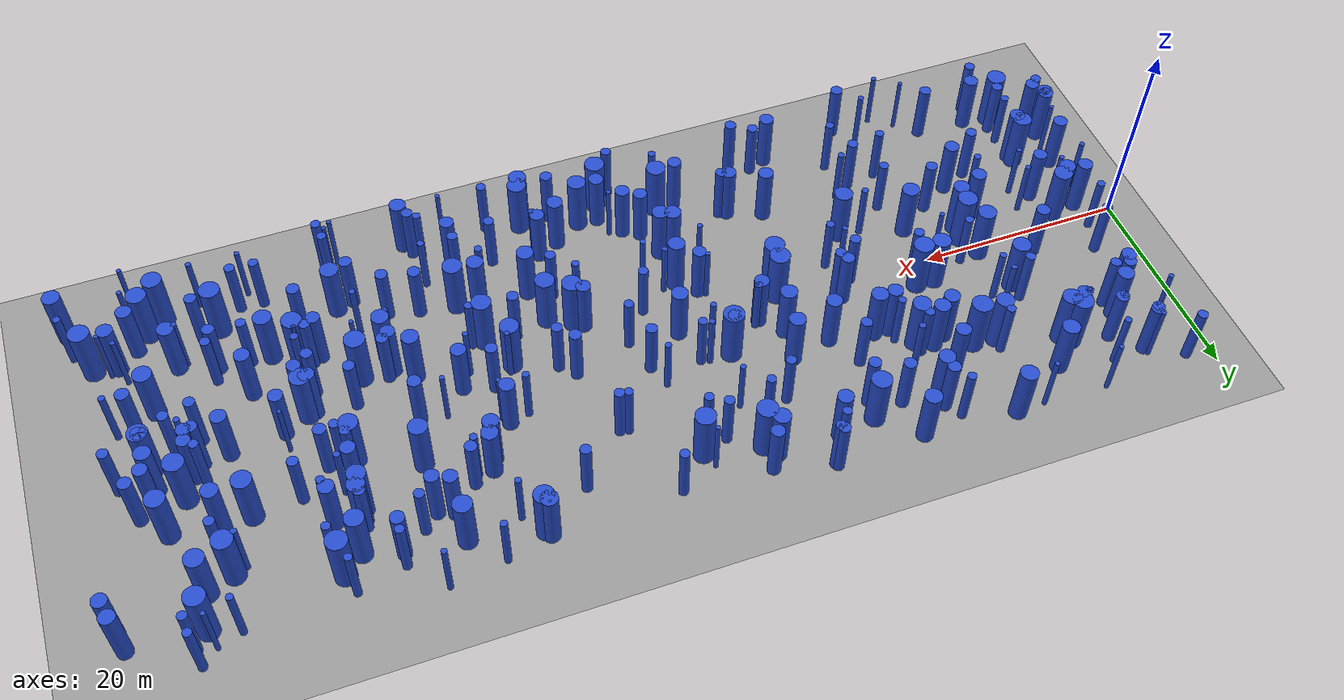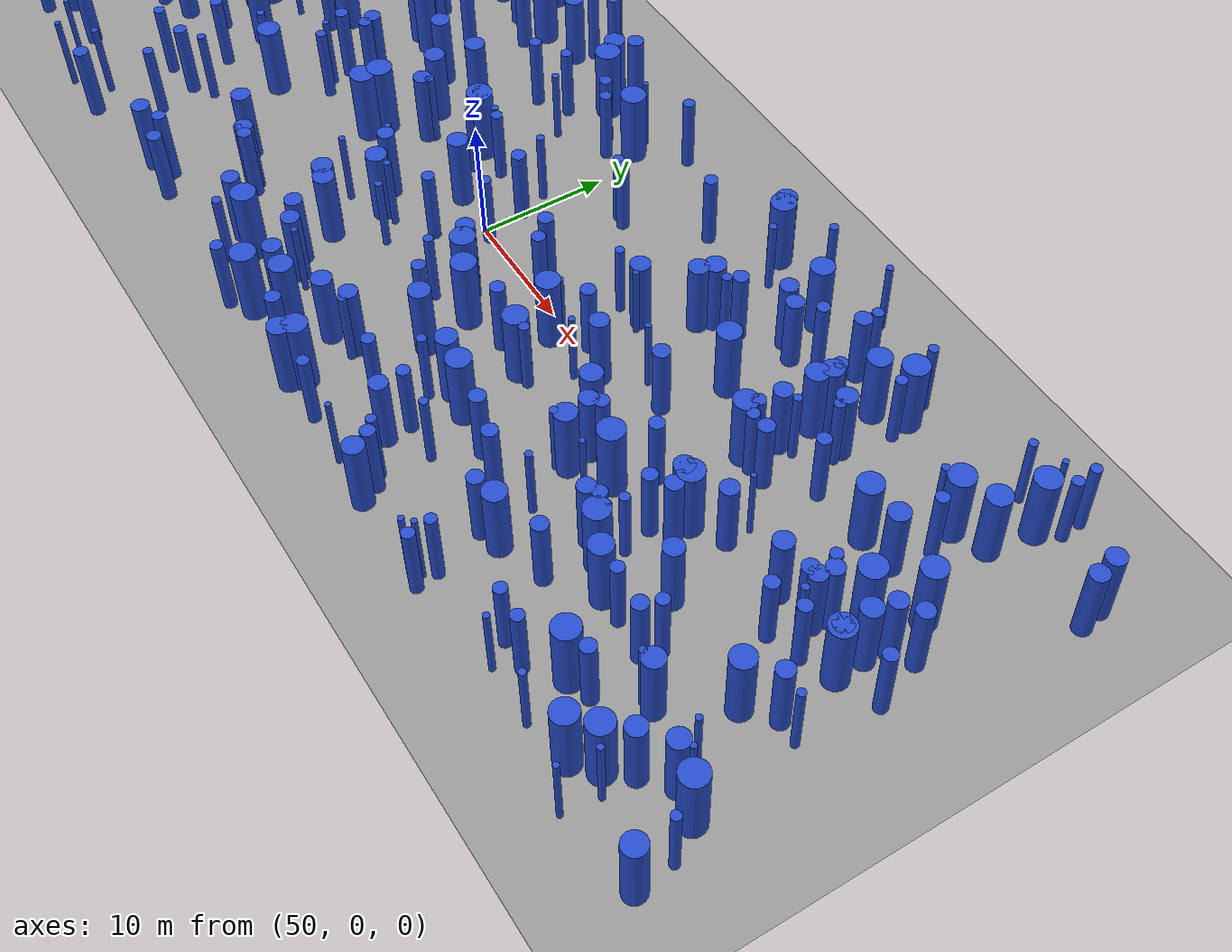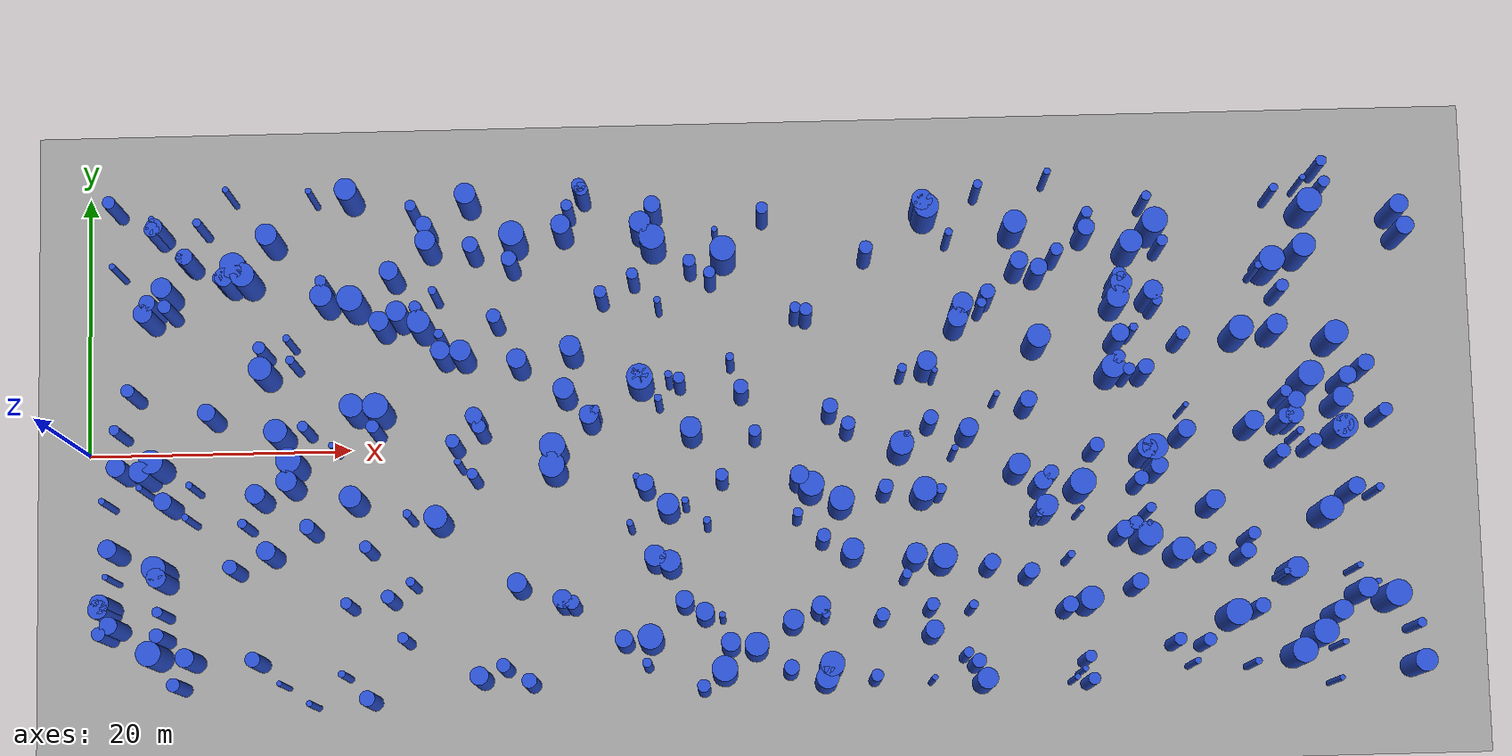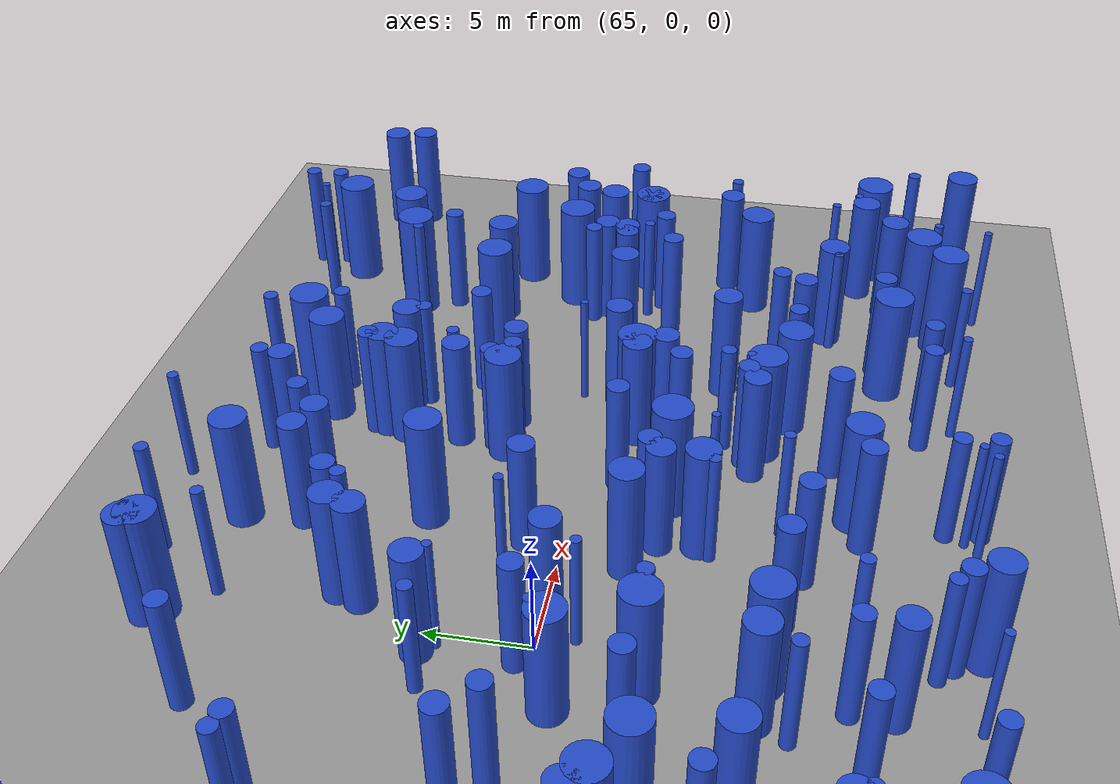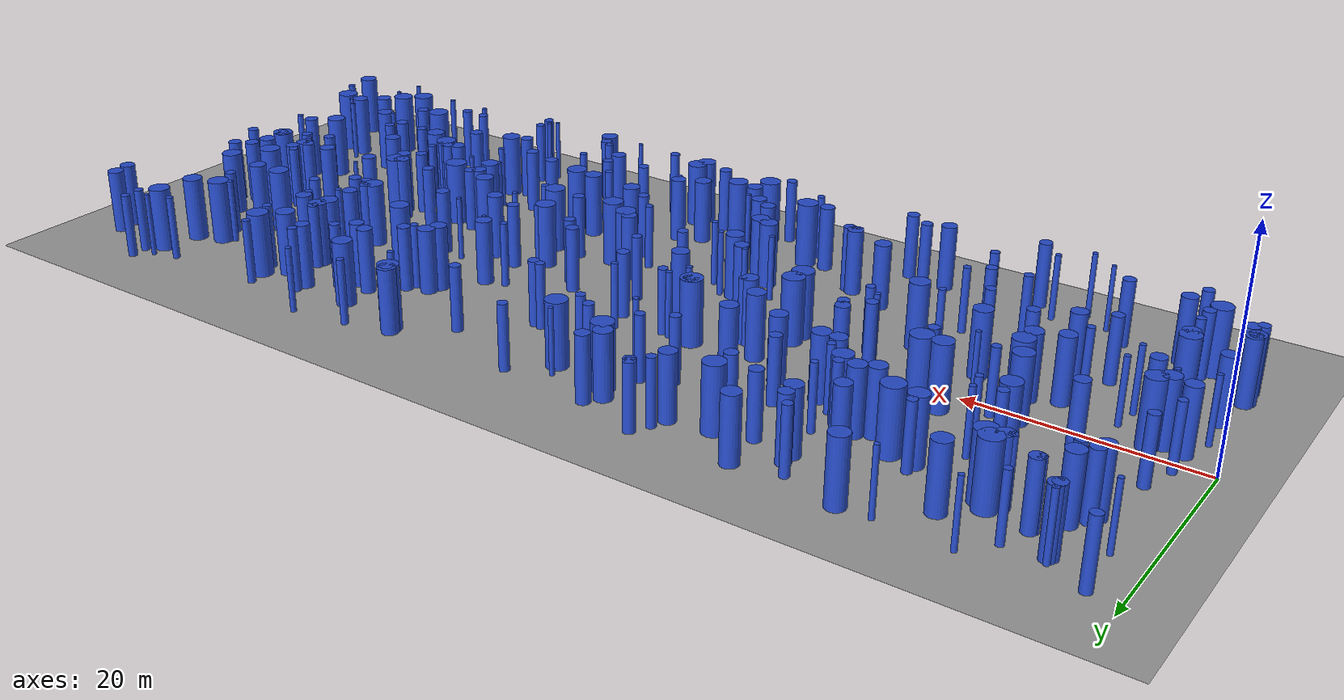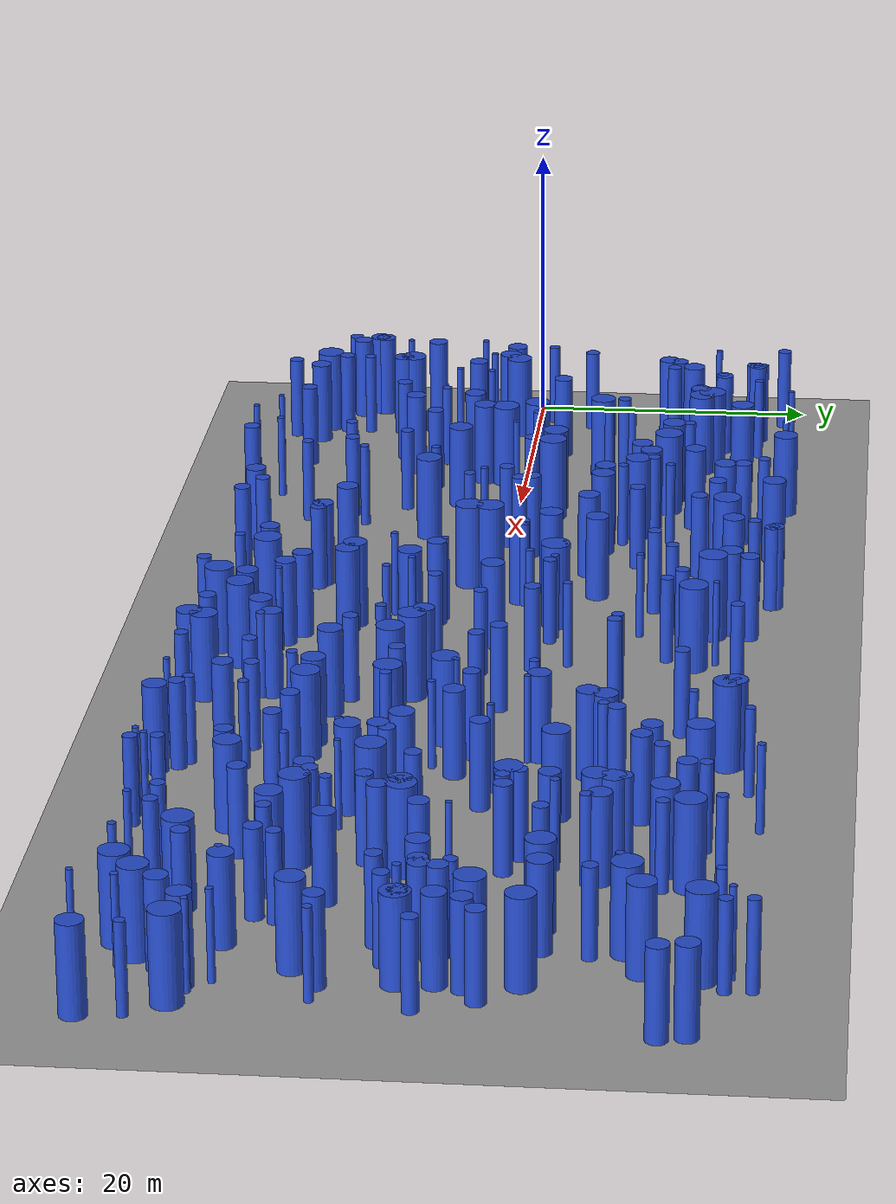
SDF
<sdf version="1.8">
 <world name="default">
  <plugin filename="gz-sim-physics-system" name="gz::sim::systems::Physics"/>
  <plugin filename="gz-sim-sensors-system" name="gz::sim::systems::Sensors">
   <render_engine>ogre2</render_engine>
  </plugin>
  <plugin filename="gz-sim-scene-broadcaster-system" name="gz::sim::systems::SceneBroadcaster"/>
  <plugin filename="gz-sim-user-commands-system" name="gz::sim::systems::UserCommands"/>
  <light name="light" type="directional">
   <pose>0 0 10 0 -0 0</pose>
   <diffuse>0.8 0.8 0.8 1</diffuse>
   <specular>0.2 0.2 0.2 1</specular>
   <attenuation>
    <range>1000</range>
    <constant>0.9</constant>
    <linear>0.01</linear>
    <quadratic>0.001</quadratic>
   </attenuation>
   <direction>-0.5 0.1 -0.9</direction>
   <spot><inner_angle>0</inner_angle><outer_angle>0</outer_angle><falloff>0</falloff></spot>
  </light>
  <gravity>0 0 -9.8</gravity>
  <magnetic_field>6e-06 2.3e-05 -4.2e-05</magnetic_field>
  <atmosphere type="adiabatic"/>
  <physics type="ode">
   <max_step_size>0.01</max_step_size>
   <real_time_factor>1</real_time_factor>
   <real_time_update_rate>100</real_time_update_rate>
  </physics>
  <scene><ambient>0.4 0.4 0.4 1</ambient><background>0.7 0.7 0.7 1</background><shadows>1</shadows></scene>
  <audio><device>default</device></audio>
  <spherical_coordinates>
   <surface_model>EARTH_WGS84</surface_model>
   <latitude_deg>0</latitude_deg>
   <longitude_deg>0</longitude_deg>
   <elevation>0</elevation>
   <heading_deg>0</heading_deg>
  </spherical_coordinates>
  <model name="ground_plane_map">
   <static>1</static>
   <link name="link">
    <collision name="collision">
     <geometry><plane><normal>0 0 1</normal><size>110 50</size></plane></geometry>
     <surface>
      <contact><collide_without_contact>1</collide_without_contact></contact>
      <friction><ode><mu>100</mu><mu2>50</mu2></ode></friction>
     </surface>
    </collision>
    <visual name="visual">
     <cast_shadows>0</cast_shadows>
     <geometry><plane><normal>0 0 1</normal><size>110 50</size></plane></geometry>
     <material>
      <script><uri>file://media/materials/scripts/gazebo.material</uri><name>Gazebo/Grey</name></script>
     </material>
    </visual>
   </link>
   <pose>51 0 0 0 -0 0</pose>
  </model>
  <model name="0">
   <static>1</static>
   <link name="link">
    <inertial>
     <mass>2</mass>
     <inertia><ixx>6.32511</ixx><ixy>0</ixy><ixz>0</ixz><iyy>6.32511</iyy><iyz>0</iyz><izz>0.650222</izz></inertia>
    </inertial>
    <collision name="collision">
     <geometry><cylinder><length>6</length><radius>0.806364</radius></cylinder></geometry>
     <surface><contact><collide_without_contact>1</collide_without_contact></contact></surface>
    </collision>
    <visual name="visual">
     <geometry><cylinder><length>6</length><radius>0.806364</radius></cylinder></geometry>
     <material>
      <script><uri>file://media/materials/scripts/gazebo.material</uri><name>Gazebo/Blue</name></script>
     </material>
    </visual>
    <gravity>0</gravity>
   </link>
   <pose>43.1853 -9.25453 3 0 -0 0</pose>
  </model>
  <model name="1">
   <static>1</static>
   <link name="link">
    <inertial>
     <mass>2</mass>
     <inertia><ixx>6.13726</ixx><ixy>0</ixy><ixz>0</ixz><iyy>6.13726</iyy><iyz>0</iyz><izz>0.274521</izz></inertia>
    </inertial>
    <collision name="collision">
     <geometry><cylinder><length>6</length><radius>0.523947</radius></cylinder></geometry>
     <surface><contact><collide_without_contact>1</collide_without_contact></contact></surface>
    </collision>
    <visual name="visual">
     <geometry><cylinder><length>6</length><radius>0.523947</radius></cylinder></geometry>
     <material>
      <script><uri>file://media/materials/scripts/gazebo.material</uri><name>Gazebo/Blue</name></script>
     </material>
    </visual>
    <gravity>0</gravity>
   </link>
   <pose>79.0825 -7.66138 3 0 -0 0</pose>
  </model>
  <model name="2">
   <static>1</static>
   <link name="link">
    <inertial>
     <mass>2</mass>
     <inertia><ixx>6.22225</ixx><ixy>0</ixy><ixz>0</ixz><iyy>6.22225</iyy><iyz>0</iyz><izz>0.444496</izz></inertia>
    </inertial>
    <collision name="collision">
     <geometry><cylinder><length>6</length><radius>0.666706</radius></cylinder></geometry>
     <surface><contact><collide_without_contact>1</collide_without_contact></contact></surface>
    </collision>
    <visual name="visual">
     <geometry><cylinder><length>6</length><radius>0.666706</radius></cylinder></geometry>
     <material>
      <script><uri>file://media/materials/scripts/gazebo.material</uri><name>Gazebo/Blue</name></script>
     </material>
    </visual>
    <gravity>0</gravity>
   </link>
   <pose>91.2671 0.181225 3 0 -0 0</pose>
  </model>
  <model name="3">
   <static>1</static>
   <link name="link">
    <inertial>
     <mass>2</mass>
     <inertia><ixx>6.32373</ixx><ixy>0</ixy><ixz>0</ixz><iyy>6.32373</iyy><iyz>0</iyz><izz>0.647451</izz></inertia>
    </inertial>
    <collision name="collision">
     <geometry><cylinder><length>6</length><radius>0.804643</radius></cylinder></geometry>
     <surface><contact><collide_without_contact>1</collide_without_contact></contact></surface>
    </collision>
    <visual name="visual">
     <geometry><cylinder><length>6</length><radius>0.804643</radius></cylinder></geometry>
     <material>
      <script><uri>file://media/materials/scripts/gazebo.material</uri><name>Gazebo/Blue</name></script>
     </material>
    </visual>
    <gravity>0</gravity>
   </link>
   <pose>62.6464 -9.57824 3 0 -0 0</pose>
  </model>
  <model name="4">
   <static>1</static>
   <link name="link">
    <inertial>
     <mass>2</mass>
     <inertia><ixx>6.48632</ixx><ixy>0</ixy><ixz>0</ixz><iyy>6.48632</iyy><iyz>0</iyz><izz>0.972646</izz></inertia>
    </inertial>
    <collision name="collision">
     <geometry><cylinder><length>6</length><radius>0.986228</radius></cylinder></geometry>
     <surface><contact><collide_without_contact>1</collide_without_contact></contact></surface>
    </collision>
    <visual name="visual">
     <geometry><cylinder><length>6</length><radius>0.986228</radius></cylinder></geometry>
     <material>
      <script><uri>file://media/materials/scripts/gazebo.material</uri><name>Gazebo/Blue</name></script>
     </material>
    </visual>
    <gravity>0</gravity>
   </link>
   <pose>81.4098 15.2934 3 0 -0 0</pose>
  </model>
  <model name="5">
   <static>1</static>
   <link name="link">
    <inertial>
     <mass>2</mass>
     <inertia><ixx>6.30722</ixx><ixy>0</ixy><ixz>0</ixz><iyy>6.30722</iyy><iyz>0</iyz><izz>0.614445</izz></inertia>
    </inertial>
    <collision name="collision">
     <geometry><cylinder><length>6</length><radius>0.783865</radius></cylinder></geometry>
     <surface><contact><collide_without_contact>1</collide_without_contact></contact></surface>
    </collision>
    <visual name="visual">
     <geometry><cylinder><length>6</length><radius>0.783865</radius></cylinder></geometry>
     <material>
      <script><uri>file://media/materials/scripts/gazebo.material</uri><name>Gazebo/Blue</name></script>
     </material>
    </visual>
    <gravity>0</gravity>
   </link>
   <pose>90.2586 7.07092 3 0 -0 0</pose>
  </model>
  <model name="6">
   <static>1</static>
   <link name="link">
    <inertial>
     <mass>2</mass>
     <inertia>
      <ixx>6.03936</ixx>
      <ixy>0</ixy>
      <ixz>0</ixz>
      <iyy>6.03936</iyy>
      <iyz>0</iyz>
      <izz>0.0787145</izz>
     </inertia>
    </inertial>
    <collision name="collision">
     <geometry><cylinder><length>6</length><radius>0.280561</radius></cylinder></geometry>
     <surface><contact><collide_without_contact>1</collide_without_contact></contact></surface>
    </collision>
    <visual name="visual">
     <geometry><cylinder><length>6</length><radius>0.280561</radius></cylinder></geometry>
     <material>
      <script><uri>file://media/materials/scripts/gazebo.material</uri><name>Gazebo/Blue</name></script>
     </material>
    </visual>
    <gravity>0</gravity>
   </link>
   <pose>44.4541 4.37326 3 0 -0 0</pose>
  </model>
  <model name="7">
   <static>1</static>
   <link name="link">
    <inertial>
     <mass>2</mass>
     <inertia><ixx>6.47364</ixx><ixy>0</ixy><ixz>0</ixz><iyy>6.47364</iyy><iyz>0</iyz><izz>0.947284</izz></inertia>
    </inertial>
    <collision name="collision">
     <geometry><cylinder><length>6</length><radius>0.973285</radius></cylinder></geometry>
     <surface><contact><collide_without_contact>1</collide_without_contact></contact></surface>
    </collision>
    <visual name="visual">
     <geometry><cylinder><length>6</length><radius>0.973285</radius></cylinder></geometry>
     <material>
      <script><uri>file://media/materials/scripts/gazebo.material</uri><name>Gazebo/Blue</name></script>
     </material>
    </visual>
    <gravity>0</gravity>
   </link>
   <pose>48.7457 13.9013 3 0 -0 0</pose>
  </model>
  <model name="8">
   <static>1</static>
   <link name="link">
    <inertial>
     <mass>2</mass>
     <inertia><ixx>6.35619</ixx><ixy>0</ixy><ixz>0</ixz><iyy>6.35619</iyy><iyz>0</iyz><izz>0.712374</izz></inertia>
    </inertial>
    <collision name="collision">
     <geometry><cylinder><length>6</length><radius>0.844022</radius></cylinder></geometry>
     <surface><contact><collide_without_contact>1</collide_without_contact></contact></surface>
    </collision>
    <visual name="visual">
     <geometry><cylinder><length>6</length><radius>0.844022</radius></cylinder></geometry>
     <material>
      <script><uri>file://media/materials/scripts/gazebo.material</uri><name>Gazebo/Blue</name></script>
     </material>
    </visual>
    <gravity>0</gravity>
   </link>
   <pose>55.7877 -18.618 3 0 -0 0</pose>
  </model>
  <model name="9">
   <static>1</static>
   <link name="link">
    <inertial>
     <mass>2</mass>
     <inertia><ixx>6.13471</ixx><ixy>0</ixy><ixz>0</ixz><iyy>6.13471</iyy><iyz>0</iyz><izz>0.269422</izz></inertia>
    </inertial>
    <collision name="collision">
     <geometry><cylinder><length>6</length><radius>0.519059</radius></cylinder></geometry>
     <surface><contact><collide_without_contact>1</collide_without_contact></contact></surface>
    </collision>
    <visual name="visual">
     <geometry><cylinder><length>6</length><radius>0.519059</radius></cylinder></geometry>
     <material>
      <script><uri>file://media/materials/scripts/gazebo.material</uri><name>Gazebo/Blue</name></script>
     </material>
    </visual>
    <gravity>0</gravity>
   </link>
   <pose>83.1473 6.55157 3 0 -0 0</pose>
  </model>
  <model name="10">
   <static>1</static>
   <link name="link">
    <inertial>
     <mass>2</mass>
     <inertia><ixx>6.17693</ixx><ixy>0</ixy><ixz>0</ixz><iyy>6.17693</iyy><iyz>0</iyz><izz>0.353861</izz></inertia>
    </inertial>
    <collision name="collision">
     <geometry><cylinder><length>6</length><radius>0.594862</radius></cylinder></geometry>
     <surface><contact><collide_without_contact>1</collide_without_contact></contact></surface>
    </collision>
    <visual name="visual">
     <geometry><cylinder><length>6</length><radius>0.594862</radius></cylinder></geometry>
     <material>
      <script><uri>file://media/materials/scripts/gazebo.material</uri><name>Gazebo/Blue</name></script>
     </material>
    </visual>
    <gravity>0</gravity>
   </link>
   <pose>87.3229 -9.93889 3 0 -0 0</pose>
  </model>
  <model name="11">
   <static>1</static>
   <link name="link">
    <inertial>
     <mass>2</mass>
     <inertia><ixx>6.40175</ixx><ixy>0</ixy><ixz>0</ixz><iyy>6.40175</iyy><iyz>0</iyz><izz>0.803492</izz></inertia>
    </inertial>
    <collision name="collision">
     <geometry><cylinder><length>6</length><radius>0.896377</radius></cylinder></geometry>
     <surface><contact><collide_without_contact>1</collide_without_contact></contact></surface>
    </collision>
    <visual name="visual">
     <geometry><cylinder><length>6</length><radius>0.896377</radius></cylinder></geometry>
     <material>
      <script><uri>file://media/materials/scripts/gazebo.material</uri><name>Gazebo/Blue</name></script>
     </material>
    </visual>
    <gravity>0</gravity>
   </link>
   <pose>20.6606 2.5794 3 0 -0 0</pose>
  </model>
  <model name="12">
   <static>1</static>
   <link name="link">
    <inertial>
     <mass>2</mass>
     <inertia><ixx>6.47437</ixx><ixy>0</ixy><ixz>0</ixz><iyy>6.47437</iyy><iyz>0</iyz><izz>0.948739</izz></inertia>
    </inertial>
    <collision name="collision">
     <geometry><cylinder><length>6</length><radius>0.974032</radius></cylinder></geometry>
     <surface><contact><collide_without_contact>1</collide_without_contact></contact></surface>
    </collision>
    <visual name="visual">
     <geometry><cylinder><length>6</length><radius>0.974032</radius></cylinder></geometry>
     <material>
      <script><uri>file://media/materials/scripts/gazebo.material</uri><name>Gazebo/Blue</name></script>
     </material>
    </visual>
    <gravity>0</gravity>
   </link>
   <pose>80.7273 -1.97986 3 0 -0 0</pose>
  </model>
  <model name="13">
   <static>1</static>
   <link name="link">
    <inertial>
     <mass>2</mass>
     <inertia><ixx>6.10399</ixx><ixy>0</ixy><ixz>0</ixz><iyy>6.10399</iyy><iyz>0</iyz><izz>0.207976</izz></inertia>
    </inertial>
    <collision name="collision">
     <geometry><cylinder><length>6</length><radius>0.456044</radius></cylinder></geometry>
     <surface><contact><collide_without_contact>1</collide_without_contact></contact></surface>
    </collision>
    <visual name="visual">
     <geometry><cylinder><length>6</length><radius>0.456044</radius></cylinder></geometry>
     <material>
      <script><uri>file://media/materials/scripts/gazebo.material</uri><name>Gazebo/Blue</name></script>
     </material>
    </visual>
    <gravity>0</gravity>
   </link>
   <pose>51.7868 16.9186 3 0 -0 0</pose>
  </model>
  <model name="14">
   <static>1</static>
   <link name="link">
    <inertial>
     <mass>2</mass>
     <inertia><ixx>6.20545</ixx><ixy>0</ixy><ixz>0</ixz><iyy>6.20545</iyy><iyz>0</iyz><izz>0.410899</izz></inertia>
    </inertial>
    <collision name="collision">
     <geometry><cylinder><length>6</length><radius>0.641014</radius></cylinder></geometry>
     <surface><contact><collide_without_contact>1</collide_without_contact></contact></surface>
    </collision>
    <visual name="visual">
     <geometry><cylinder><length>6</length><radius>0.641014</radius></cylinder></geometry>
     <material>
      <script><uri>file://media/materials/scripts/gazebo.material</uri><name>Gazebo/Blue</name></script>
     </material>
    </visual>
    <gravity>0</gravity>
   </link>
   <pose>71.3913 1.83682 3 0 -0 0</pose>
  </model>
  <model name="15">
   <static>1</static>
   <link name="link">
    <inertial>
     <mass>2</mass>
     <inertia><ixx>6.19986</ixx><ixy>0</ixy><ixz>0</ixz><iyy>6.19986</iyy><iyz>0</iyz><izz>0.399711</izz></inertia>
    </inertial>
    <collision name="collision">
     <geometry><cylinder><length>6</length><radius>0.632227</radius></cylinder></geometry>
     <surface><contact><collide_without_contact>1</collide_without_contact></contact></surface>
    </collision>
    <visual name="visual">
     <geometry><cylinder><length>6</length><radius>0.632227</radius></cylinder></geometry>
     <material>
      <script><uri>file://media/materials/scripts/gazebo.material</uri><name>Gazebo/Blue</name></script>
     </material>
    </visual>
    <gravity>0</gravity>
   </link>
   <pose>96.7974 3.99695 3 0 -0 0</pose>
  </model>
  <model name="16">
   <static>1</static>
   <link name="link">
    <inertial>
     <mass>2</mass>
     <inertia><ixx>6.15456</ixx><ixy>0</ixy><ixz>0</ixz><iyy>6.15456</iyy><iyz>0</iyz><izz>0.309126</izz></inertia>
    </inertial>
    <collision name="collision">
     <geometry><cylinder><length>6</length><radius>0.555991</radius></cylinder></geometry>
     <surface><contact><collide_without_contact>1</collide_without_contact></contact></surface>
    </collision>
    <visual name="visual">
     <geometry><cylinder><length>6</length><radius>0.555991</radius></cylinder></geometry>
     <material>
      <script><uri>file://media/materials/scripts/gazebo.material</uri><name>Gazebo/Blue</name></script>
     </material>
    </visual>
    <gravity>0</gravity>
   </link>
   <pose>60.5216 -4.47597 3 0 -0 0</pose>
  </model>
  <model name="17">
   <static>1</static>
   <link name="link">
    <inertial>
     <mass>2</mass>
     <inertia><ixx>6.09343</ixx><ixy>0</ixy><ixz>0</ixz><iyy>6.09343</iyy><iyz>0</iyz><izz>0.186852</izz></inertia>
    </inertial>
    <collision name="collision">
     <geometry><cylinder><length>6</length><radius>0.432264</radius></cylinder></geometry>
     <surface><contact><collide_without_contact>1</collide_without_contact></contact></surface>
    </collision>
    <visual name="visual">
     <geometry><cylinder><length>6</length><radius>0.432264</radius></cylinder></geometry>
     <material>
      <script><uri>file://media/materials/scripts/gazebo.material</uri><name>Gazebo/Blue</name></script>
     </material>
    </visual>
    <gravity>0</gravity>
   </link>
   <pose>20.2077 -12.26 3 0 -0 0</pose>
  </model>
  <model name="18">
   <static>1</static>
   <link name="link">
    <inertial>
     <mass>2</mass>
     <inertia><ixx>6.26305</ixx><ixy>0</ixy><ixz>0</ixz><iyy>6.26305</iyy><iyz>0</iyz><izz>0.5261</izz></inertia>
    </inertial>
    <collision name="collision">
     <geometry><cylinder><length>6</length><radius>0.725328</radius></cylinder></geometry>
     <surface><contact><collide_without_contact>1</collide_without_contact></contact></surface>
    </collision>
    <visual name="visual">
     <geometry><cylinder><length>6</length><radius>0.725328</radius></cylinder></geometry>
     <material>
      <script><uri>file://media/materials/scripts/gazebo.material</uri><name>Gazebo/Blue</name></script>
     </material>
    </visual>
    <gravity>0</gravity>
   </link>
   <pose>48.6871 -15.812 3 0 -0 0</pose>
  </model>
  <model name="19">
   <static>1</static>
   <link name="link">
    <inertial>
     <mass>2</mass>
     <inertia><ixx>6.40628</ixx><ixy>0</ixy><ixz>0</ixz><iyy>6.40628</iyy><iyz>0</iyz><izz>0.812551</izz></inertia>
    </inertial>
    <collision name="collision">
     <geometry><cylinder><length>6</length><radius>0.901416</radius></cylinder></geometry>
     <surface><contact><collide_without_contact>1</collide_without_contact></contact></surface>
    </collision>
    <visual name="visual">
     <geometry><cylinder><length>6</length><radius>0.901416</radius></cylinder></geometry>
     <material>
      <script><uri>file://media/materials/scripts/gazebo.material</uri><name>Gazebo/Blue</name></script>
     </material>
    </visual>
    <gravity>0</gravity>
   </link>
   <pose>92.5748 13.081 3 0 -0 0</pose>
  </model>
  <model name="20">
   <static>1</static>
   <link name="link">
    <inertial>
     <mass>2</mass>
     <inertia><ixx>6.44036</ixx><ixy>0</ixy><ixz>0</ixz><iyy>6.44036</iyy><iyz>0</iyz><izz>0.880718</izz></inertia>
    </inertial>
    <collision name="collision">
     <geometry><cylinder><length>6</length><radius>0.938466</radius></cylinder></geometry>
     <surface><contact><collide_without_contact>1</collide_without_contact></contact></surface>
    </collision>
    <visual name="visual">
     <geometry><cylinder><length>6</length><radius>0.938466</radius></cylinder></geometry>
     <material>
      <script><uri>file://media/materials/scripts/gazebo.material</uri><name>Gazebo/Blue</name></script>
     </material>
    </visual>
    <gravity>0</gravity>
   </link>
   <pose>54.9838 -4.14413 3 0 -0 0</pose>
  </model>
  <model name="21">
   <static>1</static>
   <link name="link">
    <inertial>
     <mass>2</mass>
     <inertia><ixx>6.08841</ixx><ixy>0</ixy><ixz>0</ixz><iyy>6.08841</iyy><iyz>0</iyz><izz>0.176826</izz></inertia>
    </inertial>
    <collision name="collision">
     <geometry><cylinder><length>6</length><radius>0.420507</radius></cylinder></geometry>
     <surface><contact><collide_without_contact>1</collide_without_contact></contact></surface>
    </collision>
    <visual name="visual">
     <geometry><cylinder><length>6</length><radius>0.420507</radius></cylinder></geometry>
     <material>
      <script><uri>file://media/materials/scripts/gazebo.material</uri><name>Gazebo/Blue</name></script>
     </material>
    </visual>
    <gravity>0</gravity>
   </link>
   <pose>81.9008 13.6855 3 0 -0 0</pose>
  </model>
  <model name="22">
   <static>1</static>
   <link name="link">
    <inertial>
     <mass>2</mass>
     <inertia><ixx>6.22569</ixx><ixy>0</ixy><ixz>0</ixz><iyy>6.22569</iyy><iyz>0</iyz><izz>0.45137</izz></inertia>
    </inertial>
    <collision name="collision">
     <geometry><cylinder><length>6</length><radius>0.671841</radius></cylinder></geometry>
     <surface><contact><collide_without_contact>1</collide_without_contact></contact></surface>
    </collision>
    <visual name="visual">
     <geometry><cylinder><length>6</length><radius>0.671841</radius></cylinder></geometry>
     <material>
      <script><uri>file://media/materials/scripts/gazebo.material</uri><name>Gazebo/Blue</name></script>
     </material>
    </visual>
    <gravity>0</gravity>
   </link>
   <pose>95.3721 3.08072 3 0 -0 0</pose>
  </model>
  <model name="23">
   <static>1</static>
   <link name="link">
    <inertial>
     <mass>2</mass>
     <inertia><ixx>6.26513</ixx><ixy>0</ixy><ixz>0</ixz><iyy>6.26513</iyy><iyz>0</iyz><izz>0.53027</izz></inertia>
    </inertial>
    <collision name="collision">
     <geometry><cylinder><length>6</length><radius>0.728196</radius></cylinder></geometry>
     <surface><contact><collide_without_contact>1</collide_without_contact></contact></surface>
    </collision>
    <visual name="visual">
     <geometry><cylinder><length>6</length><radius>0.728196</radius></cylinder></geometry>
     <material>
      <script><uri>file://media/materials/scripts/gazebo.material</uri><name>Gazebo/Blue</name></script>
     </material>
    </visual>
    <gravity>0</gravity>
   </link>
   <pose>99.903 16.0704 3 0 -0 0</pose>
  </model>
  <model name="24">
   <static>1</static>
   <link name="link">
    <inertial>
     <mass>2</mass>
     <inertia><ixx>6.03535</ixx><ixy>0</ixy><ixz>0</ixz><iyy>6.03535</iyy><iyz>0</iyz><izz>0.070702</izz></inertia>
    </inertial>
    <collision name="collision">
     <geometry><cylinder><length>6</length><radius>0.265898</radius></cylinder></geometry>
     <surface><contact><collide_without_contact>1</collide_without_contact></contact></surface>
    </collision>
    <visual name="visual">
     <geometry><cylinder><length>6</length><radius>0.265898</radius></cylinder></geometry>
     <material>
      <script><uri>file://media/materials/scripts/gazebo.material</uri><name>Gazebo/Blue</name></script>
     </material>
    </visual>
    <gravity>0</gravity>
   </link>
   <pose>62.2183 -0.535023 3 0 -0 0</pose>
  </model>
  <model name="25">
   <static>1</static>
   <link name="link">
    <inertial>
     <mass>2</mass>
     <inertia><ixx>6.38374</ixx><ixy>0</ixy><ixz>0</ixz><iyy>6.38374</iyy><iyz>0</iyz><izz>0.767485</izz></inertia>
    </inertial>
    <collision name="collision">
     <geometry><cylinder><length>6</length><radius>0.876062</radius></cylinder></geometry>
     <surface><contact><collide_without_contact>1</collide_without_contact></contact></surface>
    </collision>
    <visual name="visual">
     <geometry><cylinder><length>6</length><radius>0.876062</radius></cylinder></geometry>
     <material>
      <script><uri>file://media/materials/scripts/gazebo.material</uri><name>Gazebo/Blue</name></script>
     </material>
    </visual>
    <gravity>0</gravity>
   </link>
   <pose>25.7538 8.85397 3 0 -0 0</pose>
  </model>
  <model name="26">
   <static>1</static>
   <link name="link">
    <inertial>
     <mass>2</mass>
     <inertia><ixx>6.07083</ixx><ixy>0</ixy><ixz>0</ixz><iyy>6.07083</iyy><iyz>0</iyz><izz>0.141653</izz></inertia>
    </inertial>
    <collision name="collision">
     <geometry><cylinder><length>6</length><radius>0.376368</radius></cylinder></geometry>
     <surface><contact><collide_without_contact>1</collide_without_contact></contact></surface>
    </collision>
    <visual name="visual">
     <geometry><cylinder><length>6</length><radius>0.376368</radius></cylinder></geometry>
     <material>
      <script><uri>file://media/materials/scripts/gazebo.material</uri><name>Gazebo/Blue</name></script>
     </material>
    </visual>
    <gravity>0</gravity>
   </link>
   <pose>80.2366 -6.5725 3 0 -0 0</pose>
  </model>
  <model name="27">
   <static>1</static>
   <link name="link">
    <inertial>
     <mass>2</mass>
     <inertia>
      <ixx>6.03934</ixx>
      <ixy>0</ixy>
      <ixz>0</ixz>
      <iyy>6.03934</iyy>
      <iyz>0</iyz>
      <izz>0.0786724</izz>
     </inertia>
    </inertial>
    <collision name="collision">
     <geometry><cylinder><length>6</length><radius>0.280486</radius></cylinder></geometry>
     <surface><contact><collide_without_contact>1</collide_without_contact></contact></surface>
    </collision>
    <visual name="visual">
     <geometry><cylinder><length>6</length><radius>0.280486</radius></cylinder></geometry>
     <material>
      <script><uri>file://media/materials/scripts/gazebo.material</uri><name>Gazebo/Blue</name></script>
     </material>
    </visual>
    <gravity>0</gravity>
   </link>
   <pose>15.8342 7.79594 3 0 -0 0</pose>
  </model>
  <model name="28">
   <static>1</static>
   <link name="link">
    <inertial>
     <mass>2</mass>
     <inertia><ixx>6.2172</ixx><ixy>0</ixy><ixz>0</ixz><iyy>6.2172</iyy><iyz>0</iyz><izz>0.434403</izz></inertia>
    </inertial>
    <collision name="collision">
     <geometry><cylinder><length>6</length><radius>0.659093</radius></cylinder></geometry>
     <surface><contact><collide_without_contact>1</collide_without_contact></contact></surface>
    </collision>
    <visual name="visual">
     <geometry><cylinder><length>6</length><radius>0.659093</radius></cylinder></geometry>
     <material>
      <script><uri>file://media/materials/scripts/gazebo.material</uri><name>Gazebo/Blue</name></script>
     </material>
    </visual>
    <gravity>0</gravity>
   </link>
   <pose>91.4611 1.32284 3 0 -0 0</pose>
  </model>
  <model name="29">
   <static>1</static>
   <link name="link">
    <inertial>
     <mass>2</mass>
     <inertia><ixx>6.0245</ixx><ixy>0</ixy><ixz>0</ixz><iyy>6.0245</iyy><iyz>0</iyz><izz>0.0489991</izz></inertia>
    </inertial>
    <collision name="collision">
     <geometry><cylinder><length>6</length><radius>0.221357</radius></cylinder></geometry>
     <surface><contact><collide_without_contact>1</collide_without_contact></contact></surface>
    </collision>
    <visual name="visual">
     <geometry><cylinder><length>6</length><radius>0.221357</radius></cylinder></geometry>
     <material>
      <script><uri>file://media/materials/scripts/gazebo.material</uri><name>Gazebo/Blue</name></script>
     </material>
    </visual>
    <gravity>0</gravity>
   </link>
   <pose>64.4402 4.20646 3 0 -0 0</pose>
  </model>
  <model name="30">
   <static>1</static>
   <link name="link">
    <inertial>
     <mass>2</mass>
     <inertia><ixx>6.13157</ixx><ixy>0</ixy><ixz>0</ixz><iyy>6.13157</iyy><iyz>0</iyz><izz>0.263136</izz></inertia>
    </inertial>
    <collision name="collision">
     <geometry><cylinder><length>6</length><radius>0.512968</radius></cylinder></geometry>
     <surface><contact><collide_without_contact>1</collide_without_contact></contact></surface>
    </collision>
    <visual name="visual">
     <geometry><cylinder><length>6</length><radius>0.512968</radius></cylinder></geometry>
     <material>
      <script><uri>file://media/materials/scripts/gazebo.material</uri><name>Gazebo/Blue</name></script>
     </material>
    </visual>
    <gravity>0</gravity>
   </link>
   <pose>38.1472 18.7277 3 0 -0 0</pose>
  </model>
  <model name="31">
   <static>1</static>
   <link name="link">
    <inertial>
     <mass>2</mass>
     <inertia>
      <ixx>6.02361</ixx>
      <ixy>0</ixy>
      <ixz>0</ixz>
      <iyy>6.02361</iyy>
      <iyz>0</iyz>
      <izz>0.0472233</izz>
     </inertia>
    </inertial>
    <collision name="collision">
     <geometry><cylinder><length>6</length><radius>0.217309</radius></cylinder></geometry>
     <surface><contact><collide_without_contact>1</collide_without_contact></contact></surface>
    </collision>
    <visual name="visual">
     <geometry><cylinder><length>6</length><radius>0.217309</radius></cylinder></geometry>
     <material>
      <script><uri>file://media/materials/scripts/gazebo.material</uri><name>Gazebo/Blue</name></script>
     </material>
    </visual>
    <gravity>0</gravity>
   </link>
   <pose>96.9028 -12.4642 3 0 -0 0</pose>
  </model>
  <model name="32">
   <static>1</static>
   <link name="link">
    <inertial>
     <mass>2</mass>
     <inertia><ixx>6.06788</ixx><ixy>0</ixy><ixz>0</ixz><iyy>6.06788</iyy><iyz>0</iyz><izz>0.135764</izz></inertia>
    </inertial>
    <collision name="collision">
     <geometry><cylinder><length>6</length><radius>0.368461</radius></cylinder></geometry>
     <surface><contact><collide_without_contact>1</collide_without_contact></contact></surface>
    </collision>
    <visual name="visual">
     <geometry><cylinder><length>6</length><radius>0.368461</radius></cylinder></geometry>
     <material>
      <script><uri>file://media/materials/scripts/gazebo.material</uri><name>Gazebo/Blue</name></script>
     </material>
    </visual>
    <gravity>0</gravity>
   </link>
   <pose>80.853 17.1568 3 0 -0 0</pose>
  </model>
  <model name="33">
   <static>1</static>
   <link name="link">
    <inertial>
     <mass>2</mass>
     <inertia><ixx>6.14607</ixx><ixy>0</ixy><ixz>0</ixz><iyy>6.14607</iyy><iyz>0</iyz><izz>0.292135</izz></inertia>
    </inertial>
    <collision name="collision">
     <geometry><cylinder><length>6</length><radius>0.540495</radius></cylinder></geometry>
     <surface><contact><collide_without_contact>1</collide_without_contact></contact></surface>
    </collision>
    <visual name="visual">
     <geometry><cylinder><length>6</length><radius>0.540495</radius></cylinder></geometry>
     <material>
      <script><uri>file://media/materials/scripts/gazebo.material</uri><name>Gazebo/Blue</name></script>
     </material>
    </visual>
    <gravity>0</gravity>
   </link>
   <pose>11.5808 -9.34368 3 0 -0 0</pose>
  </model>
  <model name="34">
   <static>1</static>
   <link name="link">
    <inertial>
     <mass>2</mass>
     <inertia><ixx>6.25743</ixx><ixy>0</ixy><ixz>0</ixz><iyy>6.25743</iyy><iyz>0</iyz><izz>0.514864</izz></inertia>
    </inertial>
    <collision name="collision">
     <geometry><cylinder><length>6</length><radius>0.717541</radius></cylinder></geometry>
     <surface><contact><collide_without_contact>1</collide_without_contact></contact></surface>
    </collision>
    <visual name="visual">
     <geometry><cylinder><length>6</length><radius>0.717541</radius></cylinder></geometry>
     <material>
      <script><uri>file://media/materials/scripts/gazebo.material</uri><name>Gazebo/Blue</name></script>
     </material>
    </visual>
    <gravity>0</gravity>
   </link>
   <pose>36.2442 -12.3285 3 0 -0 0</pose>
  </model>
  <model name="35">
   <static>1</static>
   <link name="link">
    <inertial>
     <mass>2</mass>
     <inertia><ixx>6.0268</ixx><ixy>0</ixy><ixz>0</ixz><iyy>6.0268</iyy><iyz>0</iyz><izz>0.0535936</izz></inertia>
    </inertial>
    <collision name="collision">
     <geometry><cylinder><length>6</length><radius>0.231503</radius></cylinder></geometry>
     <surface><contact><collide_without_contact>1</collide_without_contact></contact></surface>
    </collision>
    <visual name="visual">
     <geometry><cylinder><length>6</length><radius>0.231503</radius></cylinder></geometry>
     <material>
      <script><uri>file://media/materials/scripts/gazebo.material</uri><name>Gazebo/Blue</name></script>
     </material>
    </visual>
    <gravity>0</gravity>
   </link>
   <pose>11.2769 19.3033 3 0 -0 0</pose>
  </model>
  <model name="36">
   <static>1</static>
   <link name="link">
    <inertial>
     <mass>2</mass>
     <inertia><ixx>6.11851</ixx><ixy>0</ixy><ixz>0</ixz><iyy>6.11851</iyy><iyz>0</iyz><izz>0.237017</izz></inertia>
    </inertial>
    <collision name="collision">
     <geometry><cylinder><length>6</length><radius>0.486844</radius></cylinder></geometry>
     <surface><contact><collide_without_contact>1</collide_without_contact></contact></surface>
    </collision>
    <visual name="visual">
     <geometry><cylinder><length>6</length><radius>0.486844</radius></cylinder></geometry>
     <material>
      <script><uri>file://media/materials/scripts/gazebo.material</uri><name>Gazebo/Blue</name></script>
     </material>
    </visual>
    <gravity>0</gravity>
   </link>
   <pose>73.9343 13.2036 3 0 -0 0</pose>
  </model>
  <model name="37">
   <static>1</static>
   <link name="link">
    <inertial>
     <mass>2</mass>
     <inertia><ixx>6.05629</ixx><ixy>0</ixy><ixz>0</ixz><iyy>6.05629</iyy><iyz>0</iyz><izz>0.112587</izz></inertia>
    </inertial>
    <collision name="collision">
     <geometry><cylinder><length>6</length><radius>0.33554</radius></cylinder></geometry>
     <surface><contact><collide_without_contact>1</collide_without_contact></contact></surface>
    </collision>
    <visual name="visual">
     <geometry><cylinder><length>6</length><radius>0.33554</radius></cylinder></geometry>
     <material>
      <script><uri>file://media/materials/scripts/gazebo.material</uri><name>Gazebo/Blue</name></script>
     </material>
    </visual>
    <gravity>0</gravity>
   </link>
   <pose>68.1482 18.3489 3 0 -0 0</pose>
  </model>
  <model name="38">
   <static>1</static>
   <link name="link">
    <inertial>
     <mass>2</mass>
     <inertia><ixx>6.27451</ixx><ixy>0</ixy><ixz>0</ixz><iyy>6.27451</iyy><iyz>0</iyz><izz>0.549024</izz></inertia>
    </inertial>
    <collision name="collision">
     <geometry><cylinder><length>6</length><radius>0.740961</radius></cylinder></geometry>
     <surface><contact><collide_without_contact>1</collide_without_contact></contact></surface>
    </collision>
    <visual name="visual">
     <geometry><cylinder><length>6</length><radius>0.740961</radius></cylinder></geometry>
     <material>
      <script><uri>file://media/materials/scripts/gazebo.material</uri><name>Gazebo/Blue</name></script>
     </material>
    </visual>
    <gravity>0</gravity>
   </link>
   <pose>85.0306 -6.07382 3 0 -0 0</pose>
  </model>
  <model name="39">
   <static>1</static>
   <link name="link">
    <inertial>
     <mass>2</mass>
     <inertia><ixx>6.22946</ixx><ixy>0</ixy><ixz>0</ixz><iyy>6.22946</iyy><iyz>0</iyz><izz>0.458916</izz></inertia>
    </inertial>
    <collision name="collision">
     <geometry><cylinder><length>6</length><radius>0.677433</radius></cylinder></geometry>
     <surface><contact><collide_without_contact>1</collide_without_contact></contact></surface>
    </collision>
    <visual name="visual">
     <geometry><cylinder><length>6</length><radius>0.677433</radius></cylinder></geometry>
     <material>
      <script><uri>file://media/materials/scripts/gazebo.material</uri><name>Gazebo/Blue</name></script>
     </material>
    </visual>
    <gravity>0</gravity>
   </link>
   <pose>45.3096 -12.5666 3 0 -0 0</pose>
  </model>
  <model name="40">
   <static>1</static>
   <link name="link">
    <inertial>
     <mass>2</mass>
     <inertia><ixx>6.13935</ixx><ixy>0</ixy><ixz>0</ixz><iyy>6.13935</iyy><iyz>0</iyz><izz>0.278704</izz></inertia>
    </inertial>
    <collision name="collision">
     <geometry><cylinder><length>6</length><radius>0.527924</radius></cylinder></geometry>
     <surface><contact><collide_without_contact>1</collide_without_contact></contact></surface>
    </collision>
    <visual name="visual">
     <geometry><cylinder><length>6</length><radius>0.527924</radius></cylinder></geometry>
     <material>
      <script><uri>file://media/materials/scripts/gazebo.material</uri><name>Gazebo/Blue</name></script>
     </material>
    </visual>
    <gravity>0</gravity>
   </link>
   <pose>57.8383 0.334925 3 0 -0 0</pose>
  </model>
  <model name="41">
   <static>1</static>
   <link name="link">
    <inertial>
     <mass>2</mass>
     <inertia><ixx>6.11796</ixx><ixy>0</ixy><ixz>0</ixz><iyy>6.11796</iyy><iyz>0</iyz><izz>0.235925</izz></inertia>
    </inertial>
    <collision name="collision">
     <geometry><cylinder><length>6</length><radius>0.485721</radius></cylinder></geometry>
     <surface><contact><collide_without_contact>1</collide_without_contact></contact></surface>
    </collision>
    <visual name="visual">
     <geometry><cylinder><length>6</length><radius>0.485721</radius></cylinder></geometry>
     <material>
      <script><uri>file://media/materials/scripts/gazebo.material</uri><name>Gazebo/Blue</name></script>
     </material>
    </visual>
    <gravity>0</gravity>
   </link>
   <pose>84.4381 -9.72074 3 0 -0 0</pose>
  </model>
  <model name="42">
   <static>1</static>
   <link name="link">
    <inertial>
     <mass>2</mass>
     <inertia>
      <ixx>6.02204</ixx>
      <ixy>0</ixy>
      <ixz>0</ixz>
      <iyy>6.02204</iyy>
      <iyz>0</iyz>
      <izz>0.0440786</izz>
     </inertia>
    </inertial>
    <collision name="collision">
     <geometry><cylinder><length>6</length><radius>0.209949</radius></cylinder></geometry>
     <surface><contact><collide_without_contact>1</collide_without_contact></contact></surface>
    </collision>
    <visual name="visual">
     <geometry><cylinder><length>6</length><radius>0.209949</radius></cylinder></geometry>
     <material>
      <script><uri>file://media/materials/scripts/gazebo.material</uri><name>Gazebo/Blue</name></script>
     </material>
    </visual>
    <gravity>0</gravity>
   </link>
   <pose>75.056 -6.49444 3 0 -0 0</pose>
  </model>
  <model name="43">
   <static>1</static>
   <link name="link">
    <inertial>
     <mass>2</mass>
     <inertia><ixx>6.09019</ixx><ixy>0</ixy><ixz>0</ixz><iyy>6.09019</iyy><iyz>0</iyz><izz>0.180376</izz></inertia>
    </inertial>
    <collision name="collision">
     <geometry><cylinder><length>6</length><radius>0.424707</radius></cylinder></geometry>
     <surface><contact><collide_without_contact>1</collide_without_contact></contact></surface>
    </collision>
    <visual name="visual">
     <geometry><cylinder><length>6</length><radius>0.424707</radius></cylinder></geometry>
     <material>
      <script><uri>file://media/materials/scripts/gazebo.material</uri><name>Gazebo/Blue</name></script>
     </material>
    </visual>
    <gravity>0</gravity>
   </link>
   <pose>25.2338 17.7403 3 0 -0 0</pose>
  </model>
  <model name="44">
   <static>1</static>
   <link name="link">
    <inertial>
     <mass>2</mass>
     <inertia><ixx>6.09258</ixx><ixy>0</ixy><ixz>0</ixz><iyy>6.09258</iyy><iyz>0</iyz><izz>0.18516</izz></inertia>
    </inertial>
    <collision name="collision">
     <geometry><cylinder><length>6</length><radius>0.430302</radius></cylinder></geometry>
     <surface><contact><collide_without_contact>1</collide_without_contact></contact></surface>
    </collision>
    <visual name="visual">
     <geometry><cylinder><length>6</length><radius>0.430302</radius></cylinder></geometry>
     <material>
      <script><uri>file://media/materials/scripts/gazebo.material</uri><name>Gazebo/Blue</name></script>
     </material>
    </visual>
    <gravity>0</gravity>
   </link>
   <pose>37.0413 17.4916 3 0 -0 0</pose>
  </model>
  <model name="45">
   <static>1</static>
   <link name="link">
    <inertial>
     <mass>2</mass>
     <inertia><ixx>6.24281</ixx><ixy>0</ixy><ixz>0</ixz><iyy>6.24281</iyy><iyz>0</iyz><izz>0.485616</izz></inertia>
    </inertial>
    <collision name="collision">
     <geometry><cylinder><length>6</length><radius>0.696861</radius></cylinder></geometry>
     <surface><contact><collide_without_contact>1</collide_without_contact></contact></surface>
    </collision>
    <visual name="visual">
     <geometry><cylinder><length>6</length><radius>0.696861</radius></cylinder></geometry>
     <material>
      <script><uri>file://media/materials/scripts/gazebo.material</uri><name>Gazebo/Blue</name></script>
     </material>
    </visual>
    <gravity>0</gravity>
   </link>
   <pose>72.2614 -4.32324 3 0 -0 0</pose>
  </model>
  <model name="46">
   <static>1</static>
   <link name="link">
    <inertial>
     <mass>2</mass>
     <inertia><ixx>6.25968</ixx><ixy>0</ixy><ixz>0</ixz><iyy>6.25968</iyy><iyz>0</iyz><izz>0.51936</izz></inertia>
    </inertial>
    <collision name="collision">
     <geometry><cylinder><length>6</length><radius>0.720666</radius></cylinder></geometry>
     <surface><contact><collide_without_contact>1</collide_without_contact></contact></surface>
    </collision>
    <visual name="visual">
     <geometry><cylinder><length>6</length><radius>0.720666</radius></cylinder></geometry>
     <material>
      <script><uri>file://media/materials/scripts/gazebo.material</uri><name>Gazebo/Blue</name></script>
     </material>
    </visual>
    <gravity>0</gravity>
   </link>
   <pose>1.87089 -11.8641 3 0 -0 0</pose>
  </model>
  <model name="47">
   <static>1</static>
   <link name="link">
    <inertial>
     <mass>2</mass>
     <inertia><ixx>6.07665</ixx><ixy>0</ixy><ixz>0</ixz><iyy>6.07665</iyy><iyz>0</iyz><izz>0.153298</izz></inertia>
    </inertial>
    <collision name="collision">
     <geometry><cylinder><length>6</length><radius>0.391533</radius></cylinder></geometry>
     <surface><contact><collide_without_contact>1</collide_without_contact></contact></surface>
    </collision>
    <visual name="visual">
     <geometry><cylinder><length>6</length><radius>0.391533</radius></cylinder></geometry>
     <material>
      <script><uri>file://media/materials/scripts/gazebo.material</uri><name>Gazebo/Blue</name></script>
     </material>
    </visual>
    <gravity>0</gravity>
   </link>
   <pose>64.6323 -4.75905 3 0 -0 0</pose>
  </model>
  <model name="48">
   <static>1</static>
   <link name="link">
    <inertial>
     <mass>2</mass>
     <inertia><ixx>6.2142</ixx><ixy>0</ixy><ixz>0</ixz><iyy>6.2142</iyy><iyz>0</iyz><izz>0.428398</izz></inertia>
    </inertial>
    <collision name="collision">
     <geometry><cylinder><length>6</length><radius>0.654521</radius></cylinder></geometry>
     <surface><contact><collide_without_contact>1</collide_without_contact></contact></surface>
    </collision>
    <visual name="visual">
     <geometry><cylinder><length>6</length><radius>0.654521</radius></cylinder></geometry>
     <material>
      <script><uri>file://media/materials/scripts/gazebo.material</uri><name>Gazebo/Blue</name></script>
     </material>
    </visual>
    <gravity>0</gravity>
   </link>
   <pose>42.5527 -3.78138 3 0 -0 0</pose>
  </model>
  <model name="49">
   <static>1</static>
   <link name="link">
    <inertial>
     <mass>2</mass>
     <inertia><ixx>6.14289</ixx><ixy>0</ixy><ixz>0</ixz><iyy>6.14289</iyy><iyz>0</iyz><izz>0.285777</izz></inertia>
    </inertial>
    <collision name="collision">
     <geometry><cylinder><length>6</length><radius>0.534581</radius></cylinder></geometry>
     <surface><contact><collide_without_contact>1</collide_without_contact></contact></surface>
    </collision>
    <visual name="visual">
     <geometry><cylinder><length>6</length><radius>0.534581</radius></cylinder></geometry>
     <material>
      <script><uri>file://media/materials/scripts/gazebo.material</uri><name>Gazebo/Blue</name></script>
     </material>
    </visual>
    <gravity>0</gravity>
   </link>
   <pose>67.0462 -17.6442 3 0 -0 0</pose>
  </model>
  <model name="50">
   <static>1</static>
   <link name="link">
    <inertial>
     <mass>2</mass>
     <inertia><ixx>6.08298</ixx><ixy>0</ixy><ixz>0</ixz><iyy>6.08298</iyy><iyz>0</iyz><izz>0.16596</izz></inertia>
    </inertial>
    <collision name="collision">
     <geometry><cylinder><length>6</length><radius>0.407382</radius></cylinder></geometry>
     <surface><contact><collide_without_contact>1</collide_without_contact></contact></surface>
    </collision>
    <visual name="visual">
     <geometry><cylinder><length>6</length><radius>0.407382</radius></cylinder></geometry>
     <material>
      <script><uri>file://media/materials/scripts/gazebo.material</uri><name>Gazebo/Blue</name></script>
     </material>
    </visual>
    <gravity>0</gravity>
   </link>
   <pose>17.0476 1.08046 3 0 -0 0</pose>
  </model>
  <model name="51">
   <static>1</static>
   <link name="link">
    <inertial>
     <mass>2</mass>
     <inertia><ixx>6.21068</ixx><ixy>0</ixy><ixz>0</ixz><iyy>6.21068</iyy><iyz>0</iyz><izz>0.421362</izz></inertia>
    </inertial>
    <collision name="collision">
     <geometry><cylinder><length>6</length><radius>0.649124</radius></cylinder></geometry>
     <surface><contact><collide_without_contact>1</collide_without_contact></contact></surface>
    </collision>
    <visual name="visual">
     <geometry><cylinder><length>6</length><radius>0.649124</radius></cylinder></geometry>
     <material>
      <script><uri>file://media/materials/scripts/gazebo.material</uri><name>Gazebo/Blue</name></script>
     </material>
    </visual>
    <gravity>0</gravity>
   </link>
   <pose>76.2168 14.8566 3 0 -0 0</pose>
  </model>
  <model name="52">
   <static>1</static>
   <link name="link">
    <inertial>
     <mass>2</mass>
     <inertia><ixx>6.10109</ixx><ixy>0</ixy><ixz>0</ixz><iyy>6.10109</iyy><iyz>0</iyz><izz>0.202182</izz></inertia>
    </inertial>
    <collision name="collision">
     <geometry><cylinder><length>6</length><radius>0.449647</radius></cylinder></geometry>
     <surface><contact><collide_without_contact>1</collide_without_contact></contact></surface>
    </collision>
    <visual name="visual">
     <geometry><cylinder><length>6</length><radius>0.449647</radius></cylinder></geometry>
     <material>
      <script><uri>file://media/materials/scripts/gazebo.material</uri><name>Gazebo/Blue</name></script>
     </material>
    </visual>
    <gravity>0</gravity>
   </link>
   <pose>47.719 12.0839 3 0 -0 0</pose>
  </model>
  <model name="53">
   <static>1</static>
   <link name="link">
    <inertial>
     <mass>2</mass>
     <inertia><ixx>6.36119</ixx><ixy>0</ixy><ixz>0</ixz><iyy>6.36119</iyy><iyz>0</iyz><izz>0.722384</izz></inertia>
    </inertial>
    <collision name="collision">
     <geometry><cylinder><length>6</length><radius>0.849932</radius></cylinder></geometry>
     <surface><contact><collide_without_contact>1</collide_without_contact></contact></surface>
    </collision>
    <visual name="visual">
     <geometry><cylinder><length>6</length><radius>0.849932</radius></cylinder></geometry>
     <material>
      <script><uri>file://media/materials/scripts/gazebo.material</uri><name>Gazebo/Blue</name></script>
     </material>
    </visual>
    <gravity>0</gravity>
   </link>
   <pose>20.3305 19.1279 3 0 -0 0</pose>
  </model>
  <model name="54">
   <static>1</static>
   <link name="link">
    <inertial>
     <mass>2</mass>
     <inertia>
      <ixx>6.03558</ixx>
      <ixy>0</ixy>
      <ixz>0</ixz>
      <iyy>6.03558</iyy>
      <iyz>0</iyz>
      <izz>0.0711682</izz>
     </inertia>
    </inertial>
    <collision name="collision">
     <geometry><cylinder><length>6</length><radius>0.266774</radius></cylinder></geometry>
     <surface><contact><collide_without_contact>1</collide_without_contact></contact></surface>
    </collision>
    <visual name="visual">
     <geometry><cylinder><length>6</length><radius>0.266774</radius></cylinder></geometry>
     <material>
      <script><uri>file://media/materials/scripts/gazebo.material</uri><name>Gazebo/Blue</name></script>
     </material>
    </visual>
    <gravity>0</gravity>
   </link>
   <pose>73.4351 19.2131 3 0 -0 0</pose>
  </model>
  <model name="55">
   <static>1</static>
   <link name="link">
    <inertial>
     <mass>2</mass>
     <inertia><ixx>6.27588</ixx><ixy>0</ixy><ixz>0</ixz><iyy>6.27588</iyy><iyz>0</iyz><izz>0.55177</izz></inertia>
    </inertial>
    <collision name="collision">
     <geometry><cylinder><length>6</length><radius>0.742812</radius></cylinder></geometry>
     <surface><contact><collide_without_contact>1</collide_without_contact></contact></surface>
    </collision>
    <visual name="visual">
     <geometry><cylinder><length>6</length><radius>0.742812</radius></cylinder></geometry>
     <material>
      <script><uri>file://media/materials/scripts/gazebo.material</uri><name>Gazebo/Blue</name></script>
     </material>
    </visual>
    <gravity>0</gravity>
   </link>
   <pose>32.8908 -11.0334 3 0 -0 0</pose>
  </model>
  <model name="56">
   <static>1</static>
   <link name="link">
    <inertial>
     <mass>2</mass>
     <inertia><ixx>6.02038</ixx><ixy>0</ixy><ixz>0</ixz><iyy>6.02038</iyy><iyz>0</iyz><izz>0.040758</izz></inertia>
    </inertial>
    <collision name="collision">
     <geometry><cylinder><length>6</length><radius>0.201886</radius></cylinder></geometry>
     <surface><contact><collide_without_contact>1</collide_without_contact></contact></surface>
    </collision>
    <visual name="visual">
     <geometry><cylinder><length>6</length><radius>0.201886</radius></cylinder></geometry>
     <material>
      <script><uri>file://media/materials/scripts/gazebo.material</uri><name>Gazebo/Blue</name></script>
     </material>
    </visual>
    <gravity>0</gravity>
   </link>
   <pose>83.1428 1.12239 3 0 -0 0</pose>
  </model>
  <model name="57">
   <static>1</static>
   <link name="link">
    <inertial>
     <mass>2</mass>
     <inertia>
      <ixx>6.04355</ixx>
      <ixy>0</ixy>
      <ixz>0</ixz>
      <iyy>6.04355</iyy>
      <iyz>0</iyz>
      <izz>0.0870977</izz>
     </inertia>
    </inertial>
    <collision name="collision">
     <geometry><cylinder><length>6</length><radius>0.295123</radius></cylinder></geometry>
     <surface><contact><collide_without_contact>1</collide_without_contact></contact></surface>
    </collision>
    <visual name="visual">
     <geometry><cylinder><length>6</length><radius>0.295123</radius></cylinder></geometry>
     <material>
      <script><uri>file://media/materials/scripts/gazebo.material</uri><name>Gazebo/Blue</name></script>
     </material>
    </visual>
    <gravity>0</gravity>
   </link>
   <pose>65.8384 14.7256 3 0 -0 0</pose>
  </model>
  <model name="58">
   <static>1</static>
   <link name="link">
    <inertial>
     <mass>2</mass>
     <inertia><ixx>6.48296</ixx><ixy>0</ixy><ixz>0</ixz><iyy>6.48296</iyy><iyz>0</iyz><izz>0.96592</izz></inertia>
    </inertial>
    <collision name="collision">
     <geometry><cylinder><length>6</length><radius>0.982812</radius></cylinder></geometry>
     <surface><contact><collide_without_contact>1</collide_without_contact></contact></surface>
    </collision>
    <visual name="visual">
     <geometry><cylinder><length>6</length><radius>0.982812</radius></cylinder></geometry>
     <material>
      <script><uri>file://media/materials/scripts/gazebo.material</uri><name>Gazebo/Blue</name></script>
     </material>
    </visual>
    <gravity>0</gravity>
   </link>
   <pose>11.804 13.4618 3 0 -0 0</pose>
  </model>
  <model name="59">
   <static>1</static>
   <link name="link">
    <inertial>
     <mass>2</mass>
     <inertia>
      <ixx>6.03513</ixx>
      <ixy>0</ixy>
      <ixz>0</ixz>
      <iyy>6.03513</iyy>
      <iyz>0</iyz>
      <izz>0.0702655</izz>
     </inertia>
    </inertial>
    <collision name="collision">
     <geometry><cylinder><length>6</length><radius>0.265076</radius></cylinder></geometry>
     <surface><contact><collide_without_contact>1</collide_without_contact></contact></surface>
    </collision>
    <visual name="visual">
     <geometry><cylinder><length>6</length><radius>0.265076</radius></cylinder></geometry>
     <material>
      <script><uri>file://media/materials/scripts/gazebo.material</uri><name>Gazebo/Blue</name></script>
     </material>
    </visual>
    <gravity>0</gravity>
   </link>
   <pose>28.5908 -1.85594 3 0 -0 0</pose>
  </model>
  <model name="60">
   <static>1</static>
   <link name="link">
    <inertial>
     <mass>2</mass>
     <inertia><ixx>6.39524</ixx><ixy>0</ixy><ixz>0</ixz><iyy>6.39524</iyy><iyz>0</iyz><izz>0.790477</izz></inertia>
    </inertial>
    <collision name="collision">
     <geometry><cylinder><length>6</length><radius>0.889088</radius></cylinder></geometry>
     <surface><contact><collide_without_contact>1</collide_without_contact></contact></surface>
    </collision>
    <visual name="visual">
     <geometry><cylinder><length>6</length><radius>0.889088</radius></cylinder></geometry>
     <material>
      <script><uri>file://media/materials/scripts/gazebo.material</uri><name>Gazebo/Blue</name></script>
     </material>
    </visual>
    <gravity>0</gravity>
   </link>
   <pose>14.9939 0.797519 3 0 -0 0</pose>
  </model>
  <model name="61">
   <static>1</static>
   <link name="link">
    <inertial>
     <mass>2</mass>
     <inertia><ixx>6.11407</ixx><ixy>0</ixy><ixz>0</ixz><iyy>6.11407</iyy><iyz>0</iyz><izz>0.228142</izz></inertia>
    </inertial>
    <collision name="collision">
     <geometry><cylinder><length>6</length><radius>0.477642</radius></cylinder></geometry>
     <surface><contact><collide_without_contact>1</collide_without_contact></contact></surface>
    </collision>
    <visual name="visual">
     <geometry><cylinder><length>6</length><radius>0.477642</radius></cylinder></geometry>
     <material>
      <script><uri>file://media/materials/scripts/gazebo.material</uri><name>Gazebo/Blue</name></script>
     </material>
    </visual>
    <gravity>0</gravity>
   </link>
   <pose>87.8311 -8.65193 3 0 -0 0</pose>
  </model>
  <model name="62">
   <static>1</static>
   <link name="link">
    <inertial>
     <mass>2</mass>
     <inertia>
      <ixx>6.02704</ixx>
      <ixy>0</ixy>
      <ixz>0</ixz>
      <iyy>6.02704</iyy>
      <iyz>0</iyz>
      <izz>0.0540705</izz>
     </inertia>
    </inertial>
    <collision name="collision">
     <geometry><cylinder><length>6</length><radius>0.232531</radius></cylinder></geometry>
     <surface><contact><collide_without_contact>1</collide_without_contact></contact></surface>
    </collision>
    <visual name="visual">
     <geometry><cylinder><length>6</length><radius>0.232531</radius></cylinder></geometry>
     <material>
      <script><uri>file://media/materials/scripts/gazebo.material</uri><name>Gazebo/Blue</name></script>
     </material>
    </visual>
    <gravity>0</gravity>
   </link>
   <pose>69.0155 2.30709 3 0 -0 0</pose>
  </model>
  <model name="63">
   <static>1</static>
   <link name="link">
    <inertial>
     <mass>2</mass>
     <inertia><ixx>6.45196</ixx><ixy>0</ixy><ixz>0</ixz><iyy>6.45196</iyy><iyz>0</iyz><izz>0.903928</izz></inertia>
    </inertial>
    <collision name="collision">
     <geometry><cylinder><length>6</length><radius>0.950751</radius></cylinder></geometry>
     <surface><contact><collide_without_contact>1</collide_without_contact></contact></surface>
    </collision>
    <visual name="visual">
     <geometry><cylinder><length>6</length><radius>0.950751</radius></cylinder></geometry>
     <material>
      <script><uri>file://media/materials/scripts/gazebo.material</uri><name>Gazebo/Blue</name></script>
     </material>
    </visual>
    <gravity>0</gravity>
   </link>
   <pose>91.2058 -17.4489 3 0 -0 0</pose>
  </model>
  <model name="64">
   <static>1</static>
   <link name="link">
    <inertial>
     <mass>2</mass>
     <inertia><ixx>6.28961</ixx><ixy>0</ixy><ixz>0</ixz><iyy>6.28961</iyy><iyz>0</iyz><izz>0.579212</izz></inertia>
    </inertial>
    <collision name="collision">
     <geometry><cylinder><length>6</length><radius>0.76106</radius></cylinder></geometry>
     <surface><contact><collide_without_contact>1</collide_without_contact></contact></surface>
    </collision>
    <visual name="visual">
     <geometry><cylinder><length>6</length><radius>0.76106</radius></cylinder></geometry>
     <material>
      <script><uri>file://media/materials/scripts/gazebo.material</uri><name>Gazebo/Blue</name></script>
     </material>
    </visual>
    <gravity>0</gravity>
   </link>
   <pose>66.2997 8.17107 3 0 -0 0</pose>
  </model>
  <model name="65">
   <static>1</static>
   <link name="link">
    <inertial>
     <mass>2</mass>
     <inertia><ixx>6.25355</ixx><ixy>0</ixy><ixz>0</ixz><iyy>6.25355</iyy><iyz>0</iyz><izz>0.507105</izz></inertia>
    </inertial>
    <collision name="collision">
     <geometry><cylinder><length>6</length><radius>0.712113</radius></cylinder></geometry>
     <surface><contact><collide_without_contact>1</collide_without_contact></contact></surface>
    </collision>
    <visual name="visual">
     <geometry><cylinder><length>6</length><radius>0.712113</radius></cylinder></geometry>
     <material>
      <script><uri>file://media/materials/scripts/gazebo.material</uri><name>Gazebo/Blue</name></script>
     </material>
    </visual>
    <gravity>0</gravity>
   </link>
   <pose>38.4266 1.46313 3 0 -0 0</pose>
  </model>
  <model name="66">
   <static>1</static>
   <link name="link">
    <inertial>
     <mass>2</mass>
     <inertia><ixx>6.22425</ixx><ixy>0</ixy><ixz>0</ixz><iyy>6.22425</iyy><iyz>0</iyz><izz>0.448499</izz></inertia>
    </inertial>
    <collision name="collision">
     <geometry><cylinder><length>6</length><radius>0.6697</radius></cylinder></geometry>
     <surface><contact><collide_without_contact>1</collide_without_contact></contact></surface>
    </collision>
    <visual name="visual">
     <geometry><cylinder><length>6</length><radius>0.6697</radius></cylinder></geometry>
     <material>
      <script><uri>file://media/materials/scripts/gazebo.material</uri><name>Gazebo/Blue</name></script>
     </material>
    </visual>
    <gravity>0</gravity>
   </link>
   <pose>2.54749 -13.4917 3 0 -0 0</pose>
  </model>
  <model name="67">
   <static>1</static>
   <link name="link">
    <inertial>
     <mass>2</mass>
     <inertia><ixx>6.34586</ixx><ixy>0</ixy><ixz>0</ixz><iyy>6.34586</iyy><iyz>0</iyz><izz>0.691722</izz></inertia>
    </inertial>
    <collision name="collision">
     <geometry><cylinder><length>6</length><radius>0.831699</radius></cylinder></geometry>
     <surface><contact><collide_without_contact>1</collide_without_contact></contact></surface>
    </collision>
    <visual name="visual">
     <geometry><cylinder><length>6</length><radius>0.831699</radius></cylinder></geometry>
     <material>
      <script><uri>file://media/materials/scripts/gazebo.material</uri><name>Gazebo/Blue</name></script>
     </material>
    </visual>
    <gravity>0</gravity>
   </link>
   <pose>72.4865 -6.20072 3 0 -0 0</pose>
  </model>
  <model name="68">
   <static>1</static>
   <link name="link">
    <inertial>
     <mass>2</mass>
     <inertia>
      <ixx>6.02714</ixx>
      <ixy>0</ixy>
      <ixz>0</ixz>
      <iyy>6.02714</iyy>
      <iyz>0</iyz>
      <izz>0.0542715</izz>
     </inertia>
    </inertial>
    <collision name="collision">
     <geometry><cylinder><length>6</length><radius>0.232962</radius></cylinder></geometry>
     <surface><contact><collide_without_contact>1</collide_without_contact></contact></surface>
    </collision>
    <visual name="visual">
     <geometry><cylinder><length>6</length><radius>0.232962</radius></cylinder></geometry>
     <material>
      <script><uri>file://media/materials/scripts/gazebo.material</uri><name>Gazebo/Blue</name></script>
     </material>
    </visual>
    <gravity>0</gravity>
   </link>
   <pose>17.5427 19.052 3 0 -0 0</pose>
  </model>
  <model name="69">
   <static>1</static>
   <link name="link">
    <inertial>
     <mass>2</mass>
     <inertia><ixx>6.13304</ixx><ixy>0</ixy><ixz>0</ixz><iyy>6.13304</iyy><iyz>0</iyz><izz>0.266084</izz></inertia>
    </inertial>
    <collision name="collision">
     <geometry><cylinder><length>6</length><radius>0.515834</radius></cylinder></geometry>
     <surface><contact><collide_without_contact>1</collide_without_contact></contact></surface>
    </collision>
    <visual name="visual">
     <geometry><cylinder><length>6</length><radius>0.515834</radius></cylinder></geometry>
     <material>
      <script><uri>file://media/materials/scripts/gazebo.material</uri><name>Gazebo/Blue</name></script>
     </material>
    </visual>
    <gravity>0</gravity>
   </link>
   <pose>55.7984 -8.05058 3 0 -0 0</pose>
  </model>
  <model name="70">
   <static>1</static>
   <link name="link">
    <inertial>
     <mass>2</mass>
     <inertia><ixx>6.07674</ixx><ixy>0</ixy><ixz>0</ixz><iyy>6.07674</iyy><iyz>0</iyz><izz>0.15348</izz></inertia>
    </inertial>
    <collision name="collision">
     <geometry><cylinder><length>6</length><radius>0.391765</radius></cylinder></geometry>
     <surface><contact><collide_without_contact>1</collide_without_contact></contact></surface>
    </collision>
    <visual name="visual">
     <geometry><cylinder><length>6</length><radius>0.391765</radius></cylinder></geometry>
     <material>
      <script><uri>file://media/materials/scripts/gazebo.material</uri><name>Gazebo/Blue</name></script>
     </material>
    </visual>
    <gravity>0</gravity>
   </link>
   <pose>6.17959 -12.5655 3 0 -0 0</pose>
  </model>
  <model name="71">
   <static>1</static>
   <link name="link">
    <inertial>
     <mass>2</mass>
     <inertia>
      <ixx>6.03294</ixx>
      <ixy>0</ixy>
      <ixz>0</ixz>
      <iyy>6.03294</iyy>
      <iyz>0</iyz>
      <izz>0.0658899</izz>
     </inertia>
    </inertial>
    <collision name="collision">
     <geometry><cylinder><length>6</length><radius>0.25669</radius></cylinder></geometry>
     <surface><contact><collide_without_contact>1</collide_without_contact></contact></surface>
    </collision>
    <visual name="visual">
     <geometry><cylinder><length>6</length><radius>0.25669</radius></cylinder></geometry>
     <material>
      <script><uri>file://media/materials/scripts/gazebo.material</uri><name>Gazebo/Blue</name></script>
     </material>
    </visual>
    <gravity>0</gravity>
   </link>
   <pose>41.3666 -6.77114 3 0 -0 0</pose>
  </model>
  <model name="72">
   <static>1</static>
   <link name="link">
    <inertial>
     <mass>2</mass>
     <inertia>
      <ixx>6.03907</ixx>
      <ixy>0</ixy>
      <ixz>0</ixz>
      <iyy>6.03907</iyy>
      <iyz>0</iyz>
      <izz>0.0781316</izz>
     </inertia>
    </inertial>
    <collision name="collision">
     <geometry><cylinder><length>6</length><radius>0.27952</radius></cylinder></geometry>
     <surface><contact><collide_without_contact>1</collide_without_contact></contact></surface>
    </collision>
    <visual name="visual">
     <geometry><cylinder><length>6</length><radius>0.27952</radius></cylinder></geometry>
     <material>
      <script><uri>file://media/materials/scripts/gazebo.material</uri><name>Gazebo/Blue</name></script>
     </material>
    </visual>
    <gravity>0</gravity>
   </link>
   <pose>91.6373 -1.02528 3 0 -0 0</pose>
  </model>
  <model name="73">
   <static>1</static>
   <link name="link">
    <inertial>
     <mass>2</mass>
     <inertia><ixx>6.48116</ixx><ixy>0</ixy><ixz>0</ixz><iyy>6.48116</iyy><iyz>0</iyz><izz>0.962329</izz></inertia>
    </inertial>
    <collision name="collision">
     <geometry><cylinder><length>6</length><radius>0.980984</radius></cylinder></geometry>
     <surface><contact><collide_without_contact>1</collide_without_contact></contact></surface>
    </collision>
    <visual name="visual">
     <geometry><cylinder><length>6</length><radius>0.980984</radius></cylinder></geometry>
     <material>
      <script><uri>file://media/materials/scripts/gazebo.material</uri><name>Gazebo/Blue</name></script>
     </material>
    </visual>
    <gravity>0</gravity>
   </link>
   <pose>35.6719 -0.795508 3 0 -0 0</pose>
  </model>
  <model name="74">
   <static>1</static>
   <link name="link">
    <inertial>
     <mass>2</mass>
     <inertia><ixx>6.14646</ixx><ixy>0</ixy><ixz>0</ixz><iyy>6.14646</iyy><iyz>0</iyz><izz>0.292928</izz></inertia>
    </inertial>
    <collision name="collision">
     <geometry><cylinder><length>6</length><radius>0.541228</radius></cylinder></geometry>
     <surface><contact><collide_without_contact>1</collide_without_contact></contact></surface>
    </collision>
    <visual name="visual">
     <geometry><cylinder><length>6</length><radius>0.541228</radius></cylinder></geometry>
     <material>
      <script><uri>file://media/materials/scripts/gazebo.material</uri><name>Gazebo/Blue</name></script>
     </material>
    </visual>
    <gravity>0</gravity>
   </link>
   <pose>31.4047 9.13593 3 0 -0 0</pose>
  </model>
  <model name="75">
   <static>1</static>
   <link name="link">
    <inertial>
     <mass>2</mass>
     <inertia><ixx>6.43782</ixx><ixy>0</ixy><ixz>0</ixz><iyy>6.43782</iyy><iyz>0</iyz><izz>0.87563</izz></inertia>
    </inertial>
    <collision name="collision">
     <geometry><cylinder><length>6</length><radius>0.935751</radius></cylinder></geometry>
     <surface><contact><collide_without_contact>1</collide_without_contact></contact></surface>
    </collision>
    <visual name="visual">
     <geometry><cylinder><length>6</length><radius>0.935751</radius></cylinder></geometry>
     <material>
      <script><uri>file://media/materials/scripts/gazebo.material</uri><name>Gazebo/Blue</name></script>
     </material>
    </visual>
    <gravity>0</gravity>
   </link>
   <pose>63.437 -4.74428 3 0 -0 0</pose>
  </model>
  <model name="76">
   <static>1</static>
   <link name="link">
    <inertial>
     <mass>2</mass>
     <inertia><ixx>6.25283</ixx><ixy>0</ixy><ixz>0</ixz><iyy>6.25283</iyy><iyz>0</iyz><izz>0.505667</izz></inertia>
    </inertial>
    <collision name="collision">
     <geometry><cylinder><length>6</length><radius>0.711103</radius></cylinder></geometry>
     <surface><contact><collide_without_contact>1</collide_without_contact></contact></surface>
    </collision>
    <visual name="visual">
     <geometry><cylinder><length>6</length><radius>0.711103</radius></cylinder></geometry>
     <material>
      <script><uri>file://media/materials/scripts/gazebo.material</uri><name>Gazebo/Blue</name></script>
     </material>
    </visual>
    <gravity>0</gravity>
   </link>
   <pose>8.20094 -16.0225 3 0 -0 0</pose>
  </model>
  <model name="77">
   <static>1</static>
   <link name="link">
    <inertial>
     <mass>2</mass>
     <inertia>
      <ixx>6.03098</ixx>
      <ixy>0</ixy>
      <ixz>0</ixz>
      <iyy>6.03098</iyy>
      <iyz>0</iyz>
      <izz>0.0619636</izz>
     </inertia>
    </inertial>
    <collision name="collision">
     <geometry><cylinder><length>6</length><radius>0.248925</radius></cylinder></geometry>
     <surface><contact><collide_without_contact>1</collide_without_contact></contact></surface>
    </collision>
    <visual name="visual">
     <geometry><cylinder><length>6</length><radius>0.248925</radius></cylinder></geometry>
     <material>
      <script><uri>file://media/materials/scripts/gazebo.material</uri><name>Gazebo/Blue</name></script>
     </material>
    </visual>
    <gravity>0</gravity>
   </link>
   <pose>2.03012 -4.19481 3 0 -0 0</pose>
  </model>
  <model name="78">
   <static>1</static>
   <link name="link">
    <inertial>
     <mass>2</mass>
     <inertia><ixx>6.15615</ixx><ixy>0</ixy><ixz>0</ixz><iyy>6.15615</iyy><iyz>0</iyz><izz>0.312297</izz></inertia>
    </inertial>
    <collision name="collision">
     <geometry><cylinder><length>6</length><radius>0.558835</radius></cylinder></geometry>
     <surface><contact><collide_without_contact>1</collide_without_contact></contact></surface>
    </collision>
    <visual name="visual">
     <geometry><cylinder><length>6</length><radius>0.558835</radius></cylinder></geometry>
     <material>
      <script><uri>file://media/materials/scripts/gazebo.material</uri><name>Gazebo/Blue</name></script>
     </material>
    </visual>
    <gravity>0</gravity>
   </link>
   <pose>49.8746 3.30067 3 0 -0 0</pose>
  </model>
  <model name="79">
   <static>1</static>
   <link name="link">
    <inertial>
     <mass>2</mass>
     <inertia><ixx>6.14495</ixx><ixy>0</ixy><ixz>0</ixz><iyy>6.14495</iyy><iyz>0</iyz><izz>0.289907</izz></inertia>
    </inertial>
    <collision name="collision">
     <geometry><cylinder><length>6</length><radius>0.53843</radius></cylinder></geometry>
     <surface><contact><collide_without_contact>1</collide_without_contact></contact></surface>
    </collision>
    <visual name="visual">
     <geometry><cylinder><length>6</length><radius>0.53843</radius></cylinder></geometry>
     <material>
      <script><uri>file://media/materials/scripts/gazebo.material</uri><name>Gazebo/Blue</name></script>
     </material>
    </visual>
    <gravity>0</gravity>
   </link>
   <pose>37.9749 19.0124 3 0 -0 0</pose>
  </model>
  <model name="80">
   <static>1</static>
   <link name="link">
    <inertial>
     <mass>2</mass>
     <inertia><ixx>6.33758</ixx><ixy>0</ixy><ixz>0</ixz><iyy>6.33758</iyy><iyz>0</iyz><izz>0.675158</izz></inertia>
    </inertial>
    <collision name="collision">
     <geometry><cylinder><length>6</length><radius>0.82168</radius></cylinder></geometry>
     <surface><contact><collide_without_contact>1</collide_without_contact></contact></surface>
    </collision>
    <visual name="visual">
     <geometry><cylinder><length>6</length><radius>0.82168</radius></cylinder></geometry>
     <material>
      <script><uri>file://media/materials/scripts/gazebo.material</uri><name>Gazebo/Blue</name></script>
     </material>
    </visual>
    <gravity>0</gravity>
   </link>
   <pose>44.2351 -5.42668 3 0 -0 0</pose>
  </model>
  <model name="81">
   <static>1</static>
   <link name="link">
    <inertial>
     <mass>2</mass>
     <inertia><ixx>6.39682</ixx><ixy>0</ixy><ixz>0</ixz><iyy>6.39682</iyy><iyz>0</iyz><izz>0.793637</izz></inertia>
    </inertial>
    <collision name="collision">
     <geometry><cylinder><length>6</length><radius>0.890863</radius></cylinder></geometry>
     <surface><contact><collide_without_contact>1</collide_without_contact></contact></surface>
    </collision>
    <visual name="visual">
     <geometry><cylinder><length>6</length><radius>0.890863</radius></cylinder></geometry>
     <material>
      <script><uri>file://media/materials/scripts/gazebo.material</uri><name>Gazebo/Blue</name></script>
     </material>
    </visual>
    <gravity>0</gravity>
   </link>
   <pose>70.8405 15.4024 3 0 -0 0</pose>
  </model>
  <model name="82">
   <static>1</static>
   <link name="link">
    <inertial>
     <mass>2</mass>
     <inertia><ixx>6.27494</ixx><ixy>0</ixy><ixz>0</ixz><iyy>6.27494</iyy><iyz>0</iyz><izz>0.549877</izz></inertia>
    </inertial>
    <collision name="collision">
     <geometry><cylinder><length>6</length><radius>0.741537</radius></cylinder></geometry>
     <surface><contact><collide_without_contact>1</collide_without_contact></contact></surface>
    </collision>
    <visual name="visual">
     <geometry><cylinder><length>6</length><radius>0.741537</radius></cylinder></geometry>
     <material>
      <script><uri>file://media/materials/scripts/gazebo.material</uri><name>Gazebo/Blue</name></script>
     </material>
    </visual>
    <gravity>0</gravity>
   </link>
   <pose>13.4562 -3.93051 3 0 -0 0</pose>
  </model>
  <model name="83">
   <static>1</static>
   <link name="link">
    <inertial>
     <mass>2</mass>
     <inertia><ixx>6.0273</ixx><ixy>0</ixy><ixz>0</ixz><iyy>6.0273</iyy><iyz>0</iyz><izz>0.0546069</izz></inertia>
    </inertial>
    <collision name="collision">
     <geometry><cylinder><length>6</length><radius>0.233681</radius></cylinder></geometry>
     <surface><contact><collide_without_contact>1</collide_without_contact></contact></surface>
    </collision>
    <visual name="visual">
     <geometry><cylinder><length>6</length><radius>0.233681</radius></cylinder></geometry>
     <material>
      <script><uri>file://media/materials/scripts/gazebo.material</uri><name>Gazebo/Blue</name></script>
     </material>
    </visual>
    <gravity>0</gravity>
   </link>
   <pose>95.5868 -11.2314 3 0 -0 0</pose>
  </model>
  <model name="84">
   <static>1</static>
   <link name="link">
    <inertial>
     <mass>2</mass>
     <inertia><ixx>6.06422</ixx><ixy>0</ixy><ixz>0</ixz><iyy>6.06422</iyy><iyz>0</iyz><izz>0.128433</izz></inertia>
    </inertial>
    <collision name="collision">
     <geometry><cylinder><length>6</length><radius>0.358376</radius></cylinder></geometry>
     <surface><contact><collide_without_contact>1</collide_without_contact></contact></surface>
    </collision>
    <visual name="visual">
     <geometry><cylinder><length>6</length><radius>0.358376</radius></cylinder></geometry>
     <material>
      <script><uri>file://media/materials/scripts/gazebo.material</uri><name>Gazebo/Blue</name></script>
     </material>
    </visual>
    <gravity>0</gravity>
   </link>
   <pose>38.8906 1.8224 3 0 -0 0</pose>
  </model>
  <model name="85">
   <static>1</static>
   <link name="link">
    <inertial>
     <mass>2</mass>
     <inertia><ixx>6.49099</ixx><ixy>0</ixy><ixz>0</ixz><iyy>6.49099</iyy><iyz>0</iyz><izz>0.981986</izz></inertia>
    </inertial>
    <collision name="collision">
     <geometry><cylinder><length>6</length><radius>0.990952</radius></cylinder></geometry>
     <surface><contact><collide_without_contact>1</collide_without_contact></contact></surface>
    </collision>
    <visual name="visual">
     <geometry><cylinder><length>6</length><radius>0.990952</radius></cylinder></geometry>
     <material>
      <script><uri>file://media/materials/scripts/gazebo.material</uri><name>Gazebo/Blue</name></script>
     </material>
    </visual>
    <gravity>0</gravity>
   </link>
   <pose>98.3417 -13.3671 3 0 -0 0</pose>
  </model>
  <model name="86">
   <static>1</static>
   <link name="link">
    <inertial>
     <mass>2</mass>
     <inertia><ixx>6.27673</ixx><ixy>0</ixy><ixz>0</ixz><iyy>6.27673</iyy><iyz>0</iyz><izz>0.553452</izz></inertia>
    </inertial>
    <collision name="collision">
     <geometry><cylinder><length>6</length><radius>0.743944</radius></cylinder></geometry>
     <surface><contact><collide_without_contact>1</collide_without_contact></contact></surface>
    </collision>
    <visual name="visual">
     <geometry><cylinder><length>6</length><radius>0.743944</radius></cylinder></geometry>
     <material>
      <script><uri>file://media/materials/scripts/gazebo.material</uri><name>Gazebo/Blue</name></script>
     </material>
    </visual>
    <gravity>0</gravity>
   </link>
   <pose>88.2037 -0.176928 3 0 -0 0</pose>
  </model>
  <model name="87">
   <static>1</static>
   <link name="link">
    <inertial>
     <mass>2</mass>
     <inertia><ixx>6.10487</ixx><ixy>0</ixy><ixz>0</ixz><iyy>6.10487</iyy><iyz>0</iyz><izz>0.209735</izz></inertia>
    </inertial>
    <collision name="collision">
     <geometry><cylinder><length>6</length><radius>0.457968</radius></cylinder></geometry>
     <surface><contact><collide_without_contact>1</collide_without_contact></contact></surface>
    </collision>
    <visual name="visual">
     <geometry><cylinder><length>6</length><radius>0.457968</radius></cylinder></geometry>
     <material>
      <script><uri>file://media/materials/scripts/gazebo.material</uri><name>Gazebo/Blue</name></script>
     </material>
    </visual>
    <gravity>0</gravity>
   </link>
   <pose>50.8455 -0.052897 3 0 -0 0</pose>
  </model>
  <model name="88">
   <static>1</static>
   <link name="link">
    <inertial>
     <mass>2</mass>
     <inertia><ixx>6.06537</ixx><ixy>0</ixy><ixz>0</ixz><iyy>6.06537</iyy><iyz>0</iyz><izz>0.13075</izz></inertia>
    </inertial>
    <collision name="collision">
     <geometry><cylinder><length>6</length><radius>0.361593</radius></cylinder></geometry>
     <surface><contact><collide_without_contact>1</collide_without_contact></contact></surface>
    </collision>
    <visual name="visual">
     <geometry><cylinder><length>6</length><radius>0.361593</radius></cylinder></geometry>
     <material>
      <script><uri>file://media/materials/scripts/gazebo.material</uri><name>Gazebo/Blue</name></script>
     </material>
    </visual>
    <gravity>0</gravity>
   </link>
   <pose>61.8977 -11.0457 3 0 -0 0</pose>
  </model>
  <model name="89">
   <static>1</static>
   <link name="link">
    <inertial>
     <mass>2</mass>
     <inertia><ixx>6.4705</ixx><ixy>0</ixy><ixz>0</ixz><iyy>6.4705</iyy><iyz>0</iyz><izz>0.941003</izz></inertia>
    </inertial>
    <collision name="collision">
     <geometry><cylinder><length>6</length><radius>0.970053</radius></cylinder></geometry>
     <surface><contact><collide_without_contact>1</collide_without_contact></contact></surface>
    </collision>
    <visual name="visual">
     <geometry><cylinder><length>6</length><radius>0.970053</radius></cylinder></geometry>
     <material>
      <script><uri>file://media/materials/scripts/gazebo.material</uri><name>Gazebo/Blue</name></script>
     </material>
    </visual>
    <gravity>0</gravity>
   </link>
   <pose>90.1267 12.1076 3 0 -0 0</pose>
  </model>
  <model name="90">
   <static>1</static>
   <link name="link">
    <inertial>
     <mass>2</mass>
     <inertia><ixx>6.05078</ixx><ixy>0</ixy><ixz>0</ixz><iyy>6.05078</iyy><iyz>0</iyz><izz>0.101566</izz></inertia>
    </inertial>
    <collision name="collision">
     <geometry><cylinder><length>6</length><radius>0.318694</radius></cylinder></geometry>
     <surface><contact><collide_without_contact>1</collide_without_contact></contact></surface>
    </collision>
    <visual name="visual">
     <geometry><cylinder><length>6</length><radius>0.318694</radius></cylinder></geometry>
     <material>
      <script><uri>file://media/materials/scripts/gazebo.material</uri><name>Gazebo/Blue</name></script>
     </material>
    </visual>
    <gravity>0</gravity>
   </link>
   <pose>26.8432 11.1855 3 0 -0 0</pose>
  </model>
  <model name="91">
   <static>1</static>
   <link name="link">
    <inertial>
     <mass>2</mass>
     <inertia><ixx>6.22202</ixx><ixy>0</ixy><ixz>0</ixz><iyy>6.22202</iyy><iyz>0</iyz><izz>0.444034</izz></inertia>
    </inertial>
    <collision name="collision">
     <geometry><cylinder><length>6</length><radius>0.666359</radius></cylinder></geometry>
     <surface><contact><collide_without_contact>1</collide_without_contact></contact></surface>
    </collision>
    <visual name="visual">
     <geometry><cylinder><length>6</length><radius>0.666359</radius></cylinder></geometry>
     <material>
      <script><uri>file://media/materials/scripts/gazebo.material</uri><name>Gazebo/Blue</name></script>
     </material>
    </visual>
    <gravity>0</gravity>
   </link>
   <pose>72.5225 11.873 3 0 -0 0</pose>
  </model>
  <model name="92">
   <static>1</static>
   <link name="link">
    <inertial>
     <mass>2</mass>
     <inertia>
      <ixx>6.03584</ixx>
      <ixy>0</ixy>
      <ixz>0</ixz>
      <iyy>6.03584</iyy>
      <iyz>0</iyz>
      <izz>0.0716711</izz>
     </inertia>
    </inertial>
    <collision name="collision">
     <geometry><cylinder><length>6</length><radius>0.267715</radius></cylinder></geometry>
     <surface><contact><collide_without_contact>1</collide_without_contact></contact></surface>
    </collision>
    <visual name="visual">
     <geometry><cylinder><length>6</length><radius>0.267715</radius></cylinder></geometry>
     <material>
      <script><uri>file://media/materials/scripts/gazebo.material</uri><name>Gazebo/Blue</name></script>
     </material>
    </visual>
    <gravity>0</gravity>
   </link>
   <pose>87.692 -18.1768 3 0 -0 0</pose>
  </model>
  <model name="93">
   <static>1</static>
   <link name="link">
    <inertial>
     <mass>2</mass>
     <inertia>
      <ixx>6.02703</ixx>
      <ixy>0</ixy>
      <ixz>0</ixz>
      <iyy>6.02703</iyy>
      <iyz>0</iyz>
      <izz>0.0540589</izz>
     </inertia>
    </inertial>
    <collision name="collision">
     <geometry><cylinder><length>6</length><radius>0.232506</radius></cylinder></geometry>
     <surface><contact><collide_without_contact>1</collide_without_contact></contact></surface>
    </collision>
    <visual name="visual">
     <geometry><cylinder><length>6</length><radius>0.232506</radius></cylinder></geometry>
     <material>
      <script><uri>file://media/materials/scripts/gazebo.material</uri><name>Gazebo/Blue</name></script>
     </material>
    </visual>
    <gravity>0</gravity>
   </link>
   <pose>2.75391 13.5982 3 0 -0 0</pose>
  </model>
  <model name="94">
   <static>1</static>
   <link name="link">
    <inertial>
     <mass>2</mass>
     <inertia><ixx>6.05397</ixx><ixy>0</ixy><ixz>0</ixz><iyy>6.05397</iyy><iyz>0</iyz><izz>0.107946</izz></inertia>
    </inertial>
    <collision name="collision">
     <geometry><cylinder><length>6</length><radius>0.328552</radius></cylinder></geometry>
     <surface><contact><collide_without_contact>1</collide_without_contact></contact></surface>
    </collision>
    <visual name="visual">
     <geometry><cylinder><length>6</length><radius>0.328552</radius></cylinder></geometry>
     <material>
      <script><uri>file://media/materials/scripts/gazebo.material</uri><name>Gazebo/Blue</name></script>
     </material>
    </visual>
    <gravity>0</gravity>
   </link>
   <pose>16.1127 6.14078 3 0 -0 0</pose>
  </model>
  <model name="95">
   <static>1</static>
   <link name="link">
    <inertial>
     <mass>2</mass>
     <inertia><ixx>6.18241</ixx><ixy>0</ixy><ixz>0</ixz><iyy>6.18241</iyy><iyz>0</iyz><izz>0.364816</izz></inertia>
    </inertial>
    <collision name="collision">
     <geometry><cylinder><length>6</length><radius>0.604</radius></cylinder></geometry>
     <surface><contact><collide_without_contact>1</collide_without_contact></contact></surface>
    </collision>
    <visual name="visual">
     <geometry><cylinder><length>6</length><radius>0.604</radius></cylinder></geometry>
     <material>
      <script><uri>file://media/materials/scripts/gazebo.material</uri><name>Gazebo/Blue</name></script>
     </material>
    </visual>
    <gravity>0</gravity>
   </link>
   <pose>90.6245 0.09421 3 0 -0 0</pose>
  </model>
  <model name="96">
   <static>1</static>
   <link name="link">
    <inertial>
     <mass>2</mass>
     <inertia><ixx>6.27592</ixx><ixy>0</ixy><ixz>0</ixz><iyy>6.27592</iyy><iyz>0</iyz><izz>0.551837</izz></inertia>
    </inertial>
    <collision name="collision">
     <geometry><cylinder><length>6</length><radius>0.742857</radius></cylinder></geometry>
     <surface><contact><collide_without_contact>1</collide_without_contact></contact></surface>
    </collision>
    <visual name="visual">
     <geometry><cylinder><length>6</length><radius>0.742857</radius></cylinder></geometry>
     <material>
      <script><uri>file://media/materials/scripts/gazebo.material</uri><name>Gazebo/Blue</name></script>
     </material>
    </visual>
    <gravity>0</gravity>
   </link>
   <pose>81.0577 9.93077 3 0 -0 0</pose>
  </model>
  <model name="97">
   <static>1</static>
   <link name="link">
    <inertial>
     <mass>2</mass>
     <inertia><ixx>6.31806</ixx><ixy>0</ixy><ixz>0</ixz><iyy>6.31806</iyy><iyz>0</iyz><izz>0.636122</izz></inertia>
    </inertial>
    <collision name="collision">
     <geometry><cylinder><length>6</length><radius>0.797572</radius></cylinder></geometry>
     <surface><contact><collide_without_contact>1</collide_without_contact></contact></surface>
    </collision>
    <visual name="visual">
     <geometry><cylinder><length>6</length><radius>0.797572</radius></cylinder></geometry>
     <material>
      <script><uri>file://media/materials/scripts/gazebo.material</uri><name>Gazebo/Blue</name></script>
     </material>
    </visual>
    <gravity>0</gravity>
   </link>
   <pose>90.9308 -11.287 3 0 -0 0</pose>
  </model>
  <model name="98">
   <static>1</static>
   <link name="link">
    <inertial>
     <mass>2</mass>
     <inertia><ixx>6.23045</ixx><ixy>0</ixy><ixz>0</ixz><iyy>6.23045</iyy><iyz>0</iyz><izz>0.460894</izz></inertia>
    </inertial>
    <collision name="collision">
     <geometry><cylinder><length>6</length><radius>0.678891</radius></cylinder></geometry>
     <surface><contact><collide_without_contact>1</collide_without_contact></contact></surface>
    </collision>
    <visual name="visual">
     <geometry><cylinder><length>6</length><radius>0.678891</radius></cylinder></geometry>
     <material>
      <script><uri>file://media/materials/scripts/gazebo.material</uri><name>Gazebo/Blue</name></script>
     </material>
    </visual>
    <gravity>0</gravity>
   </link>
   <pose>83.1274 -0.687307 3 0 -0 0</pose>
  </model>
  <model name="99">
   <static>1</static>
   <link name="link">
    <inertial>
     <mass>2</mass>
     <inertia><ixx>6.13049</ixx><ixy>0</ixy><ixz>0</ixz><iyy>6.13049</iyy><iyz>0</iyz><izz>0.260973</izz></inertia>
    </inertial>
    <collision name="collision">
     <geometry><cylinder><length>6</length><radius>0.510855</radius></cylinder></geometry>
     <surface><contact><collide_without_contact>1</collide_without_contact></contact></surface>
    </collision>
    <visual name="visual">
     <geometry><cylinder><length>6</length><radius>0.510855</radius></cylinder></geometry>
     <material>
      <script><uri>file://media/materials/scripts/gazebo.material</uri><name>Gazebo/Blue</name></script>
     </material>
    </visual>
    <gravity>0</gravity>
   </link>
   <pose>59.5506 13.6937 3 0 -0 0</pose>
  </model>
  <model name="100">
   <static>1</static>
   <link name="link">
    <inertial>
     <mass>2</mass>
     <inertia><ixx>6.26324</ixx><ixy>0</ixy><ixz>0</ixz><iyy>6.26324</iyy><iyz>0</iyz><izz>0.526477</izz></inertia>
    </inertial>
    <collision name="collision">
     <geometry><cylinder><length>6</length><radius>0.725588</radius></cylinder></geometry>
     <surface><contact><collide_without_contact>1</collide_without_contact></contact></surface>
    </collision>
    <visual name="visual">
     <geometry><cylinder><length>6</length><radius>0.725588</radius></cylinder></geometry>
     <material>
      <script><uri>file://media/materials/scripts/gazebo.material</uri><name>Gazebo/Blue</name></script>
     </material>
    </visual>
    <gravity>0</gravity>
   </link>
   <pose>1.74931 -12.2597 3 0 -0 0</pose>
  </model>
  <model name="101">
   <static>1</static>
   <link name="link">
    <inertial>
     <mass>2</mass>
     <inertia><ixx>6.08143</ixx><ixy>0</ixy><ixz>0</ixz><iyy>6.08143</iyy><iyz>0</iyz><izz>0.162867</izz></inertia>
    </inertial>
    <collision name="collision">
     <geometry><cylinder><length>6</length><radius>0.403568</radius></cylinder></geometry>
     <surface><contact><collide_without_contact>1</collide_without_contact></contact></surface>
    </collision>
    <visual name="visual">
     <geometry><cylinder><length>6</length><radius>0.403568</radius></cylinder></geometry>
     <material>
      <script><uri>file://media/materials/scripts/gazebo.material</uri><name>Gazebo/Blue</name></script>
     </material>
    </visual>
    <gravity>0</gravity>
   </link>
   <pose>7.91269 14.1049 3 0 -0 0</pose>
  </model>
  <model name="102">
   <static>1</static>
   <link name="link">
    <inertial>
     <mass>2</mass>
     <inertia><ixx>6.09779</ixx><ixy>0</ixy><ixz>0</ixz><iyy>6.09779</iyy><iyz>0</iyz><izz>0.19558</izz></inertia>
    </inertial>
    <collision name="collision">
     <geometry><cylinder><length>6</length><radius>0.442244</radius></cylinder></geometry>
     <surface><contact><collide_without_contact>1</collide_without_contact></contact></surface>
    </collision>
    <visual name="visual">
     <geometry><cylinder><length>6</length><radius>0.442244</radius></cylinder></geometry>
     <material>
      <script><uri>file://media/materials/scripts/gazebo.material</uri><name>Gazebo/Blue</name></script>
     </material>
    </visual>
    <gravity>0</gravity>
   </link>
   <pose>41.8886 12.1273 3 0 -0 0</pose>
  </model>
  <model name="103">
   <static>1</static>
   <link name="link">
    <inertial>
     <mass>2</mass>
     <inertia><ixx>6.25403</ixx><ixy>0</ixy><ixz>0</ixz><iyy>6.25403</iyy><iyz>0</iyz><izz>0.508067</izz></inertia>
    </inertial>
    <collision name="collision">
     <geometry><cylinder><length>6</length><radius>0.712788</radius></cylinder></geometry>
     <surface><contact><collide_without_contact>1</collide_without_contact></contact></surface>
    </collision>
    <visual name="visual">
     <geometry><cylinder><length>6</length><radius>0.712788</radius></cylinder></geometry>
     <material>
      <script><uri>file://media/materials/scripts/gazebo.material</uri><name>Gazebo/Blue</name></script>
     </material>
    </visual>
    <gravity>0</gravity>
   </link>
   <pose>14.2634 -8.21294 3 0 -0 0</pose>
  </model>
  <model name="104">
   <static>1</static>
   <link name="link">
    <inertial>
     <mass>2</mass>
     <inertia>
      <ixx>6.02987</ixx>
      <ixy>0</ixy>
      <ixz>0</ixz>
      <iyy>6.02987</iyy>
      <iyz>0</iyz>
      <izz>0.0597419</izz>
     </inertia>
    </inertial>
    <collision name="collision">
     <geometry><cylinder><length>6</length><radius>0.244422</radius></cylinder></geometry>
     <surface><contact><collide_without_contact>1</collide_without_contact></contact></surface>
    </collision>
    <visual name="visual">
     <geometry><cylinder><length>6</length><radius>0.244422</radius></cylinder></geometry>
     <material>
      <script><uri>file://media/materials/scripts/gazebo.material</uri><name>Gazebo/Blue</name></script>
     </material>
    </visual>
    <gravity>0</gravity>
   </link>
   <pose>4.82024 -3.24521 3 0 -0 0</pose>
  </model>
  <model name="105">
   <static>1</static>
   <link name="link">
    <inertial>
     <mass>2</mass>
     <inertia><ixx>6.39664</ixx><ixy>0</ixy><ixz>0</ixz><iyy>6.39664</iyy><iyz>0</iyz><izz>0.793275</izz></inertia>
    </inertial>
    <collision name="collision">
     <geometry><cylinder><length>6</length><radius>0.89066</radius></cylinder></geometry>
     <surface><contact><collide_without_contact>1</collide_without_contact></contact></surface>
    </collision>
    <visual name="visual">
     <geometry><cylinder><length>6</length><radius>0.89066</radius></cylinder></geometry>
     <material>
      <script><uri>file://media/materials/scripts/gazebo.material</uri><name>Gazebo/Blue</name></script>
     </material>
    </visual>
    <gravity>0</gravity>
   </link>
   <pose>72.332 6.63262 3 0 -0 0</pose>
  </model>
  <model name="106">
   <static>1</static>
   <link name="link">
    <inertial>
     <mass>2</mass>
     <inertia><ixx>6.48942</ixx><ixy>0</ixy><ixz>0</ixz><iyy>6.48942</iyy><iyz>0</iyz><izz>0.978843</izz></inertia>
    </inertial>
    <collision name="collision">
     <geometry><cylinder><length>6</length><radius>0.989365</radius></cylinder></geometry>
     <surface><contact><collide_without_contact>1</collide_without_contact></contact></surface>
    </collision>
    <visual name="visual">
     <geometry><cylinder><length>6</length><radius>0.989365</radius></cylinder></geometry>
     <material>
      <script><uri>file://media/materials/scripts/gazebo.material</uri><name>Gazebo/Blue</name></script>
     </material>
    </visual>
    <gravity>0</gravity>
   </link>
   <pose>42.2898 4.24967 3 0 -0 0</pose>
  </model>
  <model name="107">
   <static>1</static>
   <link name="link">
    <inertial>
     <mass>2</mass>
     <inertia>
      <ixx>6.02823</ixx>
      <ixy>0</ixy>
      <ixz>0</ixz>
      <iyy>6.02823</iyy>
      <iyz>0</iyz>
      <izz>0.0564663</izz>
     </inertia>
    </inertial>
    <collision name="collision">
     <geometry><cylinder><length>6</length><radius>0.237626</radius></cylinder></geometry>
     <surface><contact><collide_without_contact>1</collide_without_contact></contact></surface>
    </collision>
    <visual name="visual">
     <geometry><cylinder><length>6</length><radius>0.237626</radius></cylinder></geometry>
     <material>
      <script><uri>file://media/materials/scripts/gazebo.material</uri><name>Gazebo/Blue</name></script>
     </material>
    </visual>
    <gravity>0</gravity>
   </link>
   <pose>48.1028 -13.7796 3 0 -0 0</pose>
  </model>
  <model name="108">
   <static>1</static>
   <link name="link">
    <inertial>
     <mass>2</mass>
     <inertia><ixx>6.24076</ixx><ixy>0</ixy><ixz>0</ixz><iyy>6.24076</iyy><iyz>0</iyz><izz>0.481525</izz></inertia>
    </inertial>
    <collision name="collision">
     <geometry><cylinder><length>6</length><radius>0.69392</radius></cylinder></geometry>
     <surface><contact><collide_without_contact>1</collide_without_contact></contact></surface>
    </collision>
    <visual name="visual">
     <geometry><cylinder><length>6</length><radius>0.69392</radius></cylinder></geometry>
     <material>
      <script><uri>file://media/materials/scripts/gazebo.material</uri><name>Gazebo/Blue</name></script>
     </material>
    </visual>
    <gravity>0</gravity>
   </link>
   <pose>63.8163 -15.2405 3 0 -0 0</pose>
  </model>
  <model name="109">
   <static>1</static>
   <link name="link">
    <inertial>
     <mass>2</mass>
     <inertia><ixx>6.11392</ixx><ixy>0</ixy><ixz>0</ixz><iyy>6.11392</iyy><iyz>0</iyz><izz>0.227848</izz></inertia>
    </inertial>
    <collision name="collision">
     <geometry><cylinder><length>6</length><radius>0.477334</radius></cylinder></geometry>
     <surface><contact><collide_without_contact>1</collide_without_contact></contact></surface>
    </collision>
    <visual name="visual">
     <geometry><cylinder><length>6</length><radius>0.477334</radius></cylinder></geometry>
     <material>
      <script><uri>file://media/materials/scripts/gazebo.material</uri><name>Gazebo/Blue</name></script>
     </material>
    </visual>
    <gravity>0</gravity>
   </link>
   <pose>39.4527 10.7929 3 0 -0 0</pose>
  </model>
  <model name="110">
   <static>1</static>
   <link name="link">
    <inertial>
     <mass>2</mass>
     <inertia><ixx>6.40953</ixx><ixy>0</ixy><ixz>0</ixz><iyy>6.40953</iyy><iyz>0</iyz><izz>0.819064</izz></inertia>
    </inertial>
    <collision name="collision">
     <geometry><cylinder><length>6</length><radius>0.905021</radius></cylinder></geometry>
     <surface><contact><collide_without_contact>1</collide_without_contact></contact></surface>
    </collision>
    <visual name="visual">
     <geometry><cylinder><length>6</length><radius>0.905021</radius></cylinder></geometry>
     <material>
      <script><uri>file://media/materials/scripts/gazebo.material</uri><name>Gazebo/Blue</name></script>
     </material>
    </visual>
    <gravity>0</gravity>
   </link>
   <pose>61.8127 -1.25307 3 0 -0 0</pose>
  </model>
  <model name="111">
   <static>1</static>
   <link name="link">
    <inertial>
     <mass>2</mass>
     <inertia><ixx>6.11059</ixx><ixy>0</ixy><ixz>0</ixz><iyy>6.11059</iyy><iyz>0</iyz><izz>0.221175</izz></inertia>
    </inertial>
    <collision name="collision">
     <geometry><cylinder><length>6</length><radius>0.470292</radius></cylinder></geometry>
     <surface><contact><collide_without_contact>1</collide_without_contact></contact></surface>
    </collision>
    <visual name="visual">
     <geometry><cylinder><length>6</length><radius>0.470292</radius></cylinder></geometry>
     <material>
      <script><uri>file://media/materials/scripts/gazebo.material</uri><name>Gazebo/Blue</name></script>
     </material>
    </visual>
    <gravity>0</gravity>
   </link>
   <pose>13.7857 7.1295 3 0 -0 0</pose>
  </model>
  <model name="112">
   <static>1</static>
   <link name="link">
    <inertial>
     <mass>2</mass>
     <inertia><ixx>6.34516</ixx><ixy>0</ixy><ixz>0</ixz><iyy>6.34516</iyy><iyz>0</iyz><izz>0.690317</izz></inertia>
    </inertial>
    <collision name="collision">
     <geometry><cylinder><length>6</length><radius>0.830853</radius></cylinder></geometry>
     <surface><contact><collide_without_contact>1</collide_without_contact></contact></surface>
    </collision>
    <visual name="visual">
     <geometry><cylinder><length>6</length><radius>0.830853</radius></cylinder></geometry>
     <material>
      <script><uri>file://media/materials/scripts/gazebo.material</uri><name>Gazebo/Blue</name></script>
     </material>
    </visual>
    <gravity>0</gravity>
   </link>
   <pose>14.3305 15.7871 3 0 -0 0</pose>
  </model>
  <model name="113">
   <static>1</static>
   <link name="link">
    <inertial>
     <mass>2</mass>
     <inertia><ixx>6.43572</ixx><ixy>0</ixy><ixz>0</ixz><iyy>6.43572</iyy><iyz>0</iyz><izz>0.871441</izz></inertia>
    </inertial>
    <collision name="collision">
     <geometry><cylinder><length>6</length><radius>0.93351</radius></cylinder></geometry>
     <surface><contact><collide_without_contact>1</collide_without_contact></contact></surface>
    </collision>
    <visual name="visual">
     <geometry><cylinder><length>6</length><radius>0.93351</radius></cylinder></geometry>
     <material>
      <script><uri>file://media/materials/scripts/gazebo.material</uri><name>Gazebo/Blue</name></script>
     </material>
    </visual>
    <gravity>0</gravity>
   </link>
   <pose>87.5579 6.90231 3 0 -0 0</pose>
  </model>
  <model name="114">
   <static>1</static>
   <link name="link">
    <inertial>
     <mass>2</mass>
     <inertia><ixx>6.18924</ixx><ixy>0</ixy><ixz>0</ixz><iyy>6.18924</iyy><iyz>0</iyz><izz>0.378478</izz></inertia>
    </inertial>
    <collision name="collision">
     <geometry><cylinder><length>6</length><radius>0.615206</radius></cylinder></geometry>
     <surface><contact><collide_without_contact>1</collide_without_contact></contact></surface>
    </collision>
    <visual name="visual">
     <geometry><cylinder><length>6</length><radius>0.615206</radius></cylinder></geometry>
     <material>
      <script><uri>file://media/materials/scripts/gazebo.material</uri><name>Gazebo/Blue</name></script>
     </material>
    </visual>
    <gravity>0</gravity>
   </link>
   <pose>79.1976 -12.0524 3 0 -0 0</pose>
  </model>
  <model name="115">
   <static>1</static>
   <link name="link">
    <inertial>
     <mass>2</mass>
     <inertia><ixx>6.15438</ixx><ixy>0</ixy><ixz>0</ixz><iyy>6.15438</iyy><iyz>0</iyz><izz>0.308762</izz></inertia>
    </inertial>
    <collision name="collision">
     <geometry><cylinder><length>6</length><radius>0.555664</radius></cylinder></geometry>
     <surface><contact><collide_without_contact>1</collide_without_contact></contact></surface>
    </collision>
    <visual name="visual">
     <geometry><cylinder><length>6</length><radius>0.555664</radius></cylinder></geometry>
     <material>
      <script><uri>file://media/materials/scripts/gazebo.material</uri><name>Gazebo/Blue</name></script>
     </material>
    </visual>
    <gravity>0</gravity>
   </link>
   <pose>76.3764 -1.7317 3 0 -0 0</pose>
  </model>
  <model name="116">
   <static>1</static>
   <link name="link">
    <inertial>
     <mass>2</mass>
     <inertia>
      <ixx>6.03387</ixx>
      <ixy>0</ixy>
      <ixz>0</ixz>
      <iyy>6.03387</iyy>
      <iyz>0</iyz>
      <izz>0.0677413</izz>
     </inertia>
    </inertial>
    <collision name="collision">
     <geometry><cylinder><length>6</length><radius>0.260272</radius></cylinder></geometry>
     <surface><contact><collide_without_contact>1</collide_without_contact></contact></surface>
    </collision>
    <visual name="visual">
     <geometry><cylinder><length>6</length><radius>0.260272</radius></cylinder></geometry>
     <material>
      <script><uri>file://media/materials/scripts/gazebo.material</uri><name>Gazebo/Blue</name></script>
     </material>
    </visual>
    <gravity>0</gravity>
   </link>
   <pose>5.70113 17.1455 3 0 -0 0</pose>
  </model>
  <model name="117">
   <static>1</static>
   <link name="link">
    <inertial>
     <mass>2</mass>
     <inertia><ixx>6.42399</ixx><ixy>0</ixy><ixz>0</ixz><iyy>6.42399</iyy><iyz>0</iyz><izz>0.847978</izz></inertia>
    </inertial>
    <collision name="collision">
     <geometry><cylinder><length>6</length><radius>0.920857</radius></cylinder></geometry>
     <surface><contact><collide_without_contact>1</collide_without_contact></contact></surface>
    </collision>
    <visual name="visual">
     <geometry><cylinder><length>6</length><radius>0.920857</radius></cylinder></geometry>
     <material>
      <script><uri>file://media/materials/scripts/gazebo.material</uri><name>Gazebo/Blue</name></script>
     </material>
    </visual>
    <gravity>0</gravity>
   </link>
   <pose>94.6592 6.35378 3 0 -0 0</pose>
  </model>
  <model name="118">
   <static>1</static>
   <link name="link">
    <inertial>
     <mass>2</mass>
     <inertia><ixx>6.06948</ixx><ixy>0</ixy><ixz>0</ixz><iyy>6.06948</iyy><iyz>0</iyz><izz>0.138968</izz></inertia>
    </inertial>
    <collision name="collision">
     <geometry><cylinder><length>6</length><radius>0.372784</radius></cylinder></geometry>
     <surface><contact><collide_without_contact>1</collide_without_contact></contact></surface>
    </collision>
    <visual name="visual">
     <geometry><cylinder><length>6</length><radius>0.372784</radius></cylinder></geometry>
     <material>
      <script><uri>file://media/materials/scripts/gazebo.material</uri><name>Gazebo/Blue</name></script>
     </material>
    </visual>
    <gravity>0</gravity>
   </link>
   <pose>10.6507 12.5376 3 0 -0 0</pose>
  </model>
  <model name="119">
   <static>1</static>
   <link name="link">
    <inertial>
     <mass>2</mass>
     <inertia><ixx>6.33909</ixx><ixy>0</ixy><ixz>0</ixz><iyy>6.33909</iyy><iyz>0</iyz><izz>0.67818</izz></inertia>
    </inertial>
    <collision name="collision">
     <geometry><cylinder><length>6</length><radius>0.823517</radius></cylinder></geometry>
     <surface><contact><collide_without_contact>1</collide_without_contact></contact></surface>
    </collision>
    <visual name="visual">
     <geometry><cylinder><length>6</length><radius>0.823517</radius></cylinder></geometry>
     <material>
      <script><uri>file://media/materials/scripts/gazebo.material</uri><name>Gazebo/Blue</name></script>
     </material>
    </visual>
    <gravity>0</gravity>
   </link>
   <pose>70.5233 -3.06398 3 0 -0 0</pose>
  </model>
  <model name="120">
   <static>1</static>
   <link name="link">
    <inertial>
     <mass>2</mass>
     <inertia><ixx>6.04227</ixx><ixy>0</ixy><ixz>0</ixz><iyy>6.04227</iyy><iyz>0</iyz><izz>0.084539</izz></inertia>
    </inertial>
    <collision name="collision">
     <geometry><cylinder><length>6</length><radius>0.290756</radius></cylinder></geometry>
     <surface><contact><collide_without_contact>1</collide_without_contact></contact></surface>
    </collision>
    <visual name="visual">
     <geometry><cylinder><length>6</length><radius>0.290756</radius></cylinder></geometry>
     <material>
      <script><uri>file://media/materials/scripts/gazebo.material</uri><name>Gazebo/Blue</name></script>
     </material>
    </visual>
    <gravity>0</gravity>
   </link>
   <pose>43.6401 2.60213 3 0 -0 0</pose>
  </model>
  <model name="121">
   <static>1</static>
   <link name="link">
    <inertial>
     <mass>2</mass>
     <inertia><ixx>6.44992</ixx><ixy>0</ixy><ixz>0</ixz><iyy>6.44992</iyy><iyz>0</iyz><izz>0.899849</izz></inertia>
    </inertial>
    <collision name="collision">
     <geometry><cylinder><length>6</length><radius>0.948604</radius></cylinder></geometry>
     <surface><contact><collide_without_contact>1</collide_without_contact></contact></surface>
    </collision>
    <visual name="visual">
     <geometry><cylinder><length>6</length><radius>0.948604</radius></cylinder></geometry>
     <material>
      <script><uri>file://media/materials/scripts/gazebo.material</uri><name>Gazebo/Blue</name></script>
     </material>
    </visual>
    <gravity>0</gravity>
   </link>
   <pose>42.7242 -15.2712 3 0 -0 0</pose>
  </model>
  <model name="122">
   <static>1</static>
   <link name="link">
    <inertial>
     <mass>2</mass>
     <inertia><ixx>6.31002</ixx><ixy>0</ixy><ixz>0</ixz><iyy>6.31002</iyy><iyz>0</iyz><izz>0.620036</izz></inertia>
    </inertial>
    <collision name="collision">
     <geometry><cylinder><length>6</length><radius>0.787423</radius></cylinder></geometry>
     <surface><contact><collide_without_contact>1</collide_without_contact></contact></surface>
    </collision>
    <visual name="visual">
     <geometry><cylinder><length>6</length><radius>0.787423</radius></cylinder></geometry>
     <material>
      <script><uri>file://media/materials/scripts/gazebo.material</uri><name>Gazebo/Blue</name></script>
     </material>
    </visual>
    <gravity>0</gravity>
   </link>
   <pose>4.80916 -2.04735 3 0 -0 0</pose>
  </model>
  <model name="123">
   <static>1</static>
   <link name="link">
    <inertial>
     <mass>2</mass>
     <inertia>
      <ixx>6.02511</ixx>
      <ixy>0</ixy>
      <ixz>0</ixz>
      <iyy>6.02511</iyy>
      <iyz>0</iyz>
      <izz>0.0502241</izz>
     </inertia>
    </inertial>
    <collision name="collision">
     <geometry><cylinder><length>6</length><radius>0.224107</radius></cylinder></geometry>
     <surface><contact><collide_without_contact>1</collide_without_contact></contact></surface>
    </collision>
    <visual name="visual">
     <geometry><cylinder><length>6</length><radius>0.224107</radius></cylinder></geometry>
     <material>
      <script><uri>file://media/materials/scripts/gazebo.material</uri><name>Gazebo/Blue</name></script>
     </material>
    </visual>
    <gravity>0</gravity>
   </link>
   <pose>92.7403 18.2825 3 0 -0 0</pose>
  </model>
  <model name="124">
   <static>1</static>
   <link name="link">
    <inertial>
     <mass>2</mass>
     <inertia><ixx>6.03454</ixx><ixy>0</ixy><ixz>0</ixz><iyy>6.03454</iyy><iyz>0</iyz><izz>0.06908</izz></inertia>
    </inertial>
    <collision name="collision">
     <geometry><cylinder><length>6</length><radius>0.262831</radius></cylinder></geometry>
     <surface><contact><collide_without_contact>1</collide_without_contact></contact></surface>
    </collision>
    <visual name="visual">
     <geometry><cylinder><length>6</length><radius>0.262831</radius></cylinder></geometry>
     <material>
      <script><uri>file://media/materials/scripts/gazebo.material</uri><name>Gazebo/Blue</name></script>
     </material>
    </visual>
    <gravity>0</gravity>
   </link>
   <pose>8.25881 -5.55588 3 0 -0 0</pose>
  </model>
  <model name="125">
   <static>1</static>
   <link name="link">
    <inertial>
     <mass>2</mass>
     <inertia><ixx>6.11439</ixx><ixy>0</ixy><ixz>0</ixz><iyy>6.11439</iyy><iyz>0</iyz><izz>0.228773</izz></inertia>
    </inertial>
    <collision name="collision">
     <geometry><cylinder><length>6</length><radius>0.478302</radius></cylinder></geometry>
     <surface><contact><collide_without_contact>1</collide_without_contact></contact></surface>
    </collision>
    <visual name="visual">
     <geometry><cylinder><length>6</length><radius>0.478302</radius></cylinder></geometry>
     <material>
      <script><uri>file://media/materials/scripts/gazebo.material</uri><name>Gazebo/Blue</name></script>
     </material>
    </visual>
    <gravity>0</gravity>
   </link>
   <pose>2.46519 18.5192 3 0 -0 0</pose>
  </model>
  <model name="126">
   <static>1</static>
   <link name="link">
    <inertial>
     <mass>2</mass>
     <inertia>
      <ixx>6.03287</ixx>
      <ixy>0</ixy>
      <ixz>0</ixz>
      <iyy>6.03287</iyy>
      <iyz>0</iyz>
      <izz>0.0657482</izz>
     </inertia>
    </inertial>
    <collision name="collision">
     <geometry><cylinder><length>6</length><radius>0.256414</radius></cylinder></geometry>
     <surface><contact><collide_without_contact>1</collide_without_contact></contact></surface>
    </collision>
    <visual name="visual">
     <geometry><cylinder><length>6</length><radius>0.256414</radius></cylinder></geometry>
     <material>
      <script><uri>file://media/materials/scripts/gazebo.material</uri><name>Gazebo/Blue</name></script>
     </material>
    </visual>
    <gravity>0</gravity>
   </link>
   <pose>90.1417 -11.5311 3 0 -0 0</pose>
  </model>
  <model name="127">
   <static>1</static>
   <link name="link">
    <inertial>
     <mass>2</mass>
     <inertia><ixx>6.27307</ixx><ixy>0</ixy><ixz>0</ixz><iyy>6.27307</iyy><iyz>0</iyz><izz>0.546132</izz></inertia>
    </inertial>
    <collision name="collision">
     <geometry><cylinder><length>6</length><radius>0.739007</radius></cylinder></geometry>
     <surface><contact><collide_without_contact>1</collide_without_contact></contact></surface>
    </collision>
    <visual name="visual">
     <geometry><cylinder><length>6</length><radius>0.739007</radius></cylinder></geometry>
     <material>
      <script><uri>file://media/materials/scripts/gazebo.material</uri><name>Gazebo/Blue</name></script>
     </material>
    </visual>
    <gravity>0</gravity>
   </link>
   <pose>94.1785 -14.5155 3 0 -0 0</pose>
  </model>
  <model name="128">
   <static>1</static>
   <link name="link">
    <inertial>
     <mass>2</mass>
     <inertia><ixx>6.12266</ixx><ixy>0</ixy><ixz>0</ixz><iyy>6.12266</iyy><iyz>0</iyz><izz>0.245326</izz></inertia>
    </inertial>
    <collision name="collision">
     <geometry><cylinder><length>6</length><radius>0.495304</radius></cylinder></geometry>
     <surface><contact><collide_without_contact>1</collide_without_contact></contact></surface>
    </collision>
    <visual name="visual">
     <geometry><cylinder><length>6</length><radius>0.495304</radius></cylinder></geometry>
     <material>
      <script><uri>file://media/materials/scripts/gazebo.material</uri><name>Gazebo/Blue</name></script>
     </material>
    </visual>
    <gravity>0</gravity>
   </link>
   <pose>3.93589 4.09007 3 0 -0 0</pose>
  </model>
  <model name="129">
   <static>1</static>
   <link name="link">
    <inertial>
     <mass>2</mass>
     <inertia><ixx>6.06111</ixx><ixy>0</ixy><ixz>0</ixz><iyy>6.06111</iyy><iyz>0</iyz><izz>0.122216</izz></inertia>
    </inertial>
    <collision name="collision">
     <geometry><cylinder><length>6</length><radius>0.349593</radius></cylinder></geometry>
     <surface><contact><collide_without_contact>1</collide_without_contact></contact></surface>
    </collision>
    <visual name="visual">
     <geometry><cylinder><length>6</length><radius>0.349593</radius></cylinder></geometry>
     <material>
      <script><uri>file://media/materials/scripts/gazebo.material</uri><name>Gazebo/Blue</name></script>
     </material>
    </visual>
    <gravity>0</gravity>
   </link>
   <pose>12.5101 -6.11326 3 0 -0 0</pose>
  </model>
  <model name="130">
   <static>1</static>
   <link name="link">
    <inertial>
     <mass>2</mass>
     <inertia>
      <ixx>6.04625</ixx>
      <ixy>0</ixy>
      <ixz>0</ixz>
      <iyy>6.04625</iyy>
      <iyz>0</iyz>
      <izz>0.0924927</izz>
     </inertia>
    </inertial>
    <collision name="collision">
     <geometry><cylinder><length>6</length><radius>0.304126</radius></cylinder></geometry>
     <surface><contact><collide_without_contact>1</collide_without_contact></contact></surface>
    </collision>
    <visual name="visual">
     <geometry><cylinder><length>6</length><radius>0.304126</radius></cylinder></geometry>
     <material>
      <script><uri>file://media/materials/scripts/gazebo.material</uri><name>Gazebo/Blue</name></script>
     </material>
    </visual>
    <gravity>0</gravity>
   </link>
   <pose>97.3682 -5.42661 3 0 -0 0</pose>
  </model>
  <model name="131">
   <static>1</static>
   <link name="link">
    <inertial>
     <mass>2</mass>
     <inertia><ixx>6.09422</ixx><ixy>0</ixy><ixz>0</ixz><iyy>6.09422</iyy><iyz>0</iyz><izz>0.188448</izz></inertia>
    </inertial>
    <collision name="collision">
     <geometry><cylinder><length>6</length><radius>0.434106</radius></cylinder></geometry>
     <surface><contact><collide_without_contact>1</collide_without_contact></contact></surface>
    </collision>
    <visual name="visual">
     <geometry><cylinder><length>6</length><radius>0.434106</radius></cylinder></geometry>
     <material>
      <script><uri>file://media/materials/scripts/gazebo.material</uri><name>Gazebo/Blue</name></script>
     </material>
    </visual>
    <gravity>0</gravity>
   </link>
   <pose>94.3332 17.9281 3 0 -0 0</pose>
  </model>
  <model name="132">
   <static>1</static>
   <link name="link">
    <inertial>
     <mass>2</mass>
     <inertia><ixx>6.06029</ixx><ixy>0</ixy><ixz>0</ixz><iyy>6.06029</iyy><iyz>0</iyz><izz>0.120573</izz></inertia>
    </inertial>
    <collision name="collision">
     <geometry><cylinder><length>6</length><radius>0.347236</radius></cylinder></geometry>
     <surface><contact><collide_without_contact>1</collide_without_contact></contact></surface>
    </collision>
    <visual name="visual">
     <geometry><cylinder><length>6</length><radius>0.347236</radius></cylinder></geometry>
     <material>
      <script><uri>file://media/materials/scripts/gazebo.material</uri><name>Gazebo/Blue</name></script>
     </material>
    </visual>
    <gravity>0</gravity>
   </link>
   <pose>99.9528 -15.6208 3 0 -0 0</pose>
  </model>
  <model name="133">
   <static>1</static>
   <link name="link">
    <inertial>
     <mass>2</mass>
     <inertia><ixx>6.05285</ixx><ixy>0</ixy><ixz>0</ixz><iyy>6.05285</iyy><iyz>0</iyz><izz>0.105705</izz></inertia>
    </inertial>
    <collision name="collision">
     <geometry><cylinder><length>6</length><radius>0.325122</radius></cylinder></geometry>
     <surface><contact><collide_without_contact>1</collide_without_contact></contact></surface>
    </collision>
    <visual name="visual">
     <geometry><cylinder><length>6</length><radius>0.325122</radius></cylinder></geometry>
     <material>
      <script><uri>file://media/materials/scripts/gazebo.material</uri><name>Gazebo/Blue</name></script>
     </material>
    </visual>
    <gravity>0</gravity>
   </link>
   <pose>90.5089 17.5373 3 0 -0 0</pose>
  </model>
  <model name="134">
   <static>1</static>
   <link name="link">
    <inertial>
     <mass>2</mass>
     <inertia><ixx>6.10247</ixx><ixy>0</ixy><ixz>0</ixz><iyy>6.10247</iyy><iyz>0</iyz><izz>0.204949</izz></inertia>
    </inertial>
    <collision name="collision">
     <geometry><cylinder><length>6</length><radius>0.452713</radius></cylinder></geometry>
     <surface><contact><collide_without_contact>1</collide_without_contact></contact></surface>
    </collision>
    <visual name="visual">
     <geometry><cylinder><length>6</length><radius>0.452713</radius></cylinder></geometry>
     <material>
      <script><uri>file://media/materials/scripts/gazebo.material</uri><name>Gazebo/Blue</name></script>
     </material>
    </visual>
    <gravity>0</gravity>
   </link>
   <pose>25.5167 9.96358 3 0 -0 0</pose>
  </model>
  <model name="135">
   <static>1</static>
   <link name="link">
    <inertial>
     <mass>2</mass>
     <inertia><ixx>6.14356</ixx><ixy>0</ixy><ixz>0</ixz><iyy>6.14356</iyy><iyz>0</iyz><izz>0.287112</izz></inertia>
    </inertial>
    <collision name="collision">
     <geometry><cylinder><length>6</length><radius>0.535828</radius></cylinder></geometry>
     <surface><contact><collide_without_contact>1</collide_without_contact></contact></surface>
    </collision>
    <visual name="visual">
     <geometry><cylinder><length>6</length><radius>0.535828</radius></cylinder></geometry>
     <material>
      <script><uri>file://media/materials/scripts/gazebo.material</uri><name>Gazebo/Blue</name></script>
     </material>
    </visual>
    <gravity>0</gravity>
   </link>
   <pose>6.11183 -14.3165 3 0 -0 0</pose>
  </model>
  <model name="136">
   <static>1</static>
   <link name="link">
    <inertial>
     <mass>2</mass>
     <inertia>
      <ixx>6.03441</ixx>
      <ixy>0</ixy>
      <ixz>0</ixz>
      <iyy>6.03441</iyy>
      <iyz>0</iyz>
      <izz>0.0688206</izz>
     </inertia>
    </inertial>
    <collision name="collision">
     <geometry><cylinder><length>6</length><radius>0.262337</radius></cylinder></geometry>
     <surface><contact><collide_without_contact>1</collide_without_contact></contact></surface>
    </collision>
    <visual name="visual">
     <geometry><cylinder><length>6</length><radius>0.262337</radius></cylinder></geometry>
     <material>
      <script><uri>file://media/materials/scripts/gazebo.material</uri><name>Gazebo/Blue</name></script>
     </material>
    </visual>
    <gravity>0</gravity>
   </link>
   <pose>8.54504 -3.14888 3 0 -0 0</pose>
  </model>
  <model name="137">
   <static>1</static>
   <link name="link">
    <inertial>
     <mass>2</mass>
     <inertia><ixx>6.31419</ixx><ixy>0</ixy><ixz>0</ixz><iyy>6.31419</iyy><iyz>0</iyz><izz>0.628378</izz></inertia>
    </inertial>
    <collision name="collision">
     <geometry><cylinder><length>6</length><radius>0.792703</radius></cylinder></geometry>
     <surface><contact><collide_without_contact>1</collide_without_contact></contact></surface>
    </collision>
    <visual name="visual">
     <geometry><cylinder><length>6</length><radius>0.792703</radius></cylinder></geometry>
     <material>
      <script><uri>file://media/materials/scripts/gazebo.material</uri><name>Gazebo/Blue</name></script>
     </material>
    </visual>
    <gravity>0</gravity>
   </link>
   <pose>15.7955 -2.98909 3 0 -0 0</pose>
  </model>
  <model name="138">
   <static>1</static>
   <link name="link">
    <inertial>
     <mass>2</mass>
     <inertia>
      <ixx>6.03582</ixx>
      <ixy>0</ixy>
      <ixz>0</ixz>
      <iyy>6.03582</iyy>
      <iyz>0</iyz>
      <izz>0.0716336</izz>
     </inertia>
    </inertial>
    <collision name="collision">
     <geometry><cylinder><length>6</length><radius>0.267645</radius></cylinder></geometry>
     <surface><contact><collide_without_contact>1</collide_without_contact></contact></surface>
    </collision>
    <visual name="visual">
     <geometry><cylinder><length>6</length><radius>0.267645</radius></cylinder></geometry>
     <material>
      <script><uri>file://media/materials/scripts/gazebo.material</uri><name>Gazebo/Blue</name></script>
     </material>
    </visual>
    <gravity>0</gravity>
   </link>
   <pose>45.5107 -5.15977 3 0 -0 0</pose>
  </model>
  <model name="139">
   <static>1</static>
   <link name="link">
    <inertial>
     <mass>2</mass>
     <inertia>
      <ixx>6.03033</ixx>
      <ixy>0</ixy>
      <ixz>0</ixz>
      <iyy>6.03033</iyy>
      <iyz>0</iyz>
      <izz>0.0606566</izz>
     </inertia>
    </inertial>
    <collision name="collision">
     <geometry><cylinder><length>6</length><radius>0.246286</radius></cylinder></geometry>
     <surface><contact><collide_without_contact>1</collide_without_contact></contact></surface>
    </collision>
    <visual name="visual">
     <geometry><cylinder><length>6</length><radius>0.246286</radius></cylinder></geometry>
     <material>
      <script><uri>file://media/materials/scripts/gazebo.material</uri><name>Gazebo/Blue</name></script>
     </material>
    </visual>
    <gravity>0</gravity>
   </link>
   <pose>41.9076 -3.27021 3 0 -0 0</pose>
  </model>
  <model name="140">
   <static>1</static>
   <link name="link">
    <inertial>
     <mass>2</mass>
     <inertia><ixx>6.10421</ixx><ixy>0</ixy><ixz>0</ixz><iyy>6.10421</iyy><iyz>0</iyz><izz>0.208426</izz></inertia>
    </inertial>
    <collision name="collision">
     <geometry><cylinder><length>6</length><radius>0.456537</radius></cylinder></geometry>
     <surface><contact><collide_without_contact>1</collide_without_contact></contact></surface>
    </collision>
    <visual name="visual">
     <geometry><cylinder><length>6</length><radius>0.456537</radius></cylinder></geometry>
     <material>
      <script><uri>file://media/materials/scripts/gazebo.material</uri><name>Gazebo/Blue</name></script>
     </material>
    </visual>
    <gravity>0</gravity>
   </link>
   <pose>21.6693 -8.07881 3 0 -0 0</pose>
  </model>
  <model name="141">
   <static>1</static>
   <link name="link">
    <inertial>
     <mass>2</mass>
     <inertia><ixx>6.46101</ixx><ixy>0</ixy><ixz>0</ixz><iyy>6.46101</iyy><iyz>0</iyz><izz>0.922012</izz></inertia>
    </inertial>
    <collision name="collision">
     <geometry><cylinder><length>6</length><radius>0.960215</radius></cylinder></geometry>
     <surface><contact><collide_without_contact>1</collide_without_contact></contact></surface>
    </collision>
    <visual name="visual">
     <geometry><cylinder><length>6</length><radius>0.960215</radius></cylinder></geometry>
     <material>
      <script><uri>file://media/materials/scripts/gazebo.material</uri><name>Gazebo/Blue</name></script>
     </material>
    </visual>
    <gravity>0</gravity>
   </link>
   <pose>80.0823 -8.49288 3 0 -0 0</pose>
  </model>
  <model name="142">
   <static>1</static>
   <link name="link">
    <inertial>
     <mass>2</mass>
     <inertia><ixx>6.28167</ixx><ixy>0</ixy><ixz>0</ixz><iyy>6.28167</iyy><iyz>0</iyz><izz>0.563341</izz></inertia>
    </inertial>
    <collision name="collision">
     <geometry><cylinder><length>6</length><radius>0.75056</radius></cylinder></geometry>
     <surface><contact><collide_without_contact>1</collide_without_contact></contact></surface>
    </collision>
    <visual name="visual">
     <geometry><cylinder><length>6</length><radius>0.75056</radius></cylinder></geometry>
     <material>
      <script><uri>file://media/materials/scripts/gazebo.material</uri><name>Gazebo/Blue</name></script>
     </material>
    </visual>
    <gravity>0</gravity>
   </link>
   <pose>80.1219 -2.07261 3 0 -0 0</pose>
  </model>
  <model name="143">
   <static>1</static>
   <link name="link">
    <inertial>
     <mass>2</mass>
     <inertia><ixx>6.33139</ixx><ixy>0</ixy><ixz>0</ixz><iyy>6.33139</iyy><iyz>0</iyz><izz>0.662779</izz></inertia>
    </inertial>
    <collision name="collision">
     <geometry><cylinder><length>6</length><radius>0.814113</radius></cylinder></geometry>
     <surface><contact><collide_without_contact>1</collide_without_contact></contact></surface>
    </collision>
    <visual name="visual">
     <geometry><cylinder><length>6</length><radius>0.814113</radius></cylinder></geometry>
     <material>
      <script><uri>file://media/materials/scripts/gazebo.material</uri><name>Gazebo/Blue</name></script>
     </material>
    </visual>
    <gravity>0</gravity>
   </link>
   <pose>44.2828 -9.67131 3 0 -0 0</pose>
  </model>
  <model name="144">
   <static>1</static>
   <link name="link">
    <inertial>
     <mass>2</mass>
     <inertia><ixx>6.45095</ixx><ixy>0</ixy><ixz>0</ixz><iyy>6.45095</iyy><iyz>0</iyz><izz>0.901899</izz></inertia>
    </inertial>
    <collision name="collision">
     <geometry><cylinder><length>6</length><radius>0.949684</radius></cylinder></geometry>
     <surface><contact><collide_without_contact>1</collide_without_contact></contact></surface>
    </collision>
    <visual name="visual">
     <geometry><cylinder><length>6</length><radius>0.949684</radius></cylinder></geometry>
     <material>
      <script><uri>file://media/materials/scripts/gazebo.material</uri><name>Gazebo/Blue</name></script>
     </material>
    </visual>
    <gravity>0</gravity>
   </link>
   <pose>15.9356 -1.43124 3 0 -0 0</pose>
  </model>
  <model name="145">
   <static>1</static>
   <link name="link">
    <inertial>
     <mass>2</mass>
     <inertia><ixx>6.17207</ixx><ixy>0</ixy><ixz>0</ixz><iyy>6.17207</iyy><iyz>0</iyz><izz>0.344135</izz></inertia>
    </inertial>
    <collision name="collision">
     <geometry><cylinder><length>6</length><radius>0.58663</radius></cylinder></geometry>
     <surface><contact><collide_without_contact>1</collide_without_contact></contact></surface>
    </collision>
    <visual name="visual">
     <geometry><cylinder><length>6</length><radius>0.58663</radius></cylinder></geometry>
     <material>
      <script><uri>file://media/materials/scripts/gazebo.material</uri><name>Gazebo/Blue</name></script>
     </material>
    </visual>
    <gravity>0</gravity>
   </link>
   <pose>21.7117 -19.3418 3 0 -0 0</pose>
  </model>
  <model name="146">
   <static>1</static>
   <link name="link">
    <inertial>
     <mass>2</mass>
     <inertia><ixx>6.2415</ixx><ixy>0</ixy><ixz>0</ixz><iyy>6.2415</iyy><iyz>0</iyz><izz>0.483009</izz></inertia>
    </inertial>
    <collision name="collision">
     <geometry><cylinder><length>6</length><radius>0.694988</radius></cylinder></geometry>
     <surface><contact><collide_without_contact>1</collide_without_contact></contact></surface>
    </collision>
    <visual name="visual">
     <geometry><cylinder><length>6</length><radius>0.694988</radius></cylinder></geometry>
     <material>
      <script><uri>file://media/materials/scripts/gazebo.material</uri><name>Gazebo/Blue</name></script>
     </material>
    </visual>
    <gravity>0</gravity>
   </link>
   <pose>2.46184 -7.7776 3 0 -0 0</pose>
  </model>
  <model name="147">
   <static>1</static>
   <link name="link">
    <inertial>
     <mass>2</mass>
     <inertia><ixx>6.2472</ixx><ixy>0</ixy><ixz>0</ixz><iyy>6.2472</iyy><iyz>0</iyz><izz>0.494401</izz></inertia>
    </inertial>
    <collision name="collision">
     <geometry><cylinder><length>6</length><radius>0.703136</radius></cylinder></geometry>
     <surface><contact><collide_without_contact>1</collide_without_contact></contact></surface>
    </collision>
    <visual name="visual">
     <geometry><cylinder><length>6</length><radius>0.703136</radius></cylinder></geometry>
     <material>
      <script><uri>file://media/materials/scripts/gazebo.material</uri><name>Gazebo/Blue</name></script>
     </material>
    </visual>
    <gravity>0</gravity>
   </link>
   <pose>55.4572 -13.2677 3 0 -0 0</pose>
  </model>
  <model name="148">
   <static>1</static>
   <link name="link">
    <inertial>
     <mass>2</mass>
     <inertia><ixx>6.16655</ixx><ixy>0</ixy><ixz>0</ixz><iyy>6.16655</iyy><iyz>0</iyz><izz>0.3331</izz></inertia>
    </inertial>
    <collision name="collision">
     <geometry><cylinder><length>6</length><radius>0.577148</radius></cylinder></geometry>
     <surface><contact><collide_without_contact>1</collide_without_contact></contact></surface>
    </collision>
    <visual name="visual">
     <geometry><cylinder><length>6</length><radius>0.577148</radius></cylinder></geometry>
     <material>
      <script><uri>file://media/materials/scripts/gazebo.material</uri><name>Gazebo/Blue</name></script>
     </material>
    </visual>
    <gravity>0</gravity>
   </link>
   <pose>68.6122 10.1034 3 0 -0 0</pose>
  </model>
  <model name="149">
   <static>1</static>
   <link name="link">
    <inertial>
     <mass>2</mass>
     <inertia><ixx>6.32772</ixx><ixy>0</ixy><ixz>0</ixz><iyy>6.32772</iyy><iyz>0</iyz><izz>0.655446</izz></inertia>
    </inertial>
    <collision name="collision">
     <geometry><cylinder><length>6</length><radius>0.809596</radius></cylinder></geometry>
     <surface><contact><collide_without_contact>1</collide_without_contact></contact></surface>
    </collision>
    <visual name="visual">
     <geometry><cylinder><length>6</length><radius>0.809596</radius></cylinder></geometry>
     <material>
      <script><uri>file://media/materials/scripts/gazebo.material</uri><name>Gazebo/Blue</name></script>
     </material>
    </visual>
    <gravity>0</gravity>
   </link>
   <pose>29.3649 18.5769 3 0 -0 0</pose>
  </model>
  <model name="150">
   <static>1</static>
   <link name="link">
    <inertial>
     <mass>2</mass>
     <inertia><ixx>6.4113</ixx><ixy>0</ixy><ixz>0</ixz><iyy>6.4113</iyy><iyz>0</iyz><izz>0.822603</izz></inertia>
    </inertial>
    <collision name="collision">
     <geometry><cylinder><length>6</length><radius>0.906974</radius></cylinder></geometry>
     <surface><contact><collide_without_contact>1</collide_without_contact></contact></surface>
    </collision>
    <visual name="visual">
     <geometry><cylinder><length>6</length><radius>0.906974</radius></cylinder></geometry>
     <material>
      <script><uri>file://media/materials/scripts/gazebo.material</uri><name>Gazebo/Blue</name></script>
     </material>
    </visual>
    <gravity>0</gravity>
   </link>
   <pose>5.88814 -9.29541 3 0 -0 0</pose>
  </model>
  <model name="151">
   <static>1</static>
   <link name="link">
    <inertial>
     <mass>2</mass>
     <inertia><ixx>6.22131</ixx><ixy>0</ixy><ixz>0</ixz><iyy>6.22131</iyy><iyz>0</iyz><izz>0.442615</izz></inertia>
    </inertial>
    <collision name="collision">
     <geometry><cylinder><length>6</length><radius>0.665293</radius></cylinder></geometry>
     <surface><contact><collide_without_contact>1</collide_without_contact></contact></surface>
    </collision>
    <visual name="visual">
     <geometry><cylinder><length>6</length><radius>0.665293</radius></cylinder></geometry>
     <material>
      <script><uri>file://media/materials/scripts/gazebo.material</uri><name>Gazebo/Blue</name></script>
     </material>
    </visual>
    <gravity>0</gravity>
   </link>
   <pose>40.7616 -15.3892 3 0 -0 0</pose>
  </model>
  <model name="152">
   <static>1</static>
   <link name="link">
    <inertial>
     <mass>2</mass>
     <inertia><ixx>6.09104</ixx><ixy>0</ixy><ixz>0</ixz><iyy>6.09104</iyy><iyz>0</iyz><izz>0.182088</izz></inertia>
    </inertial>
    <collision name="collision">
     <geometry><cylinder><length>6</length><radius>0.426717</radius></cylinder></geometry>
     <surface><contact><collide_without_contact>1</collide_without_contact></contact></surface>
    </collision>
    <visual name="visual">
     <geometry><cylinder><length>6</length><radius>0.426717</radius></cylinder></geometry>
     <material>
      <script><uri>file://media/materials/scripts/gazebo.material</uri><name>Gazebo/Blue</name></script>
     </material>
    </visual>
    <gravity>0</gravity>
   </link>
   <pose>76.3045 16.0021 3 0 -0 0</pose>
  </model>
  <model name="153">
   <static>1</static>
   <link name="link">
    <inertial>
     <mass>2</mass>
     <inertia>
      <ixx>6.02607</ixx>
      <ixy>0</ixy>
      <ixz>0</ixz>
      <iyy>6.02607</iyy>
      <iyz>0</iyz>
      <izz>0.0521486</izz>
     </inertia>
    </inertial>
    <collision name="collision">
     <geometry><cylinder><length>6</length><radius>0.228361</radius></cylinder></geometry>
     <surface><contact><collide_without_contact>1</collide_without_contact></contact></surface>
    </collision>
    <visual name="visual">
     <geometry><cylinder><length>6</length><radius>0.228361</radius></cylinder></geometry>
     <material>
      <script><uri>file://media/materials/scripts/gazebo.material</uri><name>Gazebo/Blue</name></script>
     </material>
    </visual>
    <gravity>0</gravity>
   </link>
   <pose>80.0902 -7.68706 3 0 -0 0</pose>
  </model>
  <model name="154">
   <static>1</static>
   <link name="link">
    <inertial>
     <mass>2</mass>
     <inertia><ixx>6.19478</ixx><ixy>0</ixy><ixz>0</ixz><iyy>6.19478</iyy><iyz>0</iyz><izz>0.389561</izz></inertia>
    </inertial>
    <collision name="collision">
     <geometry><cylinder><length>6</length><radius>0.624148</radius></cylinder></geometry>
     <surface><contact><collide_without_contact>1</collide_without_contact></contact></surface>
    </collision>
    <visual name="visual">
     <geometry><cylinder><length>6</length><radius>0.624148</radius></cylinder></geometry>
     <material>
      <script><uri>file://media/materials/scripts/gazebo.material</uri><name>Gazebo/Blue</name></script>
     </material>
    </visual>
    <gravity>0</gravity>
   </link>
   <pose>26.218 16.2749 3 0 -0 0</pose>
  </model>
  <model name="155">
   <static>1</static>
   <link name="link">
    <inertial>
     <mass>2</mass>
     <inertia><ixx>6.14144</ixx><ixy>0</ixy><ixz>0</ixz><iyy>6.14144</iyy><iyz>0</iyz><izz>0.28288</izz></inertia>
    </inertial>
    <collision name="collision">
     <geometry><cylinder><length>6</length><radius>0.531864</radius></cylinder></geometry>
     <surface><contact><collide_without_contact>1</collide_without_contact></contact></surface>
    </collision>
    <visual name="visual">
     <geometry><cylinder><length>6</length><radius>0.531864</radius></cylinder></geometry>
     <material>
      <script><uri>file://media/materials/scripts/gazebo.material</uri><name>Gazebo/Blue</name></script>
     </material>
    </visual>
    <gravity>0</gravity>
   </link>
   <pose>30.1929 0.772266 3 0 -0 0</pose>
  </model>
  <model name="156">
   <static>1</static>
   <link name="link">
    <inertial>
     <mass>2</mass>
     <inertia><ixx>6.2462</ixx><ixy>0</ixy><ixz>0</ixz><iyy>6.2462</iyy><iyz>0</iyz><izz>0.492399</izz></inertia>
    </inertial>
    <collision name="collision">
     <geometry><cylinder><length>6</length><radius>0.701712</radius></cylinder></geometry>
     <surface><contact><collide_without_contact>1</collide_without_contact></contact></surface>
    </collision>
    <visual name="visual">
     <geometry><cylinder><length>6</length><radius>0.701712</radius></cylinder></geometry>
     <material>
      <script><uri>file://media/materials/scripts/gazebo.material</uri><name>Gazebo/Blue</name></script>
     </material>
    </visual>
    <gravity>0</gravity>
   </link>
   <pose>54.0935 -3.44264 3 0 -0 0</pose>
  </model>
  <model name="157">
   <static>1</static>
   <link name="link">
    <inertial>
     <mass>2</mass>
     <inertia><ixx>6.13662</ixx><ixy>0</ixy><ixz>0</ixz><iyy>6.13662</iyy><iyz>0</iyz><izz>0.273247</izz></inertia>
    </inertial>
    <collision name="collision">
     <geometry><cylinder><length>6</length><radius>0.52273</radius></cylinder></geometry>
     <surface><contact><collide_without_contact>1</collide_without_contact></contact></surface>
    </collision>
    <visual name="visual">
     <geometry><cylinder><length>6</length><radius>0.52273</radius></cylinder></geometry>
     <material>
      <script><uri>file://media/materials/scripts/gazebo.material</uri><name>Gazebo/Blue</name></script>
     </material>
    </visual>
    <gravity>0</gravity>
   </link>
   <pose>78.5638 11.2258 3 0 -0 0</pose>
  </model>
  <model name="158">
   <static>1</static>
   <link name="link">
    <inertial>
     <mass>2</mass>
     <inertia><ixx>6.12372</ixx><ixy>0</ixy><ixz>0</ixz><iyy>6.12372</iyy><iyz>0</iyz><izz>0.24745</izz></inertia>
    </inertial>
    <collision name="collision">
     <geometry><cylinder><length>6</length><radius>0.497443</radius></cylinder></geometry>
     <surface><contact><collide_without_contact>1</collide_without_contact></contact></surface>
    </collision>
    <visual name="visual">
     <geometry><cylinder><length>6</length><radius>0.497443</radius></cylinder></geometry>
     <material>
      <script><uri>file://media/materials/scripts/gazebo.material</uri><name>Gazebo/Blue</name></script>
     </material>
    </visual>
    <gravity>0</gravity>
   </link>
   <pose>63.7529 -13.376 3 0 -0 0</pose>
  </model>
  <model name="159">
   <static>1</static>
   <link name="link">
    <inertial>
     <mass>2</mass>
     <inertia><ixx>6.12758</ixx><ixy>0</ixy><ixz>0</ixz><iyy>6.12758</iyy><iyz>0</iyz><izz>0.255169</izz></inertia>
    </inertial>
    <collision name="collision">
     <geometry><cylinder><length>6</length><radius>0.505142</radius></cylinder></geometry>
     <surface><contact><collide_without_contact>1</collide_without_contact></contact></surface>
    </collision>
    <visual name="visual">
     <geometry><cylinder><length>6</length><radius>0.505142</radius></cylinder></geometry>
     <material>
      <script><uri>file://media/materials/scripts/gazebo.material</uri><name>Gazebo/Blue</name></script>
     </material>
    </visual>
    <gravity>0</gravity>
   </link>
   <pose>60.0142 -14.0545 3 0 -0 0</pose>
  </model>
  <model name="160">
   <static>1</static>
   <link name="link">
    <inertial>
     <mass>2</mass>
     <inertia><ixx>6.11676</ixx><ixy>0</ixy><ixz>0</ixz><iyy>6.11676</iyy><iyz>0</iyz><izz>0.233527</izz></inertia>
    </inertial>
    <collision name="collision">
     <geometry><cylinder><length>6</length><radius>0.483246</radius></cylinder></geometry>
     <surface><contact><collide_without_contact>1</collide_without_contact></contact></surface>
    </collision>
    <visual name="visual">
     <geometry><cylinder><length>6</length><radius>0.483246</radius></cylinder></geometry>
     <material>
      <script><uri>file://media/materials/scripts/gazebo.material</uri><name>Gazebo/Blue</name></script>
     </material>
    </visual>
    <gravity>0</gravity>
   </link>
   <pose>48.293 -3.31366 3 0 -0 0</pose>
  </model>
  <model name="161">
   <static>1</static>
   <link name="link">
    <inertial>
     <mass>2</mass>
     <inertia><ixx>6.28558</ixx><ixy>0</ixy><ixz>0</ixz><iyy>6.28558</iyy><iyz>0</iyz><izz>0.571168</izz></inertia>
    </inertial>
    <collision name="collision">
     <geometry><cylinder><length>6</length><radius>0.755757</radius></cylinder></geometry>
     <surface><contact><collide_without_contact>1</collide_without_contact></contact></surface>
    </collision>
    <visual name="visual">
     <geometry><cylinder><length>6</length><radius>0.755757</radius></cylinder></geometry>
     <material>
      <script><uri>file://media/materials/scripts/gazebo.material</uri><name>Gazebo/Blue</name></script>
     </material>
    </visual>
    <gravity>0</gravity>
   </link>
   <pose>33.0988 5.85235 3 0 -0 0</pose>
  </model>
  <model name="162">
   <static>1</static>
   <link name="link">
    <inertial>
     <mass>2</mass>
     <inertia><ixx>6.09687</ixx><ixy>0</ixy><ixz>0</ixz><iyy>6.09687</iyy><iyz>0</iyz><izz>0.19373</izz></inertia>
    </inertial>
    <collision name="collision">
     <geometry><cylinder><length>6</length><radius>0.440148</radius></cylinder></geometry>
     <surface><contact><collide_without_contact>1</collide_without_contact></contact></surface>
    </collision>
    <visual name="visual">
     <geometry><cylinder><length>6</length><radius>0.440148</radius></cylinder></geometry>
     <material>
      <script><uri>file://media/materials/scripts/gazebo.material</uri><name>Gazebo/Blue</name></script>
     </material>
    </visual>
    <gravity>0</gravity>
   </link>
   <pose>75.3051 -17.5097 3 0 -0 0</pose>
  </model>
  <model name="163">
   <static>1</static>
   <link name="link">
    <inertial>
     <mass>2</mass>
     <inertia><ixx>6.0243</ixx><ixy>0</ixy><ixz>0</ixz><iyy>6.0243</iyy><iyz>0</iyz><izz>0.0485927</izz></inertia>
    </inertial>
    <collision name="collision">
     <geometry><cylinder><length>6</length><radius>0.220437</radius></cylinder></geometry>
     <surface><contact><collide_without_contact>1</collide_without_contact></contact></surface>
    </collision>
    <visual name="visual">
     <geometry><cylinder><length>6</length><radius>0.220437</radius></cylinder></geometry>
     <material>
      <script><uri>file://media/materials/scripts/gazebo.material</uri><name>Gazebo/Blue</name></script>
     </material>
    </visual>
    <gravity>0</gravity>
   </link>
   <pose>48.1654 15.3705 3 0 -0 0</pose>
  </model>
  <model name="164">
   <static>1</static>
   <link name="link">
    <inertial>
     <mass>2</mass>
     <inertia><ixx>6.19311</ixx><ixy>0</ixy><ixz>0</ixz><iyy>6.19311</iyy><iyz>0</iyz><izz>0.386216</izz></inertia>
    </inertial>
    <collision name="collision">
     <geometry><cylinder><length>6</length><radius>0.621462</radius></cylinder></geometry>
     <surface><contact><collide_without_contact>1</collide_without_contact></contact></surface>
    </collision>
    <visual name="visual">
     <geometry><cylinder><length>6</length><radius>0.621462</radius></cylinder></geometry>
     <material>
      <script><uri>file://media/materials/scripts/gazebo.material</uri><name>Gazebo/Blue</name></script>
     </material>
    </visual>
    <gravity>0</gravity>
   </link>
   <pose>8.18454 14.2281 3 0 -0 0</pose>
  </model>
  <model name="165">
   <static>1</static>
   <link name="link">
    <inertial>
     <mass>2</mass>
     <inertia><ixx>6.31487</ixx><ixy>0</ixy><ixz>0</ixz><iyy>6.31487</iyy><iyz>0</iyz><izz>0.629742</izz></inertia>
    </inertial>
    <collision name="collision">
     <geometry><cylinder><length>6</length><radius>0.793563</radius></cylinder></geometry>
     <surface><contact><collide_without_contact>1</collide_without_contact></contact></surface>
    </collision>
    <visual name="visual">
     <geometry><cylinder><length>6</length><radius>0.793563</radius></cylinder></geometry>
     <material>
      <script><uri>file://media/materials/scripts/gazebo.material</uri><name>Gazebo/Blue</name></script>
     </material>
    </visual>
    <gravity>0</gravity>
   </link>
   <pose>67.6325 -18.9597 3 0 -0 0</pose>
  </model>
  <model name="166">
   <static>1</static>
   <link name="link">
    <inertial>
     <mass>2</mass>
     <inertia><ixx>6.2427</ixx><ixy>0</ixy><ixz>0</ixz><iyy>6.2427</iyy><iyz>0</iyz><izz>0.485393</izz></inertia>
    </inertial>
    <collision name="collision">
     <geometry><cylinder><length>6</length><radius>0.696701</radius></cylinder></geometry>
     <surface><contact><collide_without_contact>1</collide_without_contact></contact></surface>
    </collision>
    <visual name="visual">
     <geometry><cylinder><length>6</length><radius>0.696701</radius></cylinder></geometry>
     <material>
      <script><uri>file://media/materials/scripts/gazebo.material</uri><name>Gazebo/Blue</name></script>
     </material>
    </visual>
    <gravity>0</gravity>
   </link>
   <pose>100.272 14.4059 3 0 -0 0</pose>
  </model>
  <model name="167">
   <static>1</static>
   <link name="link">
    <inertial>
     <mass>2</mass>
     <inertia><ixx>6.30551</ixx><ixy>0</ixy><ixz>0</ixz><iyy>6.30551</iyy><iyz>0</iyz><izz>0.611024</izz></inertia>
    </inertial>
    <collision name="collision">
     <geometry><cylinder><length>6</length><radius>0.78168</radius></cylinder></geometry>
     <surface><contact><collide_without_contact>1</collide_without_contact></contact></surface>
    </collision>
    <visual name="visual">
     <geometry><cylinder><length>6</length><radius>0.78168</radius></cylinder></geometry>
     <material>
      <script><uri>file://media/materials/scripts/gazebo.material</uri><name>Gazebo/Blue</name></script>
     </material>
    </visual>
    <gravity>0</gravity>
   </link>
   <pose>24.096 9.67119 3 0 -0 0</pose>
  </model>
  <model name="168">
   <static>1</static>
   <link name="link">
    <inertial>
     <mass>2</mass>
     <inertia>
      <ixx>6.04043</ixx>
      <ixy>0</ixy>
      <ixz>0</ixz>
      <iyy>6.04043</iyy>
      <iyz>0</iyz>
      <izz>0.0808653</izz>
     </inertia>
    </inertial>
    <collision name="collision">
     <geometry><cylinder><length>6</length><radius>0.284368</radius></cylinder></geometry>
     <surface><contact><collide_without_contact>1</collide_without_contact></contact></surface>
    </collision>
    <visual name="visual">
     <geometry><cylinder><length>6</length><radius>0.284368</radius></cylinder></geometry>
     <material>
      <script><uri>file://media/materials/scripts/gazebo.material</uri><name>Gazebo/Blue</name></script>
     </material>
    </visual>
    <gravity>0</gravity>
   </link>
   <pose>47.1117 -6.69559 3 0 -0 0</pose>
  </model>
  <model name="169">
   <static>1</static>
   <link name="link">
    <inertial>
     <mass>2</mass>
     <inertia><ixx>6.14438</ixx><ixy>0</ixy><ixz>0</ixz><iyy>6.14438</iyy><iyz>0</iyz><izz>0.288764</izz></inertia>
    </inertial>
    <collision name="collision">
     <geometry><cylinder><length>6</length><radius>0.537368</radius></cylinder></geometry>
     <surface><contact><collide_without_contact>1</collide_without_contact></contact></surface>
    </collision>
    <visual name="visual">
     <geometry><cylinder><length>6</length><radius>0.537368</radius></cylinder></geometry>
     <material>
      <script><uri>file://media/materials/scripts/gazebo.material</uri><name>Gazebo/Blue</name></script>
     </material>
    </visual>
    <gravity>0</gravity>
   </link>
   <pose>90.2932 -2.51962 3 0 -0 0</pose>
  </model>
  <model name="170">
   <static>1</static>
   <link name="link">
    <inertial>
     <mass>2</mass>
     <inertia><ixx>6.29419</ixx><ixy>0</ixy><ixz>0</ixz><iyy>6.29419</iyy><iyz>0</iyz><izz>0.588384</izz></inertia>
    </inertial>
    <collision name="collision">
     <geometry><cylinder><length>6</length><radius>0.767062</radius></cylinder></geometry>
     <surface><contact><collide_without_contact>1</collide_without_contact></contact></surface>
    </collision>
    <visual name="visual">
     <geometry><cylinder><length>6</length><radius>0.767062</radius></cylinder></geometry>
     <material>
      <script><uri>file://media/materials/scripts/gazebo.material</uri><name>Gazebo/Blue</name></script>
     </material>
    </visual>
    <gravity>0</gravity>
   </link>
   <pose>53.3791 -14.2623 3 0 -0 0</pose>
  </model>
  <model name="171">
   <static>1</static>
   <link name="link">
    <inertial>
     <mass>2</mass>
     <inertia><ixx>6.15418</ixx><ixy>0</ixy><ixz>0</ixz><iyy>6.15418</iyy><iyz>0</iyz><izz>0.308358</izz></inertia>
    </inertial>
    <collision name="collision">
     <geometry><cylinder><length>6</length><radius>0.555299</radius></cylinder></geometry>
     <surface><contact><collide_without_contact>1</collide_without_contact></contact></surface>
    </collision>
    <visual name="visual">
     <geometry><cylinder><length>6</length><radius>0.555299</radius></cylinder></geometry>
     <material>
      <script><uri>file://media/materials/scripts/gazebo.material</uri><name>Gazebo/Blue</name></script>
     </material>
    </visual>
    <gravity>0</gravity>
   </link>
   <pose>79.6124 -4.32158 3 0 -0 0</pose>
  </model>
  <model name="172">
   <static>1</static>
   <link name="link">
    <inertial>
     <mass>2</mass>
     <inertia><ixx>6.13088</ixx><ixy>0</ixy><ixz>0</ixz><iyy>6.13088</iyy><iyz>0</iyz><izz>0.261764</izz></inertia>
    </inertial>
    <collision name="collision">
     <geometry><cylinder><length>6</length><radius>0.511629</radius></cylinder></geometry>
     <surface><contact><collide_without_contact>1</collide_without_contact></contact></surface>
    </collision>
    <visual name="visual">
     <geometry><cylinder><length>6</length><radius>0.511629</radius></cylinder></geometry>
     <material>
      <script><uri>file://media/materials/scripts/gazebo.material</uri><name>Gazebo/Blue</name></script>
     </material>
    </visual>
    <gravity>0</gravity>
   </link>
   <pose>23.3023 -11.8413 3 0 -0 0</pose>
  </model>
  <model name="173">
   <static>1</static>
   <link name="link">
    <inertial>
     <mass>2</mass>
     <inertia><ixx>6.22393</ixx><ixy>0</ixy><ixz>0</ixz><iyy>6.22393</iyy><iyz>0</iyz><izz>0.447861</izz></inertia>
    </inertial>
    <collision name="collision">
     <geometry><cylinder><length>6</length><radius>0.669224</radius></cylinder></geometry>
     <surface><contact><collide_without_contact>1</collide_without_contact></contact></surface>
    </collision>
    <visual name="visual">
     <geometry><cylinder><length>6</length><radius>0.669224</radius></cylinder></geometry>
     <material>
      <script><uri>file://media/materials/scripts/gazebo.material</uri><name>Gazebo/Blue</name></script>
     </material>
    </visual>
    <gravity>0</gravity>
   </link>
   <pose>6.5819 -4.31665 3 0 -0 0</pose>
  </model>
  <model name="174">
   <static>1</static>
   <link name="link">
    <inertial>
     <mass>2</mass>
     <inertia><ixx>6.03584</ixx><ixy>0</ixy><ixz>0</ixz><iyy>6.03584</iyy><iyz>0</iyz><izz>0.071677</izz></inertia>
    </inertial>
    <collision name="collision">
     <geometry><cylinder><length>6</length><radius>0.267726</radius></cylinder></geometry>
     <surface><contact><collide_without_contact>1</collide_without_contact></contact></surface>
    </collision>
    <visual name="visual">
     <geometry><cylinder><length>6</length><radius>0.267726</radius></cylinder></geometry>
     <material>
      <script><uri>file://media/materials/scripts/gazebo.material</uri><name>Gazebo/Blue</name></script>
     </material>
    </visual>
    <gravity>0</gravity>
   </link>
   <pose>19.8433 -17.4832 3 0 -0 0</pose>
  </model>
  <model name="175">
   <static>1</static>
   <link name="link">
    <inertial>
     <mass>2</mass>
     <inertia><ixx>6.05736</ixx><ixy>0</ixy><ixz>0</ixz><iyy>6.05736</iyy><iyz>0</iyz><izz>0.114717</izz></inertia>
    </inertial>
    <collision name="collision">
     <geometry><cylinder><length>6</length><radius>0.338699</radius></cylinder></geometry>
     <surface><contact><collide_without_contact>1</collide_without_contact></contact></surface>
    </collision>
    <visual name="visual">
     <geometry><cylinder><length>6</length><radius>0.338699</radius></cylinder></geometry>
     <material>
      <script><uri>file://media/materials/scripts/gazebo.material</uri><name>Gazebo/Blue</name></script>
     </material>
    </visual>
    <gravity>0</gravity>
   </link>
   <pose>62.0029 4.42406 3 0 -0 0</pose>
  </model>
  <model name="176">
   <static>1</static>
   <link name="link">
    <inertial>
     <mass>2</mass>
     <inertia><ixx>6.18586</ixx><ixy>0</ixy><ixz>0</ixz><iyy>6.18586</iyy><iyz>0</iyz><izz>0.371728</izz></inertia>
    </inertial>
    <collision name="collision">
     <geometry><cylinder><length>6</length><radius>0.609695</radius></cylinder></geometry>
     <surface><contact><collide_without_contact>1</collide_without_contact></contact></surface>
    </collision>
    <visual name="visual">
     <geometry><cylinder><length>6</length><radius>0.609695</radius></cylinder></geometry>
     <material>
      <script><uri>file://media/materials/scripts/gazebo.material</uri><name>Gazebo/Blue</name></script>
     </material>
    </visual>
    <gravity>0</gravity>
   </link>
   <pose>29.7053 14.638 3 0 -0 0</pose>
  </model>
  <model name="177">
   <static>1</static>
   <link name="link">
    <inertial>
     <mass>2</mass>
     <inertia><ixx>6.16054</ixx><ixy>0</ixy><ixz>0</ixz><iyy>6.16054</iyy><iyz>0</iyz><izz>0.321076</izz></inertia>
    </inertial>
    <collision name="collision">
     <geometry><cylinder><length>6</length><radius>0.566635</radius></cylinder></geometry>
     <surface><contact><collide_without_contact>1</collide_without_contact></contact></surface>
    </collision>
    <visual name="visual">
     <geometry><cylinder><length>6</length><radius>0.566635</radius></cylinder></geometry>
     <material>
      <script><uri>file://media/materials/scripts/gazebo.material</uri><name>Gazebo/Blue</name></script>
     </material>
    </visual>
    <gravity>0</gravity>
   </link>
   <pose>64.0385 0.626699 3 0 -0 0</pose>
  </model>
  <model name="178">
   <static>1</static>
   <link name="link">
    <inertial>
     <mass>2</mass>
     <inertia><ixx>6.46443</ixx><ixy>0</ixy><ixz>0</ixz><iyy>6.46443</iyy><iyz>0</iyz><izz>0.928861</izz></inertia>
    </inertial>
    <collision name="collision">
     <geometry><cylinder><length>6</length><radius>0.963774</radius></cylinder></geometry>
     <surface><contact><collide_without_contact>1</collide_without_contact></contact></surface>
    </collision>
    <visual name="visual">
     <geometry><cylinder><length>6</length><radius>0.963774</radius></cylinder></geometry>
     <material>
      <script><uri>file://media/materials/scripts/gazebo.material</uri><name>Gazebo/Blue</name></script>
     </material>
    </visual>
    <gravity>0</gravity>
   </link>
   <pose>93.1476 16.5264 3 0 -0 0</pose>
  </model>
  <model name="179">
   <static>1</static>
   <link name="link">
    <inertial>
     <mass>2</mass>
     <inertia><ixx>6.17533</ixx><ixy>0</ixy><ixz>0</ixz><iyy>6.17533</iyy><iyz>0</iyz><izz>0.350655</izz></inertia>
    </inertial>
    <collision name="collision">
     <geometry><cylinder><length>6</length><radius>0.592162</radius></cylinder></geometry>
     <surface><contact><collide_without_contact>1</collide_without_contact></contact></surface>
    </collision>
    <visual name="visual">
     <geometry><cylinder><length>6</length><radius>0.592162</radius></cylinder></geometry>
     <material>
      <script><uri>file://media/materials/scripts/gazebo.material</uri><name>Gazebo/Blue</name></script>
     </material>
    </visual>
    <gravity>0</gravity>
   </link>
   <pose>71.1699 -11.0462 3 0 -0 0</pose>
  </model>
  <model name="180">
   <static>1</static>
   <link name="link">
    <inertial>
     <mass>2</mass>
     <inertia>
      <ixx>6.02762</ixx>
      <ixy>0</ixy>
      <ixz>0</ixz>
      <iyy>6.02762</iyy>
      <iyz>0</iyz>
      <izz>0.0552465</izz>
     </inertia>
    </inertial>
    <collision name="collision">
     <geometry><cylinder><length>6</length><radius>0.235046</radius></cylinder></geometry>
     <surface><contact><collide_without_contact>1</collide_without_contact></contact></surface>
    </collision>
    <visual name="visual">
     <geometry><cylinder><length>6</length><radius>0.235046</radius></cylinder></geometry>
     <material>
      <script><uri>file://media/materials/scripts/gazebo.material</uri><name>Gazebo/Blue</name></script>
     </material>
    </visual>
    <gravity>0</gravity>
   </link>
   <pose>17.4442 -19.6118 3 0 -0 0</pose>
  </model>
  <model name="181">
   <static>1</static>
   <link name="link">
    <inertial>
     <mass>2</mass>
     <inertia>
      <ixx>6.04877</ixx>
      <ixy>0</ixy>
      <ixz>0</ixz>
      <iyy>6.04877</iyy>
      <iyz>0</iyz>
      <izz>0.0975473</izz>
     </inertia>
    </inertial>
    <collision name="collision">
     <geometry><cylinder><length>6</length><radius>0.312326</radius></cylinder></geometry>
     <surface><contact><collide_without_contact>1</collide_without_contact></contact></surface>
    </collision>
    <visual name="visual">
     <geometry><cylinder><length>6</length><radius>0.312326</radius></cylinder></geometry>
     <material>
      <script><uri>file://media/materials/scripts/gazebo.material</uri><name>Gazebo/Blue</name></script>
     </material>
    </visual>
    <gravity>0</gravity>
   </link>
   <pose>79.4889 7.10741 3 0 -0 0</pose>
  </model>
  <model name="182">
   <static>1</static>
   <link name="link">
    <inertial>
     <mass>2</mass>
     <inertia><ixx>6.13375</ixx><ixy>0</ixy><ixz>0</ixz><iyy>6.13375</iyy><iyz>0</iyz><izz>0.267508</izz></inertia>
    </inertial>
    <collision name="collision">
     <geometry><cylinder><length>6</length><radius>0.517212</radius></cylinder></geometry>
     <surface><contact><collide_without_contact>1</collide_without_contact></contact></surface>
    </collision>
    <visual name="visual">
     <geometry><cylinder><length>6</length><radius>0.517212</radius></cylinder></geometry>
     <material>
      <script><uri>file://media/materials/scripts/gazebo.material</uri><name>Gazebo/Blue</name></script>
     </material>
    </visual>
    <gravity>0</gravity>
   </link>
   <pose>92.7033 -1.80394 3 0 -0 0</pose>
  </model>
  <model name="183">
   <static>1</static>
   <link name="link">
    <inertial>
     <mass>2</mass>
     <inertia>
      <ixx>6.03973</ixx>
      <ixy>0</ixy>
      <ixz>0</ixz>
      <iyy>6.03973</iyy>
      <iyz>0</iyz>
      <izz>0.0794513</izz>
     </inertia>
    </inertial>
    <collision name="collision">
     <geometry><cylinder><length>6</length><radius>0.281871</radius></cylinder></geometry>
     <surface><contact><collide_without_contact>1</collide_without_contact></contact></surface>
    </collision>
    <visual name="visual">
     <geometry><cylinder><length>6</length><radius>0.281871</radius></cylinder></geometry>
     <material>
      <script><uri>file://media/materials/scripts/gazebo.material</uri><name>Gazebo/Blue</name></script>
     </material>
    </visual>
    <gravity>0</gravity>
   </link>
   <pose>89.0674 11.6254 3 0 -0 0</pose>
  </model>
  <model name="184">
   <static>1</static>
   <link name="link">
    <inertial>
     <mass>2</mass>
     <inertia><ixx>6.15938</ixx><ixy>0</ixy><ixz>0</ixz><iyy>6.15938</iyy><iyz>0</iyz><izz>0.318768</izz></inertia>
    </inertial>
    <collision name="collision">
     <geometry><cylinder><length>6</length><radius>0.564596</radius></cylinder></geometry>
     <surface><contact><collide_without_contact>1</collide_without_contact></contact></surface>
    </collision>
    <visual name="visual">
     <geometry><cylinder><length>6</length><radius>0.564596</radius></cylinder></geometry>
     <material>
      <script><uri>file://media/materials/scripts/gazebo.material</uri><name>Gazebo/Blue</name></script>
     </material>
    </visual>
    <gravity>0</gravity>
   </link>
   <pose>33.7118 -18.3148 3 0 -0 0</pose>
  </model>
  <model name="185">
   <static>1</static>
   <link name="link">
    <inertial>
     <mass>2</mass>
     <inertia><ixx>6.12249</ixx><ixy>0</ixy><ixz>0</ixz><iyy>6.12249</iyy><iyz>0</iyz><izz>0.244989</izz></inertia>
    </inertial>
    <collision name="collision">
     <geometry><cylinder><length>6</length><radius>0.494963</radius></cylinder></geometry>
     <surface><contact><collide_without_contact>1</collide_without_contact></contact></surface>
    </collision>
    <visual name="visual">
     <geometry><cylinder><length>6</length><radius>0.494963</radius></cylinder></geometry>
     <material>
      <script><uri>file://media/materials/scripts/gazebo.material</uri><name>Gazebo/Blue</name></script>
     </material>
    </visual>
    <gravity>0</gravity>
   </link>
   <pose>22.2466 0.956316 3 0 -0 0</pose>
  </model>
  <model name="186">
   <static>1</static>
   <link name="link">
    <inertial>
     <mass>2</mass>
     <inertia><ixx>6.06527</ixx><ixy>0</ixy><ixz>0</ixz><iyy>6.06527</iyy><iyz>0</iyz><izz>0.130536</izz></inertia>
    </inertial>
    <collision name="collision">
     <geometry><cylinder><length>6</length><radius>0.361297</radius></cylinder></geometry>
     <surface><contact><collide_without_contact>1</collide_without_contact></contact></surface>
    </collision>
    <visual name="visual">
     <geometry><cylinder><length>6</length><radius>0.361297</radius></cylinder></geometry>
     <material>
      <script><uri>file://media/materials/scripts/gazebo.material</uri><name>Gazebo/Blue</name></script>
     </material>
    </visual>
    <gravity>0</gravity>
   </link>
   <pose>68.142 9.25386 3 0 -0 0</pose>
  </model>
  <model name="187">
   <static>1</static>
   <link name="link">
    <inertial>
     <mass>2</mass>
     <inertia><ixx>6.39427</ixx><ixy>0</ixy><ixz>0</ixz><iyy>6.39427</iyy><iyz>0</iyz><izz>0.788536</izz></inertia>
    </inertial>
    <collision name="collision">
     <geometry><cylinder><length>6</length><radius>0.887996</radius></cylinder></geometry>
     <surface><contact><collide_without_contact>1</collide_without_contact></contact></surface>
    </collision>
    <visual name="visual">
     <geometry><cylinder><length>6</length><radius>0.887996</radius></cylinder></geometry>
     <material>
      <script><uri>file://media/materials/scripts/gazebo.material</uri><name>Gazebo/Blue</name></script>
     </material>
    </visual>
    <gravity>0</gravity>
   </link>
   <pose>26.8997 -5.96522 3 0 -0 0</pose>
  </model>
  <model name="188">
   <static>1</static>
   <link name="link">
    <inertial>
     <mass>2</mass>
     <inertia>
      <ixx>6.02775</ixx>
      <ixy>0</ixy>
      <ixz>0</ixz>
      <iyy>6.02775</iyy>
      <iyz>0</iyz>
      <izz>0.0555085</izz>
     </inertia>
    </inertial>
    <collision name="collision">
     <geometry><cylinder><length>6</length><radius>0.235602</radius></cylinder></geometry>
     <surface><contact><collide_without_contact>1</collide_without_contact></contact></surface>
    </collision>
    <visual name="visual">
     <geometry><cylinder><length>6</length><radius>0.235602</radius></cylinder></geometry>
     <material>
      <script><uri>file://media/materials/scripts/gazebo.material</uri><name>Gazebo/Blue</name></script>
     </material>
    </visual>
    <gravity>0</gravity>
   </link>
   <pose>94.2138 -16.905 3 0 -0 0</pose>
  </model>
  <model name="189">
   <static>1</static>
   <link name="link">
    <inertial>
     <mass>2</mass>
     <inertia><ixx>6.30395</ixx><ixy>0</ixy><ixz>0</ixz><iyy>6.30395</iyy><iyz>0</iyz><izz>0.607907</izz></inertia>
    </inertial>
    <collision name="collision">
     <geometry><cylinder><length>6</length><radius>0.779684</radius></cylinder></geometry>
     <surface><contact><collide_without_contact>1</collide_without_contact></contact></surface>
    </collision>
    <visual name="visual">
     <geometry><cylinder><length>6</length><radius>0.779684</radius></cylinder></geometry>
     <material>
      <script><uri>file://media/materials/scripts/gazebo.material</uri><name>Gazebo/Blue</name></script>
     </material>
    </visual>
    <gravity>0</gravity>
   </link>
   <pose>6.45252 11.8783 3 0 -0 0</pose>
  </model>
  <model name="190">
   <static>1</static>
   <link name="link">
    <inertial>
     <mass>2</mass>
     <inertia><ixx>6.16154</ixx><ixy>0</ixy><ixz>0</ixz><iyy>6.16154</iyy><iyz>0</iyz><izz>0.323089</izz></inertia>
    </inertial>
    <collision name="collision">
     <geometry><cylinder><length>6</length><radius>0.568409</radius></cylinder></geometry>
     <surface><contact><collide_without_contact>1</collide_without_contact></contact></surface>
    </collision>
    <visual name="visual">
     <geometry><cylinder><length>6</length><radius>0.568409</radius></cylinder></geometry>
     <material>
      <script><uri>file://media/materials/scripts/gazebo.material</uri><name>Gazebo/Blue</name></script>
     </material>
    </visual>
    <gravity>0</gravity>
   </link>
   <pose>13.2465 -16.2651 3 0 -0 0</pose>
  </model>
  <model name="191">
   <static>1</static>
   <link name="link">
    <inertial>
     <mass>2</mass>
     <inertia><ixx>6.32996</ixx><ixy>0</ixy><ixz>0</ixz><iyy>6.32996</iyy><iyz>0</iyz><izz>0.659918</izz></inertia>
    </inertial>
    <collision name="collision">
     <geometry><cylinder><length>6</length><radius>0.812353</radius></cylinder></geometry>
     <surface><contact><collide_without_contact>1</collide_without_contact></contact></surface>
    </collision>
    <visual name="visual">
     <geometry><cylinder><length>6</length><radius>0.812353</radius></cylinder></geometry>
     <material>
      <script><uri>file://media/materials/scripts/gazebo.material</uri><name>Gazebo/Blue</name></script>
     </material>
    </visual>
    <gravity>0</gravity>
   </link>
   <pose>42.541 16.0882 3 0 -0 0</pose>
  </model>
  <model name="192">
   <static>1</static>
   <link name="link">
    <inertial>
     <mass>2</mass>
     <inertia>
      <ixx>6.03425</ixx>
      <ixy>0</ixy>
      <ixz>0</ixz>
      <iyy>6.03425</iyy>
      <iyz>0</iyz>
      <izz>0.0684946</izz>
     </inertia>
    </inertial>
    <collision name="collision">
     <geometry><cylinder><length>6</length><radius>0.261715</radius></cylinder></geometry>
     <surface><contact><collide_without_contact>1</collide_without_contact></contact></surface>
    </collision>
    <visual name="visual">
     <geometry><cylinder><length>6</length><radius>0.261715</radius></cylinder></geometry>
     <material>
      <script><uri>file://media/materials/scripts/gazebo.material</uri><name>Gazebo/Blue</name></script>
     </material>
    </visual>
    <gravity>0</gravity>
   </link>
   <pose>43.7318 10.0597 3 0 -0 0</pose>
  </model>
  <model name="193">
   <static>1</static>
   <link name="link">
    <inertial>
     <mass>2</mass>
     <inertia>
      <ixx>6.02679</ixx>
      <ixy>0</ixy>
      <ixz>0</ixz>
      <iyy>6.02679</iyy>
      <iyz>0</iyz>
      <izz>0.0535836</izz>
     </inertia>
    </inertial>
    <collision name="collision">
     <geometry><cylinder><length>6</length><radius>0.231481</radius></cylinder></geometry>
     <surface><contact><collide_without_contact>1</collide_without_contact></contact></surface>
    </collision>
    <visual name="visual">
     <geometry><cylinder><length>6</length><radius>0.231481</radius></cylinder></geometry>
     <material>
      <script><uri>file://media/materials/scripts/gazebo.material</uri><name>Gazebo/Blue</name></script>
     </material>
    </visual>
    <gravity>0</gravity>
   </link>
   <pose>19.1869 -0.394839 3 0 -0 0</pose>
  </model>
  <model name="194">
   <static>1</static>
   <link name="link">
    <inertial>
     <mass>2</mass>
     <inertia><ixx>6.40219</ixx><ixy>0</ixy><ixz>0</ixz><iyy>6.40219</iyy><iyz>0</iyz><izz>0.804383</izz></inertia>
    </inertial>
    <collision name="collision">
     <geometry><cylinder><length>6</length><radius>0.896874</radius></cylinder></geometry>
     <surface><contact><collide_without_contact>1</collide_without_contact></contact></surface>
    </collision>
    <visual name="visual">
     <geometry><cylinder><length>6</length><radius>0.896874</radius></cylinder></geometry>
     <material>
      <script><uri>file://media/materials/scripts/gazebo.material</uri><name>Gazebo/Blue</name></script>
     </material>
    </visual>
    <gravity>0</gravity>
   </link>
   <pose>93.6668 -6.89252 3 0 -0 0</pose>
  </model>
  <model name="195">
   <static>1</static>
   <link name="link">
    <inertial>
     <mass>2</mass>
     <inertia><ixx>6.20843</ixx><ixy>0</ixy><ixz>0</ixz><iyy>6.20843</iyy><iyz>0</iyz><izz>0.416855</izz></inertia>
    </inertial>
    <collision name="collision">
     <geometry><cylinder><length>6</length><radius>0.645643</radius></cylinder></geometry>
     <surface><contact><collide_without_contact>1</collide_without_contact></contact></surface>
    </collision>
    <visual name="visual">
     <geometry><cylinder><length>6</length><radius>0.645643</radius></cylinder></geometry>
     <material>
      <script><uri>file://media/materials/scripts/gazebo.material</uri><name>Gazebo/Blue</name></script>
     </material>
    </visual>
    <gravity>0</gravity>
   </link>
   <pose>29.8276 1.58999 3 0 -0 0</pose>
  </model>
  <model name="196">
   <static>1</static>
   <link name="link">
    <inertial>
     <mass>2</mass>
     <inertia><ixx>6.09562</ixx><ixy>0</ixy><ixz>0</ixz><iyy>6.09562</iyy><iyz>0</iyz><izz>0.191243</izz></inertia>
    </inertial>
    <collision name="collision">
     <geometry><cylinder><length>6</length><radius>0.437313</radius></cylinder></geometry>
     <surface><contact><collide_without_contact>1</collide_without_contact></contact></surface>
    </collision>
    <visual name="visual">
     <geometry><cylinder><length>6</length><radius>0.437313</radius></cylinder></geometry>
     <material>
      <script><uri>file://media/materials/scripts/gazebo.material</uri><name>Gazebo/Blue</name></script>
     </material>
    </visual>
    <gravity>0</gravity>
   </link>
   <pose>45.2293 4.09525 3 0 -0 0</pose>
  </model>
  <model name="197">
   <static>1</static>
   <link name="link">
    <inertial>
     <mass>2</mass>
     <inertia><ixx>6.08355</ixx><ixy>0</ixy><ixz>0</ixz><iyy>6.08355</iyy><iyz>0</iyz><izz>0.16711</izz></inertia>
    </inertial>
    <collision name="collision">
     <geometry><cylinder><length>6</length><radius>0.40879</radius></cylinder></geometry>
     <surface><contact><collide_without_contact>1</collide_without_contact></contact></surface>
    </collision>
    <visual name="visual">
     <geometry><cylinder><length>6</length><radius>0.40879</radius></cylinder></geometry>
     <material>
      <script><uri>file://media/materials/scripts/gazebo.material</uri><name>Gazebo/Blue</name></script>
     </material>
    </visual>
    <gravity>0</gravity>
   </link>
   <pose>24.3981 -14.9391 3 0 -0 0</pose>
  </model>
  <model name="198">
   <static>1</static>
   <link name="link">
    <inertial>
     <mass>2</mass>
     <inertia>
      <ixx>6.03895</ixx>
      <ixy>0</ixy>
      <ixz>0</ixz>
      <iyy>6.03895</iyy>
      <iyz>0</iyz>
      <izz>0.0779083</izz>
     </inertia>
    </inertial>
    <collision name="collision">
     <geometry><cylinder><length>6</length><radius>0.279121</radius></cylinder></geometry>
     <surface><contact><collide_without_contact>1</collide_without_contact></contact></surface>
    </collision>
    <visual name="visual">
     <geometry><cylinder><length>6</length><radius>0.279121</radius></cylinder></geometry>
     <material>
      <script><uri>file://media/materials/scripts/gazebo.material</uri><name>Gazebo/Blue</name></script>
     </material>
    </visual>
    <gravity>0</gravity>
   </link>
   <pose>74.1585 -9.90881 3 0 -0 0</pose>
  </model>
  <model name="199">
   <static>1</static>
   <link name="link">
    <inertial>
     <mass>2</mass>
     <inertia><ixx>6.31116</ixx><ixy>0</ixy><ixz>0</ixz><iyy>6.31116</iyy><iyz>0</iyz><izz>0.622311</izz></inertia>
    </inertial>
    <collision name="collision">
     <geometry><cylinder><length>6</length><radius>0.788867</radius></cylinder></geometry>
     <surface><contact><collide_without_contact>1</collide_without_contact></contact></surface>
    </collision>
    <visual name="visual">
     <geometry><cylinder><length>6</length><radius>0.788867</radius></cylinder></geometry>
     <material>
      <script><uri>file://media/materials/scripts/gazebo.material</uri><name>Gazebo/Blue</name></script>
     </material>
    </visual>
    <gravity>0</gravity>
   </link>
   <pose>66.7102 9.29517 3 0 -0 0</pose>
  </model>
  <model name="200">
   <static>1</static>
   <link name="link">
    <inertial>
     <mass>2</mass>
     <inertia><ixx>6.39363</ixx><ixy>0</ixy><ixz>0</ixz><iyy>6.39363</iyy><iyz>0</iyz><izz>0.78726</izz></inertia>
    </inertial>
    <collision name="collision">
     <geometry><cylinder><length>6</length><radius>0.887277</radius></cylinder></geometry>
     <surface><contact><collide_without_contact>1</collide_without_contact></contact></surface>
    </collision>
    <visual name="visual">
     <geometry><cylinder><length>6</length><radius>0.887277</radius></cylinder></geometry>
     <material>
      <script><uri>file://media/materials/scripts/gazebo.material</uri><name>Gazebo/Blue</name></script>
     </material>
    </visual>
    <gravity>0</gravity>
   </link>
   <pose>13.8505 5.55022 3 0 -0 0</pose>
  </model>
  <model name="201">
   <static>1</static>
   <link name="link">
    <inertial>
     <mass>2</mass>
     <inertia><ixx>6.31191</ixx><ixy>0</ixy><ixz>0</ixz><iyy>6.31191</iyy><iyz>0</iyz><izz>0.623826</izz></inertia>
    </inertial>
    <collision name="collision">
     <geometry><cylinder><length>6</length><radius>0.789827</radius></cylinder></geometry>
     <surface><contact><collide_without_contact>1</collide_without_contact></contact></surface>
    </collision>
    <visual name="visual">
     <geometry><cylinder><length>6</length><radius>0.789827</radius></cylinder></geometry>
     <material>
      <script><uri>file://media/materials/scripts/gazebo.material</uri><name>Gazebo/Blue</name></script>
     </material>
    </visual>
    <gravity>0</gravity>
   </link>
   <pose>37.1133 6.71903 3 0 -0 0</pose>
  </model>
  <model name="202">
   <static>1</static>
   <link name="link">
    <inertial>
     <mass>2</mass>
     <inertia><ixx>6.26535</ixx><ixy>0</ixy><ixz>0</ixz><iyy>6.26535</iyy><iyz>0</iyz><izz>0.530693</izz></inertia>
    </inertial>
    <collision name="collision">
     <geometry><cylinder><length>6</length><radius>0.728487</radius></cylinder></geometry>
     <surface><contact><collide_without_contact>1</collide_without_contact></contact></surface>
    </collision>
    <visual name="visual">
     <geometry><cylinder><length>6</length><radius>0.728487</radius></cylinder></geometry>
     <material>
      <script><uri>file://media/materials/scripts/gazebo.material</uri><name>Gazebo/Blue</name></script>
     </material>
    </visual>
    <gravity>0</gravity>
   </link>
   <pose>23.5615 12.7886 3 0 -0 0</pose>
  </model>
  <model name="203">
   <static>1</static>
   <link name="link">
    <inertial>
     <mass>2</mass>
     <inertia><ixx>6.18882</ixx><ixy>0</ixy><ixz>0</ixz><iyy>6.18882</iyy><iyz>0</iyz><izz>0.377638</izz></inertia>
    </inertial>
    <collision name="collision">
     <geometry><cylinder><length>6</length><radius>0.614523</radius></cylinder></geometry>
     <surface><contact><collide_without_contact>1</collide_without_contact></contact></surface>
    </collision>
    <visual name="visual">
     <geometry><cylinder><length>6</length><radius>0.614523</radius></cylinder></geometry>
     <material>
      <script><uri>file://media/materials/scripts/gazebo.material</uri><name>Gazebo/Blue</name></script>
     </material>
    </visual>
    <gravity>0</gravity>
   </link>
   <pose>68.2499 -10.3285 3 0 -0 0</pose>
  </model>
  <model name="204">
   <static>1</static>
   <link name="link">
    <inertial>
     <mass>2</mass>
     <inertia><ixx>6.09222</ixx><ixy>0</ixy><ixz>0</ixz><iyy>6.09222</iyy><iyz>0</iyz><izz>0.18444</izz></inertia>
    </inertial>
    <collision name="collision">
     <geometry><cylinder><length>6</length><radius>0.429465</radius></cylinder></geometry>
     <surface><contact><collide_without_contact>1</collide_without_contact></contact></surface>
    </collision>
    <visual name="visual">
     <geometry><cylinder><length>6</length><radius>0.429465</radius></cylinder></geometry>
     <material>
      <script><uri>file://media/materials/scripts/gazebo.material</uri><name>Gazebo/Blue</name></script>
     </material>
    </visual>
    <gravity>0</gravity>
   </link>
   <pose>18.4205 12.1239 3 0 -0 0</pose>
  </model>
  <model name="205">
   <static>1</static>
   <link name="link">
    <inertial>
     <mass>2</mass>
     <inertia><ixx>6.10686</ixx><ixy>0</ixy><ixz>0</ixz><iyy>6.10686</iyy><iyz>0</iyz><izz>0.213728</izz></inertia>
    </inertial>
    <collision name="collision">
     <geometry><cylinder><length>6</length><radius>0.462308</radius></cylinder></geometry>
     <surface><contact><collide_without_contact>1</collide_without_contact></contact></surface>
    </collision>
    <visual name="visual">
     <geometry><cylinder><length>6</length><radius>0.462308</radius></cylinder></geometry>
     <material>
      <script><uri>file://media/materials/scripts/gazebo.material</uri><name>Gazebo/Blue</name></script>
     </material>
    </visual>
    <gravity>0</gravity>
   </link>
   <pose>59.4641 -18.5496 3 0 -0 0</pose>
  </model>
  <model name="206">
   <static>1</static>
   <link name="link">
    <inertial>
     <mass>2</mass>
     <inertia><ixx>6.13337</ixx><ixy>0</ixy><ixz>0</ixz><iyy>6.13337</iyy><iyz>0</iyz><izz>0.266736</izz></inertia>
    </inertial>
    <collision name="collision">
     <geometry><cylinder><length>6</length><radius>0.516465</radius></cylinder></geometry>
     <surface><contact><collide_without_contact>1</collide_without_contact></contact></surface>
    </collision>
    <visual name="visual">
     <geometry><cylinder><length>6</length><radius>0.516465</radius></cylinder></geometry>
     <material>
      <script><uri>file://media/materials/scripts/gazebo.material</uri><name>Gazebo/Blue</name></script>
     </material>
    </visual>
    <gravity>0</gravity>
   </link>
   <pose>98.0842 0.408161 3 0 -0 0</pose>
  </model>
  <model name="207">
   <static>1</static>
   <link name="link">
    <inertial>
     <mass>2</mass>
     <inertia><ixx>6.3297</ixx><ixy>0</ixy><ixz>0</ixz><iyy>6.3297</iyy><iyz>0</iyz><izz>0.659397</izz></inertia>
    </inertial>
    <collision name="collision">
     <geometry><cylinder><length>6</length><radius>0.812032</radius></cylinder></geometry>
     <surface><contact><collide_without_contact>1</collide_without_contact></contact></surface>
    </collision>
    <visual name="visual">
     <geometry><cylinder><length>6</length><radius>0.812032</radius></cylinder></geometry>
     <material>
      <script><uri>file://media/materials/scripts/gazebo.material</uri><name>Gazebo/Blue</name></script>
     </material>
    </visual>
    <gravity>0</gravity>
   </link>
   <pose>78.6873 10.5458 3 0 -0 0</pose>
  </model>
  <model name="208">
   <static>1</static>
   <link name="link">
    <inertial>
     <mass>2</mass>
     <inertia><ixx>6.28619</ixx><ixy>0</ixy><ixz>0</ixz><iyy>6.28619</iyy><iyz>0</iyz><izz>0.572382</izz></inertia>
    </inertial>
    <collision name="collision">
     <geometry><cylinder><length>6</length><radius>0.756559</radius></cylinder></geometry>
     <surface><contact><collide_without_contact>1</collide_without_contact></contact></surface>
    </collision>
    <visual name="visual">
     <geometry><cylinder><length>6</length><radius>0.756559</radius></cylinder></geometry>
     <material>
      <script><uri>file://media/materials/scripts/gazebo.material</uri><name>Gazebo/Blue</name></script>
     </material>
    </visual>
    <gravity>0</gravity>
   </link>
   <pose>22.7794 8.95053 3 0 -0 0</pose>
  </model>
  <model name="209">
   <static>1</static>
   <link name="link">
    <inertial>
     <mass>2</mass>
     <inertia><ixx>6.32641</ixx><ixy>0</ixy><ixz>0</ixz><iyy>6.32641</iyy><iyz>0</iyz><izz>0.652821</izz></inertia>
    </inertial>
    <collision name="collision">
     <geometry><cylinder><length>6</length><radius>0.807973</radius></cylinder></geometry>
     <surface><contact><collide_without_contact>1</collide_without_contact></contact></surface>
    </collision>
    <visual name="visual">
     <geometry><cylinder><length>6</length><radius>0.807973</radius></cylinder></geometry>
     <material>
      <script><uri>file://media/materials/scripts/gazebo.material</uri><name>Gazebo/Blue</name></script>
     </material>
    </visual>
    <gravity>0</gravity>
   </link>
   <pose>36.583 3.49403 3 0 -0 0</pose>
  </model>
  <model name="210">
   <static>1</static>
   <link name="link">
    <inertial>
     <mass>2</mass>
     <inertia><ixx>6.4238</ixx><ixy>0</ixy><ixz>0</ixz><iyy>6.4238</iyy><iyz>0</iyz><izz>0.847593</izz></inertia>
    </inertial>
    <collision name="collision">
     <geometry><cylinder><length>6</length><radius>0.920648</radius></cylinder></geometry>
     <surface><contact><collide_without_contact>1</collide_without_contact></contact></surface>
    </collision>
    <visual name="visual">
     <geometry><cylinder><length>6</length><radius>0.920648</radius></cylinder></geometry>
     <material>
      <script><uri>file://media/materials/scripts/gazebo.material</uri><name>Gazebo/Blue</name></script>
     </material>
    </visual>
    <gravity>0</gravity>
   </link>
   <pose>12.5232 12.7425 3 0 -0 0</pose>
  </model>
  <model name="211">
   <static>1</static>
   <link name="link">
    <inertial>
     <mass>2</mass>
     <inertia><ixx>6.11853</ixx><ixy>0</ixy><ixz>0</ixz><iyy>6.11853</iyy><iyz>0</iyz><izz>0.237063</izz></inertia>
    </inertial>
    <collision name="collision">
     <geometry><cylinder><length>6</length><radius>0.486891</radius></cylinder></geometry>
     <surface><contact><collide_without_contact>1</collide_without_contact></contact></surface>
    </collision>
    <visual name="visual">
     <geometry><cylinder><length>6</length><radius>0.486891</radius></cylinder></geometry>
     <material>
      <script><uri>file://media/materials/scripts/gazebo.material</uri><name>Gazebo/Blue</name></script>
     </material>
    </visual>
    <gravity>0</gravity>
   </link>
   <pose>46.6035 -19.02 3 0 -0 0</pose>
  </model>
  <model name="212">
   <static>1</static>
   <link name="link">
    <inertial>
     <mass>2</mass>
     <inertia><ixx>6.26079</ixx><ixy>0</ixy><ixz>0</ixz><iyy>6.26079</iyy><iyz>0</iyz><izz>0.521588</izz></inertia>
    </inertial>
    <collision name="collision">
     <geometry><cylinder><length>6</length><radius>0.722211</radius></cylinder></geometry>
     <surface><contact><collide_without_contact>1</collide_without_contact></contact></surface>
    </collision>
    <visual name="visual">
     <geometry><cylinder><length>6</length><radius>0.722211</radius></cylinder></geometry>
     <material>
      <script><uri>file://media/materials/scripts/gazebo.material</uri><name>Gazebo/Blue</name></script>
     </material>
    </visual>
    <gravity>0</gravity>
   </link>
   <pose>66.8526 -0.204385 3 0 -0 0</pose>
  </model>
  <model name="213">
   <static>1</static>
   <link name="link">
    <inertial>
     <mass>2</mass>
     <inertia><ixx>6.17096</ixx><ixy>0</ixy><ixz>0</ixz><iyy>6.17096</iyy><iyz>0</iyz><izz>0.341912</izz></inertia>
    </inertial>
    <collision name="collision">
     <geometry><cylinder><length>6</length><radius>0.584732</radius></cylinder></geometry>
     <surface><contact><collide_without_contact>1</collide_without_contact></contact></surface>
    </collision>
    <visual name="visual">
     <geometry><cylinder><length>6</length><radius>0.584732</radius></cylinder></geometry>
     <material>
      <script><uri>file://media/materials/scripts/gazebo.material</uri><name>Gazebo/Blue</name></script>
     </material>
    </visual>
    <gravity>0</gravity>
   </link>
   <pose>32.612 13.5045 3 0 -0 0</pose>
  </model>
  <model name="214">
   <static>1</static>
   <link name="link">
    <inertial>
     <mass>2</mass>
     <inertia><ixx>6.23355</ixx><ixy>0</ixy><ixz>0</ixz><iyy>6.23355</iyy><iyz>0</iyz><izz>0.467097</izz></inertia>
    </inertial>
    <collision name="collision">
     <geometry><cylinder><length>6</length><radius>0.683445</radius></cylinder></geometry>
     <surface><contact><collide_without_contact>1</collide_without_contact></contact></surface>
    </collision>
    <visual name="visual">
     <geometry><cylinder><length>6</length><radius>0.683445</radius></cylinder></geometry>
     <material>
      <script><uri>file://media/materials/scripts/gazebo.material</uri><name>Gazebo/Blue</name></script>
     </material>
    </visual>
    <gravity>0</gravity>
   </link>
   <pose>71.0638 12.4281 3 0 -0 0</pose>
  </model>
  <model name="215">
   <static>1</static>
   <link name="link">
    <inertial>
     <mass>2</mass>
     <inertia><ixx>6.12866</ixx><ixy>0</ixy><ixz>0</ixz><iyy>6.12866</iyy><iyz>0</iyz><izz>0.257327</izz></inertia>
    </inertial>
    <collision name="collision">
     <geometry><cylinder><length>6</length><radius>0.507274</radius></cylinder></geometry>
     <surface><contact><collide_without_contact>1</collide_without_contact></contact></surface>
    </collision>
    <visual name="visual">
     <geometry><cylinder><length>6</length><radius>0.507274</radius></cylinder></geometry>
     <material>
      <script><uri>file://media/materials/scripts/gazebo.material</uri><name>Gazebo/Blue</name></script>
     </material>
    </visual>
    <gravity>0</gravity>
   </link>
   <pose>7.36526 -18.0001 3 0 -0 0</pose>
  </model>
  <model name="216">
   <static>1</static>
   <link name="link">
    <inertial>
     <mass>2</mass>
     <inertia><ixx>6.46982</ixx><ixy>0</ixy><ixz>0</ixz><iyy>6.46982</iyy><iyz>0</iyz><izz>0.939645</izz></inertia>
    </inertial>
    <collision name="collision">
     <geometry><cylinder><length>6</length><radius>0.969353</radius></cylinder></geometry>
     <surface><contact><collide_without_contact>1</collide_without_contact></contact></surface>
    </collision>
    <visual name="visual">
     <geometry><cylinder><length>6</length><radius>0.969353</radius></cylinder></geometry>
     <material>
      <script><uri>file://media/materials/scripts/gazebo.material</uri><name>Gazebo/Blue</name></script>
     </material>
    </visual>
    <gravity>0</gravity>
   </link>
   <pose>35.6206 -2.23819 3 0 -0 0</pose>
  </model>
  <model name="217">
   <static>1</static>
   <link name="link">
    <inertial>
     <mass>2</mass>
     <inertia><ixx>6.26373</ixx><ixy>0</ixy><ixz>0</ixz><iyy>6.26373</iyy><iyz>0</iyz><izz>0.527461</izz></inertia>
    </inertial>
    <collision name="collision">
     <geometry><cylinder><length>6</length><radius>0.726265</radius></cylinder></geometry>
     <surface><contact><collide_without_contact>1</collide_without_contact></contact></surface>
    </collision>
    <visual name="visual">
     <geometry><cylinder><length>6</length><radius>0.726265</radius></cylinder></geometry>
     <material>
      <script><uri>file://media/materials/scripts/gazebo.material</uri><name>Gazebo/Blue</name></script>
     </material>
    </visual>
    <gravity>0</gravity>
   </link>
   <pose>27.3591 6.61416 3 0 -0 0</pose>
  </model>
  <model name="218">
   <static>1</static>
   <link name="link">
    <inertial>
     <mass>2</mass>
     <inertia><ixx>6.11765</ixx><ixy>0</ixy><ixz>0</ixz><iyy>6.11765</iyy><iyz>0</iyz><izz>0.235309</izz></inertia>
    </inertial>
    <collision name="collision">
     <geometry><cylinder><length>6</length><radius>0.485086</radius></cylinder></geometry>
     <surface><contact><collide_without_contact>1</collide_without_contact></contact></surface>
    </collision>
    <visual name="visual">
     <geometry><cylinder><length>6</length><radius>0.485086</radius></cylinder></geometry>
     <material>
      <script><uri>file://media/materials/scripts/gazebo.material</uri><name>Gazebo/Blue</name></script>
     </material>
    </visual>
    <gravity>0</gravity>
   </link>
   <pose>54.913 9.06717 3 0 -0 0</pose>
  </model>
  <model name="219">
   <static>1</static>
   <link name="link">
    <inertial>
     <mass>2</mass>
     <inertia>
      <ixx>6.02367</ixx>
      <ixy>0</ixy>
      <ixz>0</ixz>
      <iyy>6.02367</iyy>
      <iyz>0</iyz>
      <izz>0.0473453</izz>
     </inertia>
    </inertial>
    <collision name="collision">
     <geometry><cylinder><length>6</length><radius>0.21759</radius></cylinder></geometry>
     <surface><contact><collide_without_contact>1</collide_without_contact></contact></surface>
    </collision>
    <visual name="visual">
     <geometry><cylinder><length>6</length><radius>0.21759</radius></cylinder></geometry>
     <material>
      <script><uri>file://media/materials/scripts/gazebo.material</uri><name>Gazebo/Blue</name></script>
     </material>
    </visual>
    <gravity>0</gravity>
   </link>
   <pose>63.7274 -18.8105 3 0 -0 0</pose>
  </model>
  <model name="220">
   <static>1</static>
   <link name="link">
    <inertial>
     <mass>2</mass>
     <inertia><ixx>6.07244</ixx><ixy>0</ixy><ixz>0</ixz><iyy>6.07244</iyy><iyz>0</iyz><izz>0.144872</izz></inertia>
    </inertial>
    <collision name="collision">
     <geometry><cylinder><length>6</length><radius>0.38062</radius></cylinder></geometry>
     <surface><contact><collide_without_contact>1</collide_without_contact></contact></surface>
    </collision>
    <visual name="visual">
     <geometry><cylinder><length>6</length><radius>0.38062</radius></cylinder></geometry>
     <material>
      <script><uri>file://media/materials/scripts/gazebo.material</uri><name>Gazebo/Blue</name></script>
     </material>
    </visual>
    <gravity>0</gravity>
   </link>
   <pose>66.2706 -17.0082 3 0 -0 0</pose>
  </model>
  <model name="221">
   <static>1</static>
   <link name="link">
    <inertial>
     <mass>2</mass>
     <inertia><ixx>6.47792</ixx><ixy>0</ixy><ixz>0</ixz><iyy>6.47792</iyy><iyz>0</iyz><izz>0.955848</izz></inertia>
    </inertial>
    <collision name="collision">
     <geometry><cylinder><length>6</length><radius>0.977675</radius></cylinder></geometry>
     <surface><contact><collide_without_contact>1</collide_without_contact></contact></surface>
    </collision>
    <visual name="visual">
     <geometry><cylinder><length>6</length><radius>0.977675</radius></cylinder></geometry>
     <material>
      <script><uri>file://media/materials/scripts/gazebo.material</uri><name>Gazebo/Blue</name></script>
     </material>
    </visual>
    <gravity>0</gravity>
   </link>
   <pose>43.4165 14.9298 3 0 -0 0</pose>
  </model>
  <model name="222">
   <static>1</static>
   <link name="link">
    <inertial>
     <mass>2</mass>
     <inertia><ixx>6.15025</ixx><ixy>0</ixy><ixz>0</ixz><iyy>6.15025</iyy><iyz>0</iyz><izz>0.300491</izz></inertia>
    </inertial>
    <collision name="collision">
     <geometry><cylinder><length>6</length><radius>0.548171</radius></cylinder></geometry>
     <surface><contact><collide_without_contact>1</collide_without_contact></contact></surface>
    </collision>
    <visual name="visual">
     <geometry><cylinder><length>6</length><radius>0.548171</radius></cylinder></geometry>
     <material>
      <script><uri>file://media/materials/scripts/gazebo.material</uri><name>Gazebo/Blue</name></script>
     </material>
    </visual>
    <gravity>0</gravity>
   </link>
   <pose>36.9592 -12.5684 3 0 -0 0</pose>
  </model>
  <model name="223">
   <static>1</static>
   <link name="link">
    <inertial>
     <mass>2</mass>
     <inertia><ixx>6.48949</ixx><ixy>0</ixy><ixz>0</ixz><iyy>6.48949</iyy><iyz>0</iyz><izz>0.978985</izz></inertia>
    </inertial>
    <collision name="collision">
     <geometry><cylinder><length>6</length><radius>0.989437</radius></cylinder></geometry>
     <surface><contact><collide_without_contact>1</collide_without_contact></contact></surface>
    </collision>
    <visual name="visual">
     <geometry><cylinder><length>6</length><radius>0.989437</radius></cylinder></geometry>
     <material>
      <script><uri>file://media/materials/scripts/gazebo.material</uri><name>Gazebo/Blue</name></script>
     </material>
    </visual>
    <gravity>0</gravity>
   </link>
   <pose>75.2415 -4.46108 3 0 -0 0</pose>
  </model>
  <model name="224">
   <static>1</static>
   <link name="link">
    <inertial>
     <mass>2</mass>
     <inertia><ixx>6.08446</ixx><ixy>0</ixy><ixz>0</ixz><iyy>6.08446</iyy><iyz>0</iyz><izz>0.168915</izz></inertia>
    </inertial>
    <collision name="collision">
     <geometry><cylinder><length>6</length><radius>0.410993</radius></cylinder></geometry>
     <surface><contact><collide_without_contact>1</collide_without_contact></contact></surface>
    </collision>
    <visual name="visual">
     <geometry><cylinder><length>6</length><radius>0.410993</radius></cylinder></geometry>
     <material>
      <script><uri>file://media/materials/scripts/gazebo.material</uri><name>Gazebo/Blue</name></script>
     </material>
    </visual>
    <gravity>0</gravity>
   </link>
   <pose>54.1079 9.23179 3 0 -0 0</pose>
  </model>
  <model name="225">
   <static>1</static>
   <link name="link">
    <inertial>
     <mass>2</mass>
     <inertia><ixx>6.16252</ixx><ixy>0</ixy><ixz>0</ixz><iyy>6.16252</iyy><iyz>0</iyz><izz>0.325037</izz></inertia>
    </inertial>
    <collision name="collision">
     <geometry><cylinder><length>6</length><radius>0.57012</radius></cylinder></geometry>
     <surface><contact><collide_without_contact>1</collide_without_contact></contact></surface>
    </collision>
    <visual name="visual">
     <geometry><cylinder><length>6</length><radius>0.57012</radius></cylinder></geometry>
     <material>
      <script><uri>file://media/materials/scripts/gazebo.material</uri><name>Gazebo/Blue</name></script>
     </material>
    </visual>
    <gravity>0</gravity>
   </link>
   <pose>5.7162 16.3797 3 0 -0 0</pose>
  </model>
  <model name="226">
   <static>1</static>
   <link name="link">
    <inertial>
     <mass>2</mass>
     <inertia><ixx>6.13119</ixx><ixy>0</ixy><ixz>0</ixz><iyy>6.13119</iyy><iyz>0</iyz><izz>0.262389</izz></inertia>
    </inertial>
    <collision name="collision">
     <geometry><cylinder><length>6</length><radius>0.512239</radius></cylinder></geometry>
     <surface><contact><collide_without_contact>1</collide_without_contact></contact></surface>
    </collision>
    <visual name="visual">
     <geometry><cylinder><length>6</length><radius>0.512239</radius></cylinder></geometry>
     <material>
      <script><uri>file://media/materials/scripts/gazebo.material</uri><name>Gazebo/Blue</name></script>
     </material>
    </visual>
    <gravity>0</gravity>
   </link>
   <pose>1.82006 -14.1003 3 0 -0 0</pose>
  </model>
  <model name="227">
   <static>1</static>
   <link name="link">
    <inertial>
     <mass>2</mass>
     <inertia><ixx>6.18675</ixx><ixy>0</ixy><ixz>0</ixz><iyy>6.18675</iyy><iyz>0</iyz><izz>0.373501</izz></inertia>
    </inertial>
    <collision name="collision">
     <geometry><cylinder><length>6</length><radius>0.611148</radius></cylinder></geometry>
     <surface><contact><collide_without_contact>1</collide_without_contact></contact></surface>
    </collision>
    <visual name="visual">
     <geometry><cylinder><length>6</length><radius>0.611148</radius></cylinder></geometry>
     <material>
      <script><uri>file://media/materials/scripts/gazebo.material</uri><name>Gazebo/Blue</name></script>
     </material>
    </visual>
    <gravity>0</gravity>
   </link>
   <pose>73.9594 -13.6432 3 0 -0 0</pose>
  </model>
  <model name="228">
   <static>1</static>
   <link name="link">
    <inertial>
     <mass>2</mass>
     <inertia><ixx>6.38029</ixx><ixy>0</ixy><ixz>0</ixz><iyy>6.38029</iyy><iyz>0</iyz><izz>0.760575</izz></inertia>
    </inertial>
    <collision name="collision">
     <geometry><cylinder><length>6</length><radius>0.872109</radius></cylinder></geometry>
     <surface><contact><collide_without_contact>1</collide_without_contact></contact></surface>
    </collision>
    <visual name="visual">
     <geometry><cylinder><length>6</length><radius>0.872109</radius></cylinder></geometry>
     <material>
      <script><uri>file://media/materials/scripts/gazebo.material</uri><name>Gazebo/Blue</name></script>
     </material>
    </visual>
    <gravity>0</gravity>
   </link>
   <pose>82.5066 -9.68658 3 0 -0 0</pose>
  </model>
  <model name="229">
   <static>1</static>
   <link name="link">
    <inertial>
     <mass>2</mass>
     <inertia><ixx>6.35716</ixx><ixy>0</ixy><ixz>0</ixz><iyy>6.35716</iyy><iyz>0</iyz><izz>0.714318</izz></inertia>
    </inertial>
    <collision name="collision">
     <geometry><cylinder><length>6</length><radius>0.845174</radius></cylinder></geometry>
     <surface><contact><collide_without_contact>1</collide_without_contact></contact></surface>
    </collision>
    <visual name="visual">
     <geometry><cylinder><length>6</length><radius>0.845174</radius></cylinder></geometry>
     <material>
      <script><uri>file://media/materials/scripts/gazebo.material</uri><name>Gazebo/Blue</name></script>
     </material>
    </visual>
    <gravity>0</gravity>
   </link>
   <pose>18.4442 11.021 3 0 -0 0</pose>
  </model>
  <model name="230">
   <static>1</static>
   <link name="link">
    <inertial>
     <mass>2</mass>
     <inertia><ixx>6.056</ixx><ixy>0</ixy><ixz>0</ixz><iyy>6.056</iyy><iyz>0</iyz><izz>0.111992</izz></inertia>
    </inertial>
    <collision name="collision">
     <geometry><cylinder><length>6</length><radius>0.334652</radius></cylinder></geometry>
     <surface><contact><collide_without_contact>1</collide_without_contact></contact></surface>
    </collision>
    <visual name="visual">
     <geometry><cylinder><length>6</length><radius>0.334652</radius></cylinder></geometry>
     <material>
      <script><uri>file://media/materials/scripts/gazebo.material</uri><name>Gazebo/Blue</name></script>
     </material>
    </visual>
    <gravity>0</gravity>
   </link>
   <pose>9.13098 16.8197 3 0 -0 0</pose>
  </model>
  <model name="231">
   <static>1</static>
   <link name="link">
    <inertial>
     <mass>2</mass>
     <inertia><ixx>6.24249</ixx><ixy>0</ixy><ixz>0</ixz><iyy>6.24249</iyy><iyz>0</iyz><izz>0.484984</izz></inertia>
    </inertial>
    <collision name="collision">
     <geometry><cylinder><length>6</length><radius>0.696408</radius></cylinder></geometry>
     <surface><contact><collide_without_contact>1</collide_without_contact></contact></surface>
    </collision>
    <visual name="visual">
     <geometry><cylinder><length>6</length><radius>0.696408</radius></cylinder></geometry>
     <material>
      <script><uri>file://media/materials/scripts/gazebo.material</uri><name>Gazebo/Blue</name></script>
     </material>
    </visual>
    <gravity>0</gravity>
   </link>
   <pose>46.8104 -13.5098 3 0 -0 0</pose>
  </model>
  <model name="232">
   <static>1</static>
   <link name="link">
    <inertial>
     <mass>2</mass>
     <inertia><ixx>6.08079</ixx><ixy>0</ixy><ixz>0</ixz><iyy>6.08079</iyy><iyz>0</iyz><izz>0.161587</izz></inertia>
    </inertial>
    <collision name="collision">
     <geometry><cylinder><length>6</length><radius>0.401978</radius></cylinder></geometry>
     <surface><contact><collide_without_contact>1</collide_without_contact></contact></surface>
    </collision>
    <visual name="visual">
     <geometry><cylinder><length>6</length><radius>0.401978</radius></cylinder></geometry>
     <material>
      <script><uri>file://media/materials/scripts/gazebo.material</uri><name>Gazebo/Blue</name></script>
     </material>
    </visual>
    <gravity>0</gravity>
   </link>
   <pose>81.3435 9.12166 3 0 -0 0</pose>
  </model>
  <model name="233">
   <static>1</static>
   <link name="link">
    <inertial>
     <mass>2</mass>
     <inertia><ixx>6.4474</ixx><ixy>0</ixy><ixz>0</ixz><iyy>6.4474</iyy><iyz>0</iyz><izz>0.894799</izz></inertia>
    </inertial>
    <collision name="collision">
     <geometry><cylinder><length>6</length><radius>0.945938</radius></cylinder></geometry>
     <surface><contact><collide_without_contact>1</collide_without_contact></contact></surface>
    </collision>
    <visual name="visual">
     <geometry><cylinder><length>6</length><radius>0.945938</radius></cylinder></geometry>
     <material>
      <script><uri>file://media/materials/scripts/gazebo.material</uri><name>Gazebo/Blue</name></script>
     </material>
    </visual>
    <gravity>0</gravity>
   </link>
   <pose>5.50884 -15.6388 3 0 -0 0</pose>
  </model>
  <model name="234">
   <static>1</static>
   <link name="link">
    <inertial>
     <mass>2</mass>
     <inertia><ixx>6.05141</ixx><ixy>0</ixy><ixz>0</ixz><iyy>6.05141</iyy><iyz>0</iyz><izz>0.102815</izz></inertia>
    </inertial>
    <collision name="collision">
     <geometry><cylinder><length>6</length><radius>0.320647</radius></cylinder></geometry>
     <surface><contact><collide_without_contact>1</collide_without_contact></contact></surface>
    </collision>
    <visual name="visual">
     <geometry><cylinder><length>6</length><radius>0.320647</radius></cylinder></geometry>
     <material>
      <script><uri>file://media/materials/scripts/gazebo.material</uri><name>Gazebo/Blue</name></script>
     </material>
    </visual>
    <gravity>0</gravity>
   </link>
   <pose>24.7837 -5.67515 3 0 -0 0</pose>
  </model>
  <model name="235">
   <static>1</static>
   <link name="link">
    <inertial>
     <mass>2</mass>
     <inertia><ixx>6.13717</ixx><ixy>0</ixy><ixz>0</ixz><iyy>6.13717</iyy><iyz>0</iyz><izz>0.274334</izz></inertia>
    </inertial>
    <collision name="collision">
     <geometry><cylinder><length>6</length><radius>0.523769</radius></cylinder></geometry>
     <surface><contact><collide_without_contact>1</collide_without_contact></contact></surface>
    </collision>
    <visual name="visual">
     <geometry><cylinder><length>6</length><radius>0.523769</radius></cylinder></geometry>
     <material>
      <script><uri>file://media/materials/scripts/gazebo.material</uri><name>Gazebo/Blue</name></script>
     </material>
    </visual>
    <gravity>0</gravity>
   </link>
   <pose>28.2251 -0.299422 3 0 -0 0</pose>
  </model>
  <model name="236">
   <static>1</static>
   <link name="link">
    <inertial>
     <mass>2</mass>
     <inertia><ixx>6.10063</ixx><ixy>0</ixy><ixz>0</ixz><iyy>6.10063</iyy><iyz>0</iyz><izz>0.201252</izz></inertia>
    </inertial>
    <collision name="collision">
     <geometry><cylinder><length>6</length><radius>0.448611</radius></cylinder></geometry>
     <surface><contact><collide_without_contact>1</collide_without_contact></contact></surface>
    </collision>
    <visual name="visual">
     <geometry><cylinder><length>6</length><radius>0.448611</radius></cylinder></geometry>
     <material>
      <script><uri>file://media/materials/scripts/gazebo.material</uri><name>Gazebo/Blue</name></script>
     </material>
    </visual>
    <gravity>0</gravity>
   </link>
   <pose>90.6948 1.97267 3 0 -0 0</pose>
  </model>
  <model name="237">
   <static>1</static>
   <link name="link">
    <inertial>
     <mass>2</mass>
     <inertia><ixx>6.33483</ixx><ixy>0</ixy><ixz>0</ixz><iyy>6.33483</iyy><iyz>0</iyz><izz>0.669664</izz></inertia>
    </inertial>
    <collision name="collision">
     <geometry><cylinder><length>6</length><radius>0.81833</radius></cylinder></geometry>
     <surface><contact><collide_without_contact>1</collide_without_contact></contact></surface>
    </collision>
    <visual name="visual">
     <geometry><cylinder><length>6</length><radius>0.81833</radius></cylinder></geometry>
     <material>
      <script><uri>file://media/materials/scripts/gazebo.material</uri><name>Gazebo/Blue</name></script>
     </material>
    </visual>
    <gravity>0</gravity>
   </link>
   <pose>57.9345 -9.11334 3 0 -0 0</pose>
  </model>
  <model name="238">
   <static>1</static>
   <link name="link">
    <inertial>
     <mass>2</mass>
     <inertia><ixx>6.15946</ixx><ixy>0</ixy><ixz>0</ixz><iyy>6.15946</iyy><iyz>0</iyz><izz>0.318925</izz></inertia>
    </inertial>
    <collision name="collision">
     <geometry><cylinder><length>6</length><radius>0.564734</radius></cylinder></geometry>
     <surface><contact><collide_without_contact>1</collide_without_contact></contact></surface>
    </collision>
    <visual name="visual">
     <geometry><cylinder><length>6</length><radius>0.564734</radius></cylinder></geometry>
     <material>
      <script><uri>file://media/materials/scripts/gazebo.material</uri><name>Gazebo/Blue</name></script>
     </material>
    </visual>
    <gravity>0</gravity>
   </link>
   <pose>72.8887 -3.74017 3 0 -0 0</pose>
  </model>
  <model name="239">
   <static>1</static>
   <link name="link">
    <inertial>
     <mass>2</mass>
     <inertia>
      <ixx>6.02345</ixx>
      <ixy>0</ixy>
      <ixz>0</ixz>
      <iyy>6.02345</iyy>
      <iyz>0</iyz>
      <izz>0.0468926</izz>
     </inertia>
    </inertial>
    <collision name="collision">
     <geometry><cylinder><length>6</length><radius>0.216547</radius></cylinder></geometry>
     <surface><contact><collide_without_contact>1</collide_without_contact></contact></surface>
    </collision>
    <visual name="visual">
     <geometry><cylinder><length>6</length><radius>0.216547</radius></cylinder></geometry>
     <material>
      <script><uri>file://media/materials/scripts/gazebo.material</uri><name>Gazebo/Blue</name></script>
     </material>
    </visual>
    <gravity>0</gravity>
   </link>
   <pose>74.8919 -18.4274 3 0 -0 0</pose>
  </model>
  <model name="240">
   <static>1</static>
   <link name="link">
    <inertial>
     <mass>2</mass>
     <inertia><ixx>6.22151</ixx><ixy>0</ixy><ixz>0</ixz><iyy>6.22151</iyy><iyz>0</iyz><izz>0.443027</izz></inertia>
    </inertial>
    <collision name="collision">
     <geometry><cylinder><length>6</length><radius>0.665603</radius></cylinder></geometry>
     <surface><contact><collide_without_contact>1</collide_without_contact></contact></surface>
    </collision>
    <visual name="visual">
     <geometry><cylinder><length>6</length><radius>0.665603</radius></cylinder></geometry>
     <material>
      <script><uri>file://media/materials/scripts/gazebo.material</uri><name>Gazebo/Blue</name></script>
     </material>
    </visual>
    <gravity>0</gravity>
   </link>
   <pose>78.2245 -8.12905 3 0 -0 0</pose>
  </model>
  <model name="241">
   <static>1</static>
   <link name="link">
    <inertial>
     <mass>2</mass>
     <inertia><ixx>6.06686</ixx><ixy>0</ixy><ixz>0</ixz><iyy>6.06686</iyy><iyz>0</iyz><izz>0.133721</izz></inertia>
    </inertial>
    <collision name="collision">
     <geometry><cylinder><length>6</length><radius>0.365678</radius></cylinder></geometry>
     <surface><contact><collide_without_contact>1</collide_without_contact></contact></surface>
    </collision>
    <visual name="visual">
     <geometry><cylinder><length>6</length><radius>0.365678</radius></cylinder></geometry>
     <material>
      <script><uri>file://media/materials/scripts/gazebo.material</uri><name>Gazebo/Blue</name></script>
     </material>
    </visual>
    <gravity>0</gravity>
   </link>
   <pose>53.9058 -6.27197 3 0 -0 0</pose>
  </model>
  <model name="242">
   <static>1</static>
   <link name="link">
    <inertial>
     <mass>2</mass>
     <inertia><ixx>6.47775</ixx><ixy>0</ixy><ixz>0</ixz><iyy>6.47775</iyy><iyz>0</iyz><izz>0.955493</izz></inertia>
    </inertial>
    <collision name="collision">
     <geometry><cylinder><length>6</length><radius>0.977493</radius></cylinder></geometry>
     <surface><contact><collide_without_contact>1</collide_without_contact></contact></surface>
    </collision>
    <visual name="visual">
     <geometry><cylinder><length>6</length><radius>0.977493</radius></cylinder></geometry>
     <material>
      <script><uri>file://media/materials/scripts/gazebo.material</uri><name>Gazebo/Blue</name></script>
     </material>
    </visual>
    <gravity>0</gravity>
   </link>
   <pose>22.4659 2.51243 3 0 -0 0</pose>
  </model>
  <model name="243">
   <static>1</static>
   <link name="link">
    <inertial>
     <mass>2</mass>
     <inertia><ixx>6.47515</ixx><ixy>0</ixy><ixz>0</ixz><iyy>6.47515</iyy><iyz>0</iyz><izz>0.950295</izz></inertia>
    </inertial>
    <collision name="collision">
     <geometry><cylinder><length>6</length><radius>0.974831</radius></cylinder></geometry>
     <surface><contact><collide_without_contact>1</collide_without_contact></contact></surface>
    </collision>
    <visual name="visual">
     <geometry><cylinder><length>6</length><radius>0.974831</radius></cylinder></geometry>
     <material>
      <script><uri>file://media/materials/scripts/gazebo.material</uri><name>Gazebo/Blue</name></script>
     </material>
    </visual>
    <gravity>0</gravity>
   </link>
   <pose>92.6249 3.27788 3 0 -0 0</pose>
  </model>
  <model name="244">
   <static>1</static>
   <link name="link">
    <inertial>
     <mass>2</mass>
     <inertia><ixx>6.27756</ixx><ixy>0</ixy><ixz>0</ixz><iyy>6.27756</iyy><iyz>0</iyz><izz>0.555114</izz></inertia>
    </inertial>
    <collision name="collision">
     <geometry><cylinder><length>6</length><radius>0.74506</radius></cylinder></geometry>
     <surface><contact><collide_without_contact>1</collide_without_contact></contact></surface>
    </collision>
    <visual name="visual">
     <geometry><cylinder><length>6</length><radius>0.74506</radius></cylinder></geometry>
     <material>
      <script><uri>file://media/materials/scripts/gazebo.material</uri><name>Gazebo/Blue</name></script>
     </material>
    </visual>
    <gravity>0</gravity>
   </link>
   <pose>36.5541 16.034 3 0 -0 0</pose>
  </model>
  <model name="245">
   <static>1</static>
   <link name="link">
    <inertial>
     <mass>2</mass>
     <inertia><ixx>6.10789</ixx><ixy>0</ixy><ixz>0</ixz><iyy>6.10789</iyy><iyz>0</iyz><izz>0.215785</izz></inertia>
    </inertial>
    <collision name="collision">
     <geometry><cylinder><length>6</length><radius>0.464527</radius></cylinder></geometry>
     <surface><contact><collide_without_contact>1</collide_without_contact></contact></surface>
    </collision>
    <visual name="visual">
     <geometry><cylinder><length>6</length><radius>0.464527</radius></cylinder></geometry>
     <material>
      <script><uri>file://media/materials/scripts/gazebo.material</uri><name>Gazebo/Blue</name></script>
     </material>
    </visual>
    <gravity>0</gravity>
   </link>
   <pose>75.5096 -19.1802 3 0 -0 0</pose>
  </model>
  <model name="246">
   <static>1</static>
   <link name="link">
    <inertial>
     <mass>2</mass>
     <inertia><ixx>6.21248</ixx><ixy>0</ixy><ixz>0</ixz><iyy>6.21248</iyy><iyz>0</iyz><izz>0.424968</izz></inertia>
    </inertial>
    <collision name="collision">
     <geometry><cylinder><length>6</length><radius>0.651895</radius></cylinder></geometry>
     <surface><contact><collide_without_contact>1</collide_without_contact></contact></surface>
    </collision>
    <visual name="visual">
     <geometry><cylinder><length>6</length><radius>0.651895</radius></cylinder></geometry>
     <material>
      <script><uri>file://media/materials/scripts/gazebo.material</uri><name>Gazebo/Blue</name></script>
     </material>
    </visual>
    <gravity>0</gravity>
   </link>
   <pose>95.641 -5.29391 3 0 -0 0</pose>
  </model>
  <model name="247">
   <static>1</static>
   <link name="link">
    <inertial>
     <mass>2</mass>
     <inertia><ixx>6.10507</ixx><ixy>0</ixy><ixz>0</ixz><iyy>6.10507</iyy><iyz>0</iyz><izz>0.210132</izz></inertia>
    </inertial>
    <collision name="collision">
     <geometry><cylinder><length>6</length><radius>0.458402</radius></cylinder></geometry>
     <surface><contact><collide_without_contact>1</collide_without_contact></contact></surface>
    </collision>
    <visual name="visual">
     <geometry><cylinder><length>6</length><radius>0.458402</radius></cylinder></geometry>
     <material>
      <script><uri>file://media/materials/scripts/gazebo.material</uri><name>Gazebo/Blue</name></script>
     </material>
    </visual>
    <gravity>0</gravity>
   </link>
   <pose>79.0193 3.9358 3 0 -0 0</pose>
  </model>
  <model name="248">
   <static>1</static>
   <link name="link">
    <inertial>
     <mass>2</mass>
     <inertia>
      <ixx>6.02016</ixx>
      <ixy>0</ixy>
      <ixz>0</ixz>
      <iyy>6.02016</iyy>
      <iyz>0</iyz>
      <izz>0.0403248</izz>
     </inertia>
    </inertial>
    <collision name="collision">
     <geometry><cylinder><length>6</length><radius>0.20081</radius></cylinder></geometry>
     <surface><contact><collide_without_contact>1</collide_without_contact></contact></surface>
    </collision>
    <visual name="visual">
     <geometry><cylinder><length>6</length><radius>0.20081</radius></cylinder></geometry>
     <material>
      <script><uri>file://media/materials/scripts/gazebo.material</uri><name>Gazebo/Blue</name></script>
     </material>
    </visual>
    <gravity>0</gravity>
   </link>
   <pose>15.2202 -18.0726 3 0 -0 0</pose>
  </model>
  <model name="249">
   <static>1</static>
   <link name="link">
    <inertial>
     <mass>2</mass>
     <inertia><ixx>6.4451</ixx><ixy>0</ixy><ixz>0</ixz><iyy>6.4451</iyy><iyz>0</iyz><izz>0.890208</izz></inertia>
    </inertial>
    <collision name="collision">
     <geometry><cylinder><length>6</length><radius>0.943508</radius></cylinder></geometry>
     <surface><contact><collide_without_contact>1</collide_without_contact></contact></surface>
    </collision>
    <visual name="visual">
     <geometry><cylinder><length>6</length><radius>0.943508</radius></cylinder></geometry>
     <material>
      <script><uri>file://media/materials/scripts/gazebo.material</uri><name>Gazebo/Blue</name></script>
     </material>
    </visual>
    <gravity>0</gravity>
   </link>
   <pose>95.0143 -0.746537 3 0 -0 0</pose>
  </model>
  <model name="250">
   <static>1</static>
   <link name="link">
    <inertial>
     <mass>2</mass>
     <inertia><ixx>6.36526</ixx><ixy>0</ixy><ixz>0</ixz><iyy>6.36526</iyy><iyz>0</iyz><izz>0.730529</izz></inertia>
    </inertial>
    <collision name="collision">
     <geometry><cylinder><length>6</length><radius>0.85471</radius></cylinder></geometry>
     <surface><contact><collide_without_contact>1</collide_without_contact></contact></surface>
    </collision>
    <visual name="visual">
     <geometry><cylinder><length>6</length><radius>0.85471</radius></cylinder></geometry>
     <material>
      <script><uri>file://media/materials/scripts/gazebo.material</uri><name>Gazebo/Blue</name></script>
     </material>
    </visual>
    <gravity>0</gravity>
   </link>
   <pose>78.3855 9.46857 3 0 -0 0</pose>
  </model>
  <model name="251">
   <static>1</static>
   <link name="link">
    <inertial>
     <mass>2</mass>
     <inertia><ixx>6.20423</ixx><ixy>0</ixy><ixz>0</ixz><iyy>6.20423</iyy><iyz>0</iyz><izz>0.408451</izz></inertia>
    </inertial>
    <collision name="collision">
     <geometry><cylinder><length>6</length><radius>0.639102</radius></cylinder></geometry>
     <surface><contact><collide_without_contact>1</collide_without_contact></contact></surface>
    </collision>
    <visual name="visual">
     <geometry><cylinder><length>6</length><radius>0.639102</radius></cylinder></geometry>
     <material>
      <script><uri>file://media/materials/scripts/gazebo.material</uri><name>Gazebo/Blue</name></script>
     </material>
    </visual>
    <gravity>0</gravity>
   </link>
   <pose>43.4852 17.4166 3 0 -0 0</pose>
  </model>
  <model name="252">
   <static>1</static>
   <link name="link">
    <inertial>
     <mass>2</mass>
     <inertia><ixx>6.05641</ixx><ixy>0</ixy><ixz>0</ixz><iyy>6.05641</iyy><iyz>0</iyz><izz>0.11282</izz></inertia>
    </inertial>
    <collision name="collision">
     <geometry><cylinder><length>6</length><radius>0.335887</radius></cylinder></geometry>
     <surface><contact><collide_without_contact>1</collide_without_contact></contact></surface>
    </collision>
    <visual name="visual">
     <geometry><cylinder><length>6</length><radius>0.335887</radius></cylinder></geometry>
     <material>
      <script><uri>file://media/materials/scripts/gazebo.material</uri><name>Gazebo/Blue</name></script>
     </material>
    </visual>
    <gravity>0</gravity>
   </link>
   <pose>66.7795 -13.4738 3 0 -0 0</pose>
  </model>
  <model name="253">
   <static>1</static>
   <link name="link">
    <inertial>
     <mass>2</mass>
     <inertia><ixx>6.18189</ixx><ixy>0</ixy><ixz>0</ixz><iyy>6.18189</iyy><iyz>0</iyz><izz>0.363776</izz></inertia>
    </inertial>
    <collision name="collision">
     <geometry><cylinder><length>6</length><radius>0.603139</radius></cylinder></geometry>
     <surface><contact><collide_without_contact>1</collide_without_contact></contact></surface>
    </collision>
    <visual name="visual">
     <geometry><cylinder><length>6</length><radius>0.603139</radius></cylinder></geometry>
     <material>
      <script><uri>file://media/materials/scripts/gazebo.material</uri><name>Gazebo/Blue</name></script>
     </material>
    </visual>
    <gravity>0</gravity>
   </link>
   <pose>80.3082 4.07511 3 0 -0 0</pose>
  </model>
  <model name="254">
   <static>1</static>
   <link name="link">
    <inertial>
     <mass>2</mass>
     <inertia><ixx>6.08512</ixx><ixy>0</ixy><ixz>0</ixz><iyy>6.08512</iyy><iyz>0</iyz><izz>0.170244</izz></inertia>
    </inertial>
    <collision name="collision">
     <geometry><cylinder><length>6</length><radius>0.412607</radius></cylinder></geometry>
     <surface><contact><collide_without_contact>1</collide_without_contact></contact></surface>
    </collision>
    <visual name="visual">
     <geometry><cylinder><length>6</length><radius>0.412607</radius></cylinder></geometry>
     <material>
      <script><uri>file://media/materials/scripts/gazebo.material</uri><name>Gazebo/Blue</name></script>
     </material>
    </visual>
    <gravity>0</gravity>
   </link>
   <pose>29.6737 -2.79302 3 0 -0 0</pose>
  </model>
  <model name="255">
   <static>1</static>
   <link name="link">
    <inertial>
     <mass>2</mass>
     <inertia><ixx>6.2998</ixx><ixy>0</ixy><ixz>0</ixz><iyy>6.2998</iyy><iyz>0</iyz><izz>0.599594</izz></inertia>
    </inertial>
    <collision name="collision">
     <geometry><cylinder><length>6</length><radius>0.774335</radius></cylinder></geometry>
     <surface><contact><collide_without_contact>1</collide_without_contact></contact></surface>
    </collision>
    <visual name="visual">
     <geometry><cylinder><length>6</length><radius>0.774335</radius></cylinder></geometry>
     <material>
      <script><uri>file://media/materials/scripts/gazebo.material</uri><name>Gazebo/Blue</name></script>
     </material>
    </visual>
    <gravity>0</gravity>
   </link>
   <pose>94.9343 1.45617 3 0 -0 0</pose>
  </model>
  <model name="256">
   <static>1</static>
   <link name="link">
    <inertial>
     <mass>2</mass>
     <inertia><ixx>6.4921</ixx><ixy>0</ixy><ixz>0</ixz><iyy>6.4921</iyy><iyz>0</iyz><izz>0.984207</izz></inertia>
    </inertial>
    <collision name="collision">
     <geometry><cylinder><length>6</length><radius>0.992072</radius></cylinder></geometry>
     <surface><contact><collide_without_contact>1</collide_without_contact></contact></surface>
    </collision>
    <visual name="visual">
     <geometry><cylinder><length>6</length><radius>0.992072</radius></cylinder></geometry>
     <material>
      <script><uri>file://media/materials/scripts/gazebo.material</uri><name>Gazebo/Blue</name></script>
     </material>
    </visual>
    <gravity>0</gravity>
   </link>
   <pose>20.6139 10.7429 3 0 -0 0</pose>
  </model>
  <model name="257">
   <static>1</static>
   <link name="link">
    <inertial>
     <mass>2</mass>
     <inertia><ixx>6.38351</ixx><ixy>0</ixy><ixz>0</ixz><iyy>6.38351</iyy><iyz>0</iyz><izz>0.767014</izz></inertia>
    </inertial>
    <collision name="collision">
     <geometry><cylinder><length>6</length><radius>0.875793</radius></cylinder></geometry>
     <surface><contact><collide_without_contact>1</collide_without_contact></contact></surface>
    </collision>
    <visual name="visual">
     <geometry><cylinder><length>6</length><radius>0.875793</radius></cylinder></geometry>
     <material>
      <script><uri>file://media/materials/scripts/gazebo.material</uri><name>Gazebo/Blue</name></script>
     </material>
    </visual>
    <gravity>0</gravity>
   </link>
   <pose>75.5673 -13.183 3 0 -0 0</pose>
  </model>
  <model name="258">
   <static>1</static>
   <link name="link">
    <inertial>
     <mass>2</mass>
     <inertia><ixx>6.44083</ixx><ixy>0</ixy><ixz>0</ixz><iyy>6.44083</iyy><iyz>0</iyz><izz>0.881651</izz></inertia>
    </inertial>
    <collision name="collision">
     <geometry><cylinder><length>6</length><radius>0.938963</radius></cylinder></geometry>
     <surface><contact><collide_without_contact>1</collide_without_contact></contact></surface>
    </collision>
    <visual name="visual">
     <geometry><cylinder><length>6</length><radius>0.938963</radius></cylinder></geometry>
     <material>
      <script><uri>file://media/materials/scripts/gazebo.material</uri><name>Gazebo/Blue</name></script>
     </material>
    </visual>
    <gravity>0</gravity>
   </link>
   <pose>57.2097 -5.3012 3 0 -0 0</pose>
  </model>
  <model name="259">
   <static>1</static>
   <link name="link">
    <inertial>
     <mass>2</mass>
     <inertia><ixx>6.21078</ixx><ixy>0</ixy><ixz>0</ixz><iyy>6.21078</iyy><iyz>0</iyz><izz>0.421563</izz></inertia>
    </inertial>
    <collision name="collision">
     <geometry><cylinder><length>6</length><radius>0.649279</radius></cylinder></geometry>
     <surface><contact><collide_without_contact>1</collide_without_contact></contact></surface>
    </collision>
    <visual name="visual">
     <geometry><cylinder><length>6</length><radius>0.649279</radius></cylinder></geometry>
     <material>
      <script><uri>file://media/materials/scripts/gazebo.material</uri><name>Gazebo/Blue</name></script>
     </material>
    </visual>
    <gravity>0</gravity>
   </link>
   <pose>42.2784 4.41713 3 0 -0 0</pose>
  </model>
  <model name="260">
   <static>1</static>
   <link name="link">
    <inertial>
     <mass>2</mass>
     <inertia><ixx>6.07321</ixx><ixy>0</ixy><ixz>0</ixz><iyy>6.07321</iyy><iyz>0</iyz><izz>0.146415</izz></inertia>
    </inertial>
    <collision name="collision">
     <geometry><cylinder><length>6</length><radius>0.382642</radius></cylinder></geometry>
     <surface><contact><collide_without_contact>1</collide_without_contact></contact></surface>
    </collision>
    <visual name="visual">
     <geometry><cylinder><length>6</length><radius>0.382642</radius></cylinder></geometry>
     <material>
      <script><uri>file://media/materials/scripts/gazebo.material</uri><name>Gazebo/Blue</name></script>
     </material>
    </visual>
    <gravity>0</gravity>
   </link>
   <pose>2.93984 1.14153 3 0 -0 0</pose>
  </model>
  <model name="261">
   <static>1</static>
   <link name="link">
    <inertial>
     <mass>2</mass>
     <inertia><ixx>6.27692</ixx><ixy>0</ixy><ixz>0</ixz><iyy>6.27692</iyy><iyz>0</iyz><izz>0.553843</izz></inertia>
    </inertial>
    <collision name="collision">
     <geometry><cylinder><length>6</length><radius>0.744206</radius></cylinder></geometry>
     <surface><contact><collide_without_contact>1</collide_without_contact></contact></surface>
    </collision>
    <visual name="visual">
     <geometry><cylinder><length>6</length><radius>0.744206</radius></cylinder></geometry>
     <material>
      <script><uri>file://media/materials/scripts/gazebo.material</uri><name>Gazebo/Blue</name></script>
     </material>
    </visual>
    <gravity>0</gravity>
   </link>
   <pose>63.896 4.92236 3 0 -0 0</pose>
  </model>
  <model name="262">
   <static>1</static>
   <link name="link">
    <inertial>
     <mass>2</mass>
     <inertia><ixx>6.3079</ixx><ixy>0</ixy><ixz>0</ixz><iyy>6.3079</iyy><iyz>0</iyz><izz>0.61581</izz></inertia>
    </inertial>
    <collision name="collision">
     <geometry><cylinder><length>6</length><radius>0.784735</radius></cylinder></geometry>
     <surface><contact><collide_without_contact>1</collide_without_contact></contact></surface>
    </collision>
    <visual name="visual">
     <geometry><cylinder><length>6</length><radius>0.784735</radius></cylinder></geometry>
     <material>
      <script><uri>file://media/materials/scripts/gazebo.material</uri><name>Gazebo/Blue</name></script>
     </material>
    </visual>
    <gravity>0</gravity>
   </link>
   <pose>26.3131 15.0553 3 0 -0 0</pose>
  </model>
  <model name="263">
   <static>1</static>
   <link name="link">
    <inertial>
     <mass>2</mass>
     <inertia><ixx>6.45693</ixx><ixy>0</ixy><ixz>0</ixz><iyy>6.45693</iyy><iyz>0</iyz><izz>0.913852</izz></inertia>
    </inertial>
    <collision name="collision">
     <geometry><cylinder><length>6</length><radius>0.955956</radius></cylinder></geometry>
     <surface><contact><collide_without_contact>1</collide_without_contact></contact></surface>
    </collision>
    <visual name="visual">
     <geometry><cylinder><length>6</length><radius>0.955956</radius></cylinder></geometry>
     <material>
      <script><uri>file://media/materials/scripts/gazebo.material</uri><name>Gazebo/Blue</name></script>
     </material>
    </visual>
    <gravity>0</gravity>
   </link>
   <pose>92.8342 -16.076 3 0 -0 0</pose>
  </model>
  <model name="264">
   <static>1</static>
   <link name="link">
    <inertial>
     <mass>2</mass>
     <inertia><ixx>6.31619</ixx><ixy>0</ixy><ixz>0</ixz><iyy>6.31619</iyy><iyz>0</iyz><izz>0.632389</izz></inertia>
    </inertial>
    <collision name="collision">
     <geometry><cylinder><length>6</length><radius>0.795229</radius></cylinder></geometry>
     <surface><contact><collide_without_contact>1</collide_without_contact></contact></surface>
    </collision>
    <visual name="visual">
     <geometry><cylinder><length>6</length><radius>0.795229</radius></cylinder></geometry>
     <material>
      <script><uri>file://media/materials/scripts/gazebo.material</uri><name>Gazebo/Blue</name></script>
     </material>
    </visual>
    <gravity>0</gravity>
   </link>
   <pose>46.0455 0.341807 3 0 -0 0</pose>
  </model>
  <model name="265">
   <static>1</static>
   <link name="link">
    <inertial>
     <mass>2</mass>
     <inertia><ixx>6.29184</ixx><ixy>0</ixy><ixz>0</ixz><iyy>6.29184</iyy><iyz>0</iyz><izz>0.583686</izz></inertia>
    </inertial>
    <collision name="collision">
     <geometry><cylinder><length>6</length><radius>0.763994</radius></cylinder></geometry>
     <surface><contact><collide_without_contact>1</collide_without_contact></contact></surface>
    </collision>
    <visual name="visual">
     <geometry><cylinder><length>6</length><radius>0.763994</radius></cylinder></geometry>
     <material>
      <script><uri>file://media/materials/scripts/gazebo.material</uri><name>Gazebo/Blue</name></script>
     </material>
    </visual>
    <gravity>0</gravity>
   </link>
   <pose>96.1006 -12.9079 3 0 -0 0</pose>
  </model>
  <model name="266">
   <static>1</static>
   <link name="link">
    <inertial>
     <mass>2</mass>
     <inertia><ixx>6.44405</ixx><ixy>0</ixy><ixz>0</ixz><iyy>6.44405</iyy><iyz>0</iyz><izz>0.888097</izz></inertia>
    </inertial>
    <collision name="collision">
     <geometry><cylinder><length>6</length><radius>0.942389</radius></cylinder></geometry>
     <surface><contact><collide_without_contact>1</collide_without_contact></contact></surface>
    </collision>
    <visual name="visual">
     <geometry><cylinder><length>6</length><radius>0.942389</radius></cylinder></geometry>
     <material>
      <script><uri>file://media/materials/scripts/gazebo.material</uri><name>Gazebo/Blue</name></script>
     </material>
    </visual>
    <gravity>0</gravity>
   </link>
   <pose>64.2209 16.7856 3 0 -0 0</pose>
  </model>
  <model name="267">
   <static>1</static>
   <link name="link">
    <inertial>
     <mass>2</mass>
     <inertia><ixx>6.4099</ixx><ixy>0</ixy><ixz>0</ixz><iyy>6.4099</iyy><iyz>0</iyz><izz>0.819803</izz></inertia>
    </inertial>
    <collision name="collision">
     <geometry><cylinder><length>6</length><radius>0.90543</radius></cylinder></geometry>
     <surface><contact><collide_without_contact>1</collide_without_contact></contact></surface>
    </collision>
    <visual name="visual">
     <geometry><cylinder><length>6</length><radius>0.90543</radius></cylinder></geometry>
     <material>
      <script><uri>file://media/materials/scripts/gazebo.material</uri><name>Gazebo/Blue</name></script>
     </material>
    </visual>
    <gravity>0</gravity>
   </link>
   <pose>77.8527 4.18893 3 0 -0 0</pose>
  </model>
  <model name="268">
   <static>1</static>
   <link name="link">
    <inertial>
     <mass>2</mass>
     <inertia>
      <ixx>6.02511</ixx>
      <ixy>0</ixy>
      <ixz>0</ixz>
      <iyy>6.02511</iyy>
      <iyz>0</iyz>
      <izz>0.0502242</izz>
     </inertia>
    </inertial>
    <collision name="collision">
     <geometry><cylinder><length>6</length><radius>0.224107</radius></cylinder></geometry>
     <surface><contact><collide_without_contact>1</collide_without_contact></contact></surface>
    </collision>
    <visual name="visual">
     <geometry><cylinder><length>6</length><radius>0.224107</radius></cylinder></geometry>
     <material>
      <script><uri>file://media/materials/scripts/gazebo.material</uri><name>Gazebo/Blue</name></script>
     </material>
    </visual>
    <gravity>0</gravity>
   </link>
   <pose>2.31614 -9.86587 3 0 -0 0</pose>
  </model>
  <model name="269">
   <static>1</static>
   <link name="link">
    <inertial>
     <mass>2</mass>
     <inertia><ixx>6.12969</ixx><ixy>0</ixy><ixz>0</ixz><iyy>6.12969</iyy><iyz>0</iyz><izz>0.259387</izz></inertia>
    </inertial>
    <collision name="collision">
     <geometry><cylinder><length>6</length><radius>0.5093</radius></cylinder></geometry>
     <surface><contact><collide_without_contact>1</collide_without_contact></contact></surface>
    </collision>
    <visual name="visual">
     <geometry><cylinder><length>6</length><radius>0.5093</radius></cylinder></geometry>
     <material>
      <script><uri>file://media/materials/scripts/gazebo.material</uri><name>Gazebo/Blue</name></script>
     </material>
    </visual>
    <gravity>0</gravity>
   </link>
   <pose>78.2641 4.89772 3 0 -0 0</pose>
  </model>
  <model name="270">
   <static>1</static>
   <link name="link">
    <inertial>
     <mass>2</mass>
     <inertia><ixx>6.40871</ixx><ixy>0</ixy><ixz>0</ixz><iyy>6.40871</iyy><iyz>0</iyz><izz>0.817428</izz></inertia>
    </inertial>
    <collision name="collision">
     <geometry><cylinder><length>6</length><radius>0.904117</radius></cylinder></geometry>
     <surface><contact><collide_without_contact>1</collide_without_contact></contact></surface>
    </collision>
    <visual name="visual">
     <geometry><cylinder><length>6</length><radius>0.904117</radius></cylinder></geometry>
     <material>
      <script><uri>file://media/materials/scripts/gazebo.material</uri><name>Gazebo/Blue</name></script>
     </material>
    </visual>
    <gravity>0</gravity>
   </link>
   <pose>5.67637 -1.32476 3 0 -0 0</pose>
  </model>
  <model name="271">
   <static>1</static>
   <link name="link">
    <inertial>
     <mass>2</mass>
     <inertia>
      <ixx>6.04544</ixx>
      <ixy>0</ixy>
      <ixz>0</ixz>
      <iyy>6.04544</iyy>
      <iyz>0</iyz>
      <izz>0.0908726</izz>
     </inertia>
    </inertial>
    <collision name="collision">
     <geometry><cylinder><length>6</length><radius>0.301451</radius></cylinder></geometry>
     <surface><contact><collide_without_contact>1</collide_without_contact></contact></surface>
    </collision>
    <visual name="visual">
     <geometry><cylinder><length>6</length><radius>0.301451</radius></cylinder></geometry>
     <material>
      <script><uri>file://media/materials/scripts/gazebo.material</uri><name>Gazebo/Blue</name></script>
     </material>
    </visual>
    <gravity>0</gravity>
   </link>
   <pose>71.9219 -6.77174 3 0 -0 0</pose>
  </model>
  <model name="272">
   <static>1</static>
   <link name="link">
    <inertial>
     <mass>2</mass>
     <inertia><ixx>6.16761</ixx><ixy>0</ixy><ixz>0</ixz><iyy>6.16761</iyy><iyz>0</iyz><izz>0.335218</izz></inertia>
    </inertial>
    <collision name="collision">
     <geometry><cylinder><length>6</length><radius>0.57898</radius></cylinder></geometry>
     <surface><contact><collide_without_contact>1</collide_without_contact></contact></surface>
    </collision>
    <visual name="visual">
     <geometry><cylinder><length>6</length><radius>0.57898</radius></cylinder></geometry>
     <material>
      <script><uri>file://media/materials/scripts/gazebo.material</uri><name>Gazebo/Blue</name></script>
     </material>
    </visual>
    <gravity>0</gravity>
   </link>
   <pose>53.1442 -17.8057 3 0 -0 0</pose>
  </model>
  <model name="273">
   <static>1</static>
   <link name="link">
    <inertial>
     <mass>2</mass>
     <inertia><ixx>6.11422</ixx><ixy>0</ixy><ixz>0</ixz><iyy>6.11422</iyy><iyz>0</iyz><izz>0.228433</izz></inertia>
    </inertial>
    <collision name="collision">
     <geometry><cylinder><length>6</length><radius>0.477947</radius></cylinder></geometry>
     <surface><contact><collide_without_contact>1</collide_without_contact></contact></surface>
    </collision>
    <visual name="visual">
     <geometry><cylinder><length>6</length><radius>0.477947</radius></cylinder></geometry>
     <material>
      <script><uri>file://media/materials/scripts/gazebo.material</uri><name>Gazebo/Blue</name></script>
     </material>
    </visual>
    <gravity>0</gravity>
   </link>
   <pose>1.92297 -12.0735 3 0 -0 0</pose>
  </model>
  <model name="274">
   <static>1</static>
   <link name="link">
    <inertial>
     <mass>2</mass>
     <inertia><ixx>6.20003</ixx><ixy>0</ixy><ixz>0</ixz><iyy>6.20003</iyy><iyz>0</iyz><izz>0.400053</izz></inertia>
    </inertial>
    <collision name="collision">
     <geometry><cylinder><length>6</length><radius>0.632498</radius></cylinder></geometry>
     <surface><contact><collide_without_contact>1</collide_without_contact></contact></surface>
    </collision>
    <visual name="visual">
     <geometry><cylinder><length>6</length><radius>0.632498</radius></cylinder></geometry>
     <material>
      <script><uri>file://media/materials/scripts/gazebo.material</uri><name>Gazebo/Blue</name></script>
     </material>
    </visual>
    <gravity>0</gravity>
   </link>
   <pose>5.88997 16.5837 3 0 -0 0</pose>
  </model>
  <model name="275">
   <static>1</static>
   <link name="link">
    <inertial>
     <mass>2</mass>
     <inertia><ixx>6.4572</ixx><ixy>0</ixy><ixz>0</ixz><iyy>6.4572</iyy><iyz>0</iyz><izz>0.914391</izz></inertia>
    </inertial>
    <collision name="collision">
     <geometry><cylinder><length>6</length><radius>0.956238</radius></cylinder></geometry>
     <surface><contact><collide_without_contact>1</collide_without_contact></contact></surface>
    </collision>
    <visual name="visual">
     <geometry><cylinder><length>6</length><radius>0.956238</radius></cylinder></geometry>
     <material>
      <script><uri>file://media/materials/scripts/gazebo.material</uri><name>Gazebo/Blue</name></script>
     </material>
    </visual>
    <gravity>0</gravity>
   </link>
   <pose>32.8343 15.4356 3 0 -0 0</pose>
  </model>
  <model name="276">
   <static>1</static>
   <link name="link">
    <inertial>
     <mass>2</mass>
     <inertia><ixx>6.3295</ixx><ixy>0</ixy><ixz>0</ixz><iyy>6.3295</iyy><iyz>0</iyz><izz>0.658995</izz></inertia>
    </inertial>
    <collision name="collision">
     <geometry><cylinder><length>6</length><radius>0.811785</radius></cylinder></geometry>
     <surface><contact><collide_without_contact>1</collide_without_contact></contact></surface>
    </collision>
    <visual name="visual">
     <geometry><cylinder><length>6</length><radius>0.811785</radius></cylinder></geometry>
     <material>
      <script><uri>file://media/materials/scripts/gazebo.material</uri><name>Gazebo/Blue</name></script>
     </material>
    </visual>
    <gravity>0</gravity>
   </link>
   <pose>28.8734 6.55812 3 0 -0 0</pose>
  </model>
  <model name="277">
   <static>1</static>
   <link name="link">
    <inertial>
     <mass>2</mass>
     <inertia><ixx>6.13695</ixx><ixy>0</ixy><ixz>0</ixz><iyy>6.13695</iyy><iyz>0</iyz><izz>0.273908</izz></inertia>
    </inertial>
    <collision name="collision">
     <geometry><cylinder><length>6</length><radius>0.523363</radius></cylinder></geometry>
     <surface><contact><collide_without_contact>1</collide_without_contact></contact></surface>
    </collision>
    <visual name="visual">
     <geometry><cylinder><length>6</length><radius>0.523363</radius></cylinder></geometry>
     <material>
      <script><uri>file://media/materials/scripts/gazebo.material</uri><name>Gazebo/Blue</name></script>
     </material>
    </visual>
    <gravity>0</gravity>
   </link>
   <pose>31.8127 -17.1454 3 0 -0 0</pose>
  </model>
  <model name="278">
   <static>1</static>
   <link name="link">
    <inertial>
     <mass>2</mass>
     <inertia>
      <ixx>6.04718</ixx>
      <ixy>0</ixy>
      <ixz>0</ixz>
      <iyy>6.04718</iyy>
      <iyz>0</iyz>
      <izz>0.0943503</izz>
     </inertia>
    </inertial>
    <collision name="collision">
     <geometry><cylinder><length>6</length><radius>0.307165</radius></cylinder></geometry>
     <surface><contact><collide_without_contact>1</collide_without_contact></contact></surface>
    </collision>
    <visual name="visual">
     <geometry><cylinder><length>6</length><radius>0.307165</radius></cylinder></geometry>
     <material>
      <script><uri>file://media/materials/scripts/gazebo.material</uri><name>Gazebo/Blue</name></script>
     </material>
    </visual>
    <gravity>0</gravity>
   </link>
   <pose>49.101 5.58857 3 0 -0 0</pose>
  </model>
  <model name="279">
   <static>1</static>
   <link name="link">
    <inertial>
     <mass>2</mass>
     <inertia><ixx>6.02817</ixx><ixy>0</ixy><ixz>0</ixz><iyy>6.02817</iyy><iyz>0</iyz><izz>0.056345</izz></inertia>
    </inertial>
    <collision name="collision">
     <geometry><cylinder><length>6</length><radius>0.237371</radius></cylinder></geometry>
     <surface><contact><collide_without_contact>1</collide_without_contact></contact></surface>
    </collision>
    <visual name="visual">
     <geometry><cylinder><length>6</length><radius>0.237371</radius></cylinder></geometry>
     <material>
      <script><uri>file://media/materials/scripts/gazebo.material</uri><name>Gazebo/Blue</name></script>
     </material>
    </visual>
    <gravity>0</gravity>
   </link>
   <pose>83.2223 -18.0444 3 0 -0 0</pose>
  </model>
  <model name="280">
   <static>1</static>
   <link name="link">
    <inertial>
     <mass>2</mass>
     <inertia><ixx>6.31627</ixx><ixy>0</ixy><ixz>0</ixz><iyy>6.31627</iyy><iyz>0</iyz><izz>0.632531</izz></inertia>
    </inertial>
    <collision name="collision">
     <geometry><cylinder><length>6</length><radius>0.795318</radius></cylinder></geometry>
     <surface><contact><collide_without_contact>1</collide_without_contact></contact></surface>
    </collision>
    <visual name="visual">
     <geometry><cylinder><length>6</length><radius>0.795318</radius></cylinder></geometry>
     <material>
      <script><uri>file://media/materials/scripts/gazebo.material</uri><name>Gazebo/Blue</name></script>
     </material>
    </visual>
    <gravity>0</gravity>
   </link>
   <pose>63.9134 17.2719 3 0 -0 0</pose>
  </model>
  <model name="281">
   <static>1</static>
   <link name="link">
    <inertial>
     <mass>2</mass>
     <inertia><ixx>6.22358</ixx><ixy>0</ixy><ixz>0</ixz><iyy>6.22358</iyy><iyz>0</iyz><izz>0.447169</izz></inertia>
    </inertial>
    <collision name="collision">
     <geometry><cylinder><length>6</length><radius>0.668707</radius></cylinder></geometry>
     <surface><contact><collide_without_contact>1</collide_without_contact></contact></surface>
    </collision>
    <visual name="visual">
     <geometry><cylinder><length>6</length><radius>0.668707</radius></cylinder></geometry>
     <material>
      <script><uri>file://media/materials/scripts/gazebo.material</uri><name>Gazebo/Blue</name></script>
     </material>
    </visual>
    <gravity>0</gravity>
   </link>
   <pose>9.83788 2.31189 3 0 -0 0</pose>
  </model>
  <model name="282">
   <static>1</static>
   <link name="link">
    <inertial>
     <mass>2</mass>
     <inertia><ixx>6.06526</ixx><ixy>0</ixy><ixz>0</ixz><iyy>6.06526</iyy><iyz>0</iyz><izz>0.130526</izz></inertia>
    </inertial>
    <collision name="collision">
     <geometry><cylinder><length>6</length><radius>0.361284</radius></cylinder></geometry>
     <surface><contact><collide_without_contact>1</collide_without_contact></contact></surface>
    </collision>
    <visual name="visual">
     <geometry><cylinder><length>6</length><radius>0.361284</radius></cylinder></geometry>
     <material>
      <script><uri>file://media/materials/scripts/gazebo.material</uri><name>Gazebo/Blue</name></script>
     </material>
    </visual>
    <gravity>0</gravity>
   </link>
   <pose>27.2692 7.87142 3 0 -0 0</pose>
  </model>
  <model name="283">
   <static>1</static>
   <link name="link">
    <inertial>
     <mass>2</mass>
     <inertia><ixx>6.08299</ixx><ixy>0</ixy><ixz>0</ixz><iyy>6.08299</iyy><iyz>0</iyz><izz>0.165972</izz></inertia>
    </inertial>
    <collision name="collision">
     <geometry><cylinder><length>6</length><radius>0.407396</radius></cylinder></geometry>
     <surface><contact><collide_without_contact>1</collide_without_contact></contact></surface>
    </collision>
    <visual name="visual">
     <geometry><cylinder><length>6</length><radius>0.407396</radius></cylinder></geometry>
     <material>
      <script><uri>file://media/materials/scripts/gazebo.material</uri><name>Gazebo/Blue</name></script>
     </material>
    </visual>
    <gravity>0</gravity>
   </link>
   <pose>94.1967 19.5355 3 0 -0 0</pose>
  </model>
  <model name="284">
   <static>1</static>
   <link name="link">
    <inertial>
     <mass>2</mass>
     <inertia><ixx>6.42332</ixx><ixy>0</ixy><ixz>0</ixz><iyy>6.42332</iyy><iyz>0</iyz><izz>0.846639</izz></inertia>
    </inertial>
    <collision name="collision">
     <geometry><cylinder><length>6</length><radius>0.92013</radius></cylinder></geometry>
     <surface><contact><collide_without_contact>1</collide_without_contact></contact></surface>
    </collision>
    <visual name="visual">
     <geometry><cylinder><length>6</length><radius>0.92013</radius></cylinder></geometry>
     <material>
      <script><uri>file://media/materials/scripts/gazebo.material</uri><name>Gazebo/Blue</name></script>
     </material>
    </visual>
    <gravity>0</gravity>
   </link>
   <pose>56.1756 -17.6069 3 0 -0 0</pose>
  </model>
  <model name="285">
   <static>1</static>
   <link name="link">
    <inertial>
     <mass>2</mass>
     <inertia><ixx>6.25436</ixx><ixy>0</ixy><ixz>0</ixz><iyy>6.25436</iyy><iyz>0</iyz><izz>0.508711</izz></inertia>
    </inertial>
    <collision name="collision">
     <geometry><cylinder><length>6</length><radius>0.71324</radius></cylinder></geometry>
     <surface><contact><collide_without_contact>1</collide_without_contact></contact></surface>
    </collision>
    <visual name="visual">
     <geometry><cylinder><length>6</length><radius>0.71324</radius></cylinder></geometry>
     <material>
      <script><uri>file://media/materials/scripts/gazebo.material</uri><name>Gazebo/Blue</name></script>
     </material>
    </visual>
    <gravity>0</gravity>
   </link>
   <pose>5.0446 9.94008 3 0 -0 0</pose>
  </model>
  <model name="286">
   <static>1</static>
   <link name="link">
    <inertial>
     <mass>2</mass>
     <inertia>
      <ixx>6.03311</ixx>
      <ixy>0</ixy>
      <ixz>0</ixz>
      <iyy>6.03311</iyy>
      <iyz>0</iyz>
      <izz>0.0662108</izz>
     </inertia>
    </inertial>
    <collision name="collision">
     <geometry><cylinder><length>6</length><radius>0.257315</radius></cylinder></geometry>
     <surface><contact><collide_without_contact>1</collide_without_contact></contact></surface>
    </collision>
    <visual name="visual">
     <geometry><cylinder><length>6</length><radius>0.257315</radius></cylinder></geometry>
     <material>
      <script><uri>file://media/materials/scripts/gazebo.material</uri><name>Gazebo/Blue</name></script>
     </material>
    </visual>
    <gravity>0</gravity>
   </link>
   <pose>65.7636 -1.71574 3 0 -0 0</pose>
  </model>
  <model name="287">
   <static>1</static>
   <link name="link">
    <inertial>
     <mass>2</mass>
     <inertia><ixx>6.16071</ixx><ixy>0</ixy><ixz>0</ixz><iyy>6.16071</iyy><iyz>0</iyz><izz>0.321417</izz></inertia>
    </inertial>
    <collision name="collision">
     <geometry><cylinder><length>6</length><radius>0.566936</radius></cylinder></geometry>
     <surface><contact><collide_without_contact>1</collide_without_contact></contact></surface>
    </collision>
    <visual name="visual">
     <geometry><cylinder><length>6</length><radius>0.566936</radius></cylinder></geometry>
     <material>
      <script><uri>file://media/materials/scripts/gazebo.material</uri><name>Gazebo/Blue</name></script>
     </material>
    </visual>
    <gravity>0</gravity>
   </link>
   <pose>17.3252 -6.46476 3 0 -0 0</pose>
  </model>
  <model name="288">
   <static>1</static>
   <link name="link">
    <inertial>
     <mass>2</mass>
     <inertia><ixx>6.16889</ixx><ixy>0</ixy><ixz>0</ixz><iyy>6.16889</iyy><iyz>0</iyz><izz>0.33778</izz></inertia>
    </inertial>
    <collision name="collision">
     <geometry><cylinder><length>6</length><radius>0.581188</radius></cylinder></geometry>
     <surface><contact><collide_without_contact>1</collide_without_contact></contact></surface>
    </collision>
    <visual name="visual">
     <geometry><cylinder><length>6</length><radius>0.581188</radius></cylinder></geometry>
     <material>
      <script><uri>file://media/materials/scripts/gazebo.material</uri><name>Gazebo/Blue</name></script>
     </material>
    </visual>
    <gravity>0</gravity>
   </link>
   <pose>56.527 1.68721 3 0 -0 0</pose>
  </model>
  <model name="289">
   <static>1</static>
   <link name="link">
    <inertial>
     <mass>2</mass>
     <inertia><ixx>6.11267</ixx><ixy>0</ixy><ixz>0</ixz><iyy>6.11267</iyy><iyz>0</iyz><izz>0.225346</izz></inertia>
    </inertial>
    <collision name="collision">
     <geometry><cylinder><length>6</length><radius>0.474706</radius></cylinder></geometry>
     <surface><contact><collide_without_contact>1</collide_without_contact></contact></surface>
    </collision>
    <visual name="visual">
     <geometry><cylinder><length>6</length><radius>0.474706</radius></cylinder></geometry>
     <material>
      <script><uri>file://media/materials/scripts/gazebo.material</uri><name>Gazebo/Blue</name></script>
     </material>
    </visual>
    <gravity>0</gravity>
   </link>
   <pose>81.9991 -16.4018 3 0 -0 0</pose>
  </model>
  <model name="290">
   <static>1</static>
   <link name="link">
    <inertial>
     <mass>2</mass>
     <inertia><ixx>6.11609</ixx><ixy>0</ixy><ixz>0</ixz><iyy>6.11609</iyy><iyz>0</iyz><izz>0.232185</izz></inertia>
    </inertial>
    <collision name="collision">
     <geometry><cylinder><length>6</length><radius>0.481856</radius></cylinder></geometry>
     <surface><contact><collide_without_contact>1</collide_without_contact></contact></surface>
    </collision>
    <visual name="visual">
     <geometry><cylinder><length>6</length><radius>0.481856</radius></cylinder></geometry>
     <material>
      <script><uri>file://media/materials/scripts/gazebo.material</uri><name>Gazebo/Blue</name></script>
     </material>
    </visual>
    <gravity>0</gravity>
   </link>
   <pose>46.2047 13.019 3 0 -0 0</pose>
  </model>
  <model name="291">
   <static>1</static>
   <link name="link">
    <inertial>
     <mass>2</mass>
     <inertia><ixx>6.48985</ixx><ixy>0</ixy><ixz>0</ixz><iyy>6.48985</iyy><iyz>0</iyz><izz>0.979699</izz></inertia>
    </inertial>
    <collision name="collision">
     <geometry><cylinder><length>6</length><radius>0.989797</radius></cylinder></geometry>
     <surface><contact><collide_without_contact>1</collide_without_contact></contact></surface>
    </collision>
    <visual name="visual">
     <geometry><cylinder><length>6</length><radius>0.989797</radius></cylinder></geometry>
     <material>
      <script><uri>file://media/materials/scripts/gazebo.material</uri><name>Gazebo/Blue</name></script>
     </material>
    </visual>
    <gravity>0</gravity>
   </link>
   <pose>86.4305 -14.4916 3 0 -0 0</pose>
  </model>
  <model name="292">
   <static>1</static>
   <link name="link">
    <inertial>
     <mass>2</mass>
     <inertia><ixx>6.0238</ixx><ixy>0</ixy><ixz>0</ixz><iyy>6.0238</iyy><iyz>0</iyz><izz>0.0476027</izz></inertia>
    </inertial>
    <collision name="collision">
     <geometry><cylinder><length>6</length><radius>0.21818</radius></cylinder></geometry>
     <surface><contact><collide_without_contact>1</collide_without_contact></contact></surface>
    </collision>
    <visual name="visual">
     <geometry><cylinder><length>6</length><radius>0.21818</radius></cylinder></geometry>
     <material>
      <script><uri>file://media/materials/scripts/gazebo.material</uri><name>Gazebo/Blue</name></script>
     </material>
    </visual>
    <gravity>0</gravity>
   </link>
   <pose>74.2733 -19.0222 3 0 -0 0</pose>
  </model>
  <model name="293">
   <static>1</static>
   <link name="link">
    <inertial>
     <mass>2</mass>
     <inertia><ixx>6.0629</ixx><ixy>0</ixy><ixz>0</ixz><iyy>6.0629</iyy><iyz>0</iyz><izz>0.125794</izz></inertia>
    </inertial>
    <collision name="collision">
     <geometry><cylinder><length>6</length><radius>0.354674</radius></cylinder></geometry>
     <surface><contact><collide_without_contact>1</collide_without_contact></contact></surface>
    </collision>
    <visual name="visual">
     <geometry><cylinder><length>6</length><radius>0.354674</radius></cylinder></geometry>
     <material>
      <script><uri>file://media/materials/scripts/gazebo.material</uri><name>Gazebo/Blue</name></script>
     </material>
    </visual>
    <gravity>0</gravity>
   </link>
   <pose>42.4447 -17.2078 3 0 -0 0</pose>
  </model>
  <model name="294">
   <static>1</static>
   <link name="link">
    <inertial>
     <mass>2</mass>
     <inertia><ixx>6.13087</ixx><ixy>0</ixy><ixz>0</ixz><iyy>6.13087</iyy><iyz>0</iyz><izz>0.261747</izz></inertia>
    </inertial>
    <collision name="collision">
     <geometry><cylinder><length>6</length><radius>0.511612</radius></cylinder></geometry>
     <surface><contact><collide_without_contact>1</collide_without_contact></contact></surface>
    </collision>
    <visual name="visual">
     <geometry><cylinder><length>6</length><radius>0.511612</radius></cylinder></geometry>
     <material>
      <script><uri>file://media/materials/scripts/gazebo.material</uri><name>Gazebo/Blue</name></script>
     </material>
    </visual>
    <gravity>0</gravity>
   </link>
   <pose>6.68126 10.4283 3 0 -0 0</pose>
  </model>
  <model name="295">
   <static>1</static>
   <link name="link">
    <inertial>
     <mass>2</mass>
     <inertia><ixx>6.11825</ixx><ixy>0</ixy><ixz>0</ixz><iyy>6.11825</iyy><iyz>0</iyz><izz>0.236494</izz></inertia>
    </inertial>
    <collision name="collision">
     <geometry><cylinder><length>6</length><radius>0.486307</radius></cylinder></geometry>
     <surface><contact><collide_without_contact>1</collide_without_contact></contact></surface>
    </collision>
    <visual name="visual">
     <geometry><cylinder><length>6</length><radius>0.486307</radius></cylinder></geometry>
     <material>
      <script><uri>file://media/materials/scripts/gazebo.material</uri><name>Gazebo/Blue</name></script>
     </material>
    </visual>
    <gravity>0</gravity>
   </link>
   <pose>84.1932 -16.4921 3 0 -0 0</pose>
  </model>
  <model name="296">
   <static>1</static>
   <link name="link">
    <inertial>
     <mass>2</mass>
     <inertia><ixx>6.11712</ixx><ixy>0</ixy><ixz>0</ixz><iyy>6.11712</iyy><iyz>0</iyz><izz>0.234241</izz></inertia>
    </inertial>
    <collision name="collision">
     <geometry><cylinder><length>6</length><radius>0.483984</radius></cylinder></geometry>
     <surface><contact><collide_without_contact>1</collide_without_contact></contact></surface>
    </collision>
    <visual name="visual">
     <geometry><cylinder><length>6</length><radius>0.483984</radius></cylinder></geometry>
     <material>
      <script><uri>file://media/materials/scripts/gazebo.material</uri><name>Gazebo/Blue</name></script>
     </material>
    </visual>
    <gravity>0</gravity>
   </link>
   <pose>90.7952 10.0105 3 0 -0 0</pose>
  </model>
  <model name="297">
   <static>1</static>
   <link name="link">
    <inertial>
     <mass>2</mass>
     <inertia><ixx>6.21137</ixx><ixy>0</ixy><ixz>0</ixz><iyy>6.21137</iyy><iyz>0</iyz><izz>0.422745</izz></inertia>
    </inertial>
    <collision name="collision">
     <geometry><cylinder><length>6</length><radius>0.650189</radius></cylinder></geometry>
     <surface><contact><collide_without_contact>1</collide_without_contact></contact></surface>
    </collision>
    <visual name="visual">
     <geometry><cylinder><length>6</length><radius>0.650189</radius></cylinder></geometry>
     <material>
      <script><uri>file://media/materials/scripts/gazebo.material</uri><name>Gazebo/Blue</name></script>
     </material>
    </visual>
    <gravity>0</gravity>
   </link>
   <pose>80.9815 -3.39679 3 0 -0 0</pose>
  </model>
  <model name="298">
   <static>1</static>
   <link name="link">
    <inertial>
     <mass>2</mass>
     <inertia><ixx>6.35442</ixx><ixy>0</ixy><ixz>0</ixz><iyy>6.35442</iyy><iyz>0</iyz><izz>0.708835</izz></inertia>
    </inertial>
    <collision name="collision">
     <geometry><cylinder><length>6</length><radius>0.841923</radius></cylinder></geometry>
     <surface><contact><collide_without_contact>1</collide_without_contact></contact></surface>
    </collision>
    <visual name="visual">
     <geometry><cylinder><length>6</length><radius>0.841923</radius></cylinder></geometry>
     <material>
      <script><uri>file://media/materials/scripts/gazebo.material</uri><name>Gazebo/Blue</name></script>
     </material>
    </visual>
    <gravity>0</gravity>
   </link>
   <pose>20.5705 -4.30448 3 0 -0 0</pose>
  </model>
  <model name="299">
   <static>1</static>
   <link name="link">
    <inertial>
     <mass>2</mass>
     <inertia>
      <ixx>6.04461</ixx>
      <ixy>0</ixy>
      <ixz>0</ixz>
      <iyy>6.04461</iyy>
      <iyz>0</iyz>
      <izz>0.0892172</izz>
     </inertia>
    </inertial>
    <collision name="collision">
     <geometry><cylinder><length>6</length><radius>0.298693</radius></cylinder></geometry>
     <surface><contact><collide_without_contact>1</collide_without_contact></contact></surface>
    </collision>
    <visual name="visual">
     <geometry><cylinder><length>6</length><radius>0.298693</radius></cylinder></geometry>
     <material>
      <script><uri>file://media/materials/scripts/gazebo.material</uri><name>Gazebo/Blue</name></script>
     </material>
    </visual>
    <gravity>0</gravity>
   </link>
   <pose>36.1676 -12.7236 3 0 -0 0</pose>
  </model>
  <model name="300">
   <static>1</static>
   <link name="link">
    <inertial>
     <mass>2</mass>
     <inertia><ixx>6.26118</ixx><ixy>0</ixy><ixz>0</ixz><iyy>6.26118</iyy><iyz>0</iyz><izz>0.522364</izz></inertia>
    </inertial>
    <collision name="collision">
     <geometry><cylinder><length>6</length><radius>0.722747</radius></cylinder></geometry>
     <surface><contact><collide_without_contact>1</collide_without_contact></contact></surface>
    </collision>
    <visual name="visual">
     <geometry><cylinder><length>6</length><radius>0.722747</radius></cylinder></geometry>
     <material>
      <script><uri>file://media/materials/scripts/gazebo.material</uri><name>Gazebo/Blue</name></script>
     </material>
    </visual>
    <gravity>0</gravity>
   </link>
   <pose>3.06768 -1.67805 3 0 -0 0</pose>
  </model>
  <model name="301">
   <static>1</static>
   <link name="link">
    <inertial>
     <mass>2</mass>
     <inertia><ixx>6.4026</ixx><ixy>0</ixy><ixz>0</ixz><iyy>6.4026</iyy><iyz>0</iyz><izz>0.805202</izz></inertia>
    </inertial>
    <collision name="collision">
     <geometry><cylinder><length>6</length><radius>0.89733</radius></cylinder></geometry>
     <surface><contact><collide_without_contact>1</collide_without_contact></contact></surface>
    </collision>
    <visual name="visual">
     <geometry><cylinder><length>6</length><radius>0.89733</radius></cylinder></geometry>
     <material>
      <script><uri>file://media/materials/scripts/gazebo.material</uri><name>Gazebo/Blue</name></script>
     </material>
    </visual>
    <gravity>0</gravity>
   </link>
   <pose>50.6103 -16.029 3 0 -0 0</pose>
  </model>
  <model name="302">
   <static>1</static>
   <link name="link">
    <inertial>
     <mass>2</mass>
     <inertia><ixx>6.39577</ixx><ixy>0</ixy><ixz>0</ixz><iyy>6.39577</iyy><iyz>0</iyz><izz>0.791543</izz></inertia>
    </inertial>
    <collision name="collision">
     <geometry><cylinder><length>6</length><radius>0.889687</radius></cylinder></geometry>
     <surface><contact><collide_without_contact>1</collide_without_contact></contact></surface>
    </collision>
    <visual name="visual">
     <geometry><cylinder><length>6</length><radius>0.889687</radius></cylinder></geometry>
     <material>
      <script><uri>file://media/materials/scripts/gazebo.material</uri><name>Gazebo/Blue</name></script>
     </material>
    </visual>
    <gravity>0</gravity>
   </link>
   <pose>79.5556 13.7001 3 0 -0 0</pose>
  </model>
  <model name="303">
   <static>1</static>
   <link name="link">
    <inertial>
     <mass>2</mass>
     <inertia><ixx>6.25805</ixx><ixy>0</ixy><ixz>0</ixz><iyy>6.25805</iyy><iyz>0</iyz><izz>0.516096</izz></inertia>
    </inertial>
    <collision name="collision">
     <geometry><cylinder><length>6</length><radius>0.718398</radius></cylinder></geometry>
     <surface><contact><collide_without_contact>1</collide_without_contact></contact></surface>
    </collision>
    <visual name="visual">
     <geometry><cylinder><length>6</length><radius>0.718398</radius></cylinder></geometry>
     <material>
      <script><uri>file://media/materials/scripts/gazebo.material</uri><name>Gazebo/Blue</name></script>
     </material>
    </visual>
    <gravity>0</gravity>
   </link>
   <pose>11.1527 12.5937 3 0 -0 0</pose>
  </model>
  <model name="304">
   <static>1</static>
   <link name="link">
    <inertial>
     <mass>2</mass>
     <inertia><ixx>6.46476</ixx><ixy>0</ixy><ixz>0</ixz><iyy>6.46476</iyy><iyz>0</iyz><izz>0.929523</izz></inertia>
    </inertial>
    <collision name="collision">
     <geometry><cylinder><length>6</length><radius>0.964118</radius></cylinder></geometry>
     <surface><contact><collide_without_contact>1</collide_without_contact></contact></surface>
    </collision>
    <visual name="visual">
     <geometry><cylinder><length>6</length><radius>0.964118</radius></cylinder></geometry>
     <material>
      <script><uri>file://media/materials/scripts/gazebo.material</uri><name>Gazebo/Blue</name></script>
     </material>
    </visual>
    <gravity>0</gravity>
   </link>
   <pose>48.1934 -17.7769 3 0 -0 0</pose>
  </model>
  <model name="305">
   <static>1</static>
   <link name="link">
    <inertial>
     <mass>2</mass>
     <inertia><ixx>6.2453</ixx><ixy>0</ixy><ixz>0</ixz><iyy>6.2453</iyy><iyz>0</iyz><izz>0.490596</izz></inertia>
    </inertial>
    <collision name="collision">
     <geometry><cylinder><length>6</length><radius>0.700426</radius></cylinder></geometry>
     <surface><contact><collide_without_contact>1</collide_without_contact></contact></surface>
    </collision>
    <visual name="visual">
     <geometry><cylinder><length>6</length><radius>0.700426</radius></cylinder></geometry>
     <material>
      <script><uri>file://media/materials/scripts/gazebo.material</uri><name>Gazebo/Blue</name></script>
     </material>
    </visual>
    <gravity>0</gravity>
   </link>
   <pose>30.0064 -17.879 3 0 -0 0</pose>
  </model>
  <model name="306">
   <static>1</static>
   <link name="link">
    <inertial>
     <mass>2</mass>
     <inertia><ixx>6.05297</ixx><ixy>0</ixy><ixz>0</ixz><iyy>6.05297</iyy><iyz>0</iyz><izz>0.105943</izz></inertia>
    </inertial>
    <collision name="collision">
     <geometry><cylinder><length>6</length><radius>0.325488</radius></cylinder></geometry>
     <surface><contact><collide_without_contact>1</collide_without_contact></contact></surface>
    </collision>
    <visual name="visual">
     <geometry><cylinder><length>6</length><radius>0.325488</radius></cylinder></geometry>
     <material>
      <script><uri>file://media/materials/scripts/gazebo.material</uri><name>Gazebo/Blue</name></script>
     </material>
    </visual>
    <gravity>0</gravity>
   </link>
   <pose>55.7966 -13.8948 3 0 -0 0</pose>
  </model>
  <model name="307">
   <static>1</static>
   <link name="link">
    <inertial>
     <mass>2</mass>
     <inertia><ixx>6.4387</ixx><ixy>0</ixy><ixz>0</ixz><iyy>6.4387</iyy><iyz>0</iyz><izz>0.877399</izz></inertia>
    </inertial>
    <collision name="collision">
     <geometry><cylinder><length>6</length><radius>0.936696</radius></cylinder></geometry>
     <surface><contact><collide_without_contact>1</collide_without_contact></contact></surface>
    </collision>
    <visual name="visual">
     <geometry><cylinder><length>6</length><radius>0.936696</radius></cylinder></geometry>
     <material>
      <script><uri>file://media/materials/scripts/gazebo.material</uri><name>Gazebo/Blue</name></script>
     </material>
    </visual>
    <gravity>0</gravity>
   </link>
   <pose>64.7495 -9.8145 3 0 -0 0</pose>
  </model>
  <model name="308">
   <static>1</static>
   <link name="link">
    <inertial>
     <mass>2</mass>
     <inertia><ixx>6.24484</ixx><ixy>0</ixy><ixz>0</ixz><iyy>6.24484</iyy><iyz>0</iyz><izz>0.489682</izz></inertia>
    </inertial>
    <collision name="collision">
     <geometry><cylinder><length>6</length><radius>0.699773</radius></cylinder></geometry>
     <surface><contact><collide_without_contact>1</collide_without_contact></contact></surface>
    </collision>
    <visual name="visual">
     <geometry><cylinder><length>6</length><radius>0.699773</radius></cylinder></geometry>
     <material>
      <script><uri>file://media/materials/scripts/gazebo.material</uri><name>Gazebo/Blue</name></script>
     </material>
    </visual>
    <gravity>0</gravity>
   </link>
   <pose>94.9363 -0.65942 3 0 -0 0</pose>
  </model>
  <model name="309">
   <static>1</static>
   <link name="link">
    <inertial>
     <mass>2</mass>
     <inertia><ixx>6.27584</ixx><ixy>0</ixy><ixz>0</ixz><iyy>6.27584</iyy><iyz>0</iyz><izz>0.551685</izz></inertia>
    </inertial>
    <collision name="collision">
     <geometry><cylinder><length>6</length><radius>0.742755</radius></cylinder></geometry>
     <surface><contact><collide_without_contact>1</collide_without_contact></contact></surface>
    </collision>
    <visual name="visual">
     <geometry><cylinder><length>6</length><radius>0.742755</radius></cylinder></geometry>
     <material>
      <script><uri>file://media/materials/scripts/gazebo.material</uri><name>Gazebo/Blue</name></script>
     </material>
    </visual>
    <gravity>0</gravity>
   </link>
   <pose>6.094 -10.0026 3 0 -0 0</pose>
  </model>
  <model name="310">
   <static>1</static>
   <link name="link">
    <inertial>
     <mass>2</mass>
     <inertia><ixx>6.05645</ixx><ixy>0</ixy><ixz>0</ixz><iyy>6.05645</iyy><iyz>0</iyz><izz>0.112905</izz></inertia>
    </inertial>
    <collision name="collision">
     <geometry><cylinder><length>6</length><radius>0.336013</radius></cylinder></geometry>
     <surface><contact><collide_without_contact>1</collide_without_contact></contact></surface>
    </collision>
    <visual name="visual">
     <geometry><cylinder><length>6</length><radius>0.336013</radius></cylinder></geometry>
     <material>
      <script><uri>file://media/materials/scripts/gazebo.material</uri><name>Gazebo/Blue</name></script>
     </material>
    </visual>
    <gravity>0</gravity>
   </link>
   <pose>24.9946 -10.7743 3 0 -0 0</pose>
  </model>
  <model name="311">
   <static>1</static>
   <link name="link">
    <inertial>
     <mass>2</mass>
     <inertia><ixx>6.16263</ixx><ixy>0</ixy><ixz>0</ixz><iyy>6.16263</iyy><iyz>0</iyz><izz>0.325264</izz></inertia>
    </inertial>
    <collision name="collision">
     <geometry><cylinder><length>6</length><radius>0.570319</radius></cylinder></geometry>
     <surface><contact><collide_without_contact>1</collide_without_contact></contact></surface>
    </collision>
    <visual name="visual">
     <geometry><cylinder><length>6</length><radius>0.570319</radius></cylinder></geometry>
     <material>
      <script><uri>file://media/materials/scripts/gazebo.material</uri><name>Gazebo/Blue</name></script>
     </material>
    </visual>
    <gravity>0</gravity>
   </link>
   <pose>88.2217 -14.0672 3 0 -0 0</pose>
  </model>
  <model name="312">
   <static>1</static>
   <link name="link">
    <inertial>
     <mass>2</mass>
     <inertia>
      <ixx>6.02221</ixx>
      <ixy>0</ixy>
      <ixz>0</ixz>
      <iyy>6.02221</iyy>
      <iyz>0</iyz>
      <izz>0.0444257</izz>
     </inertia>
    </inertial>
    <collision name="collision">
     <geometry><cylinder><length>6</length><radius>0.210774</radius></cylinder></geometry>
     <surface><contact><collide_without_contact>1</collide_without_contact></contact></surface>
    </collision>
    <visual name="visual">
     <geometry><cylinder><length>6</length><radius>0.210774</radius></cylinder></geometry>
     <material>
      <script><uri>file://media/materials/scripts/gazebo.material</uri><name>Gazebo/Blue</name></script>
     </material>
    </visual>
    <gravity>0</gravity>
   </link>
   <pose>93.8487 -19.5661 3 0 -0 0</pose>
  </model>
  <model name="313">
   <static>1</static>
   <link name="link">
    <inertial>
     <mass>2</mass>
     <inertia><ixx>6.35387</ixx><ixy>0</ixy><ixz>0</ixz><iyy>6.35387</iyy><iyz>0</iyz><izz>0.707733</izz></inertia>
    </inertial>
    <collision name="collision">
     <geometry><cylinder><length>6</length><radius>0.841269</radius></cylinder></geometry>
     <surface><contact><collide_without_contact>1</collide_without_contact></contact></surface>
    </collision>
    <visual name="visual">
     <geometry><cylinder><length>6</length><radius>0.841269</radius></cylinder></geometry>
     <material>
      <script><uri>file://media/materials/scripts/gazebo.material</uri><name>Gazebo/Blue</name></script>
     </material>
    </visual>
    <gravity>0</gravity>
   </link>
   <pose>100.147 -18.4112 3 0 -0 0</pose>
  </model>
  <model name="314">
   <static>1</static>
   <link name="link">
    <inertial>
     <mass>2</mass>
     <inertia><ixx>6.18487</ixx><ixy>0</ixy><ixz>0</ixz><iyy>6.18487</iyy><iyz>0</iyz><izz>0.36975</izz></inertia>
    </inertial>
    <collision name="collision">
     <geometry><cylinder><length>6</length><radius>0.60807</radius></cylinder></geometry>
     <surface><contact><collide_without_contact>1</collide_without_contact></contact></surface>
    </collision>
    <visual name="visual">
     <geometry><cylinder><length>6</length><radius>0.60807</radius></cylinder></geometry>
     <material>
      <script><uri>file://media/materials/scripts/gazebo.material</uri><name>Gazebo/Blue</name></script>
     </material>
    </visual>
    <gravity>0</gravity>
   </link>
   <pose>5.37984 10.7478 3 0 -0 0</pose>
  </model>
  <model name="315">
   <static>1</static>
   <link name="link">
    <inertial>
     <mass>2</mass>
     <inertia><ixx>6.23748</ixx><ixy>0</ixy><ixz>0</ixz><iyy>6.23748</iyy><iyz>0</iyz><izz>0.474968</izz></inertia>
    </inertial>
    <collision name="collision">
     <geometry><cylinder><length>6</length><radius>0.689179</radius></cylinder></geometry>
     <surface><contact><collide_without_contact>1</collide_without_contact></contact></surface>
    </collision>
    <visual name="visual">
     <geometry><cylinder><length>6</length><radius>0.689179</radius></cylinder></geometry>
     <material>
      <script><uri>file://media/materials/scripts/gazebo.material</uri><name>Gazebo/Blue</name></script>
     </material>
    </visual>
    <gravity>0</gravity>
   </link>
   <pose>78.4489 6.70437 3 0 -0 0</pose>
  </model>
 </world>
</sdf>
